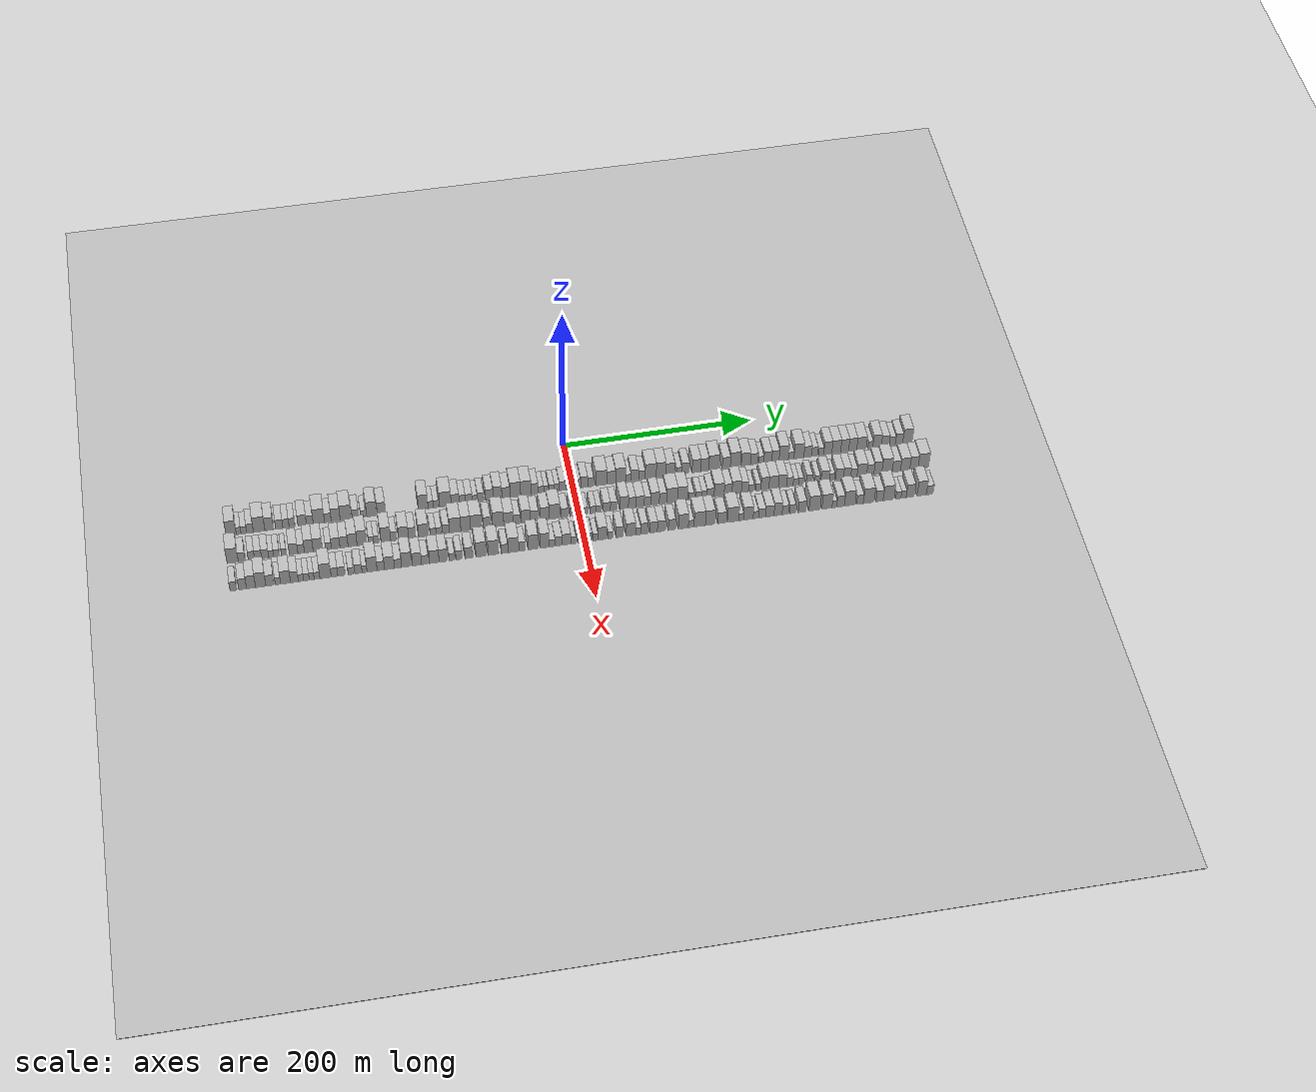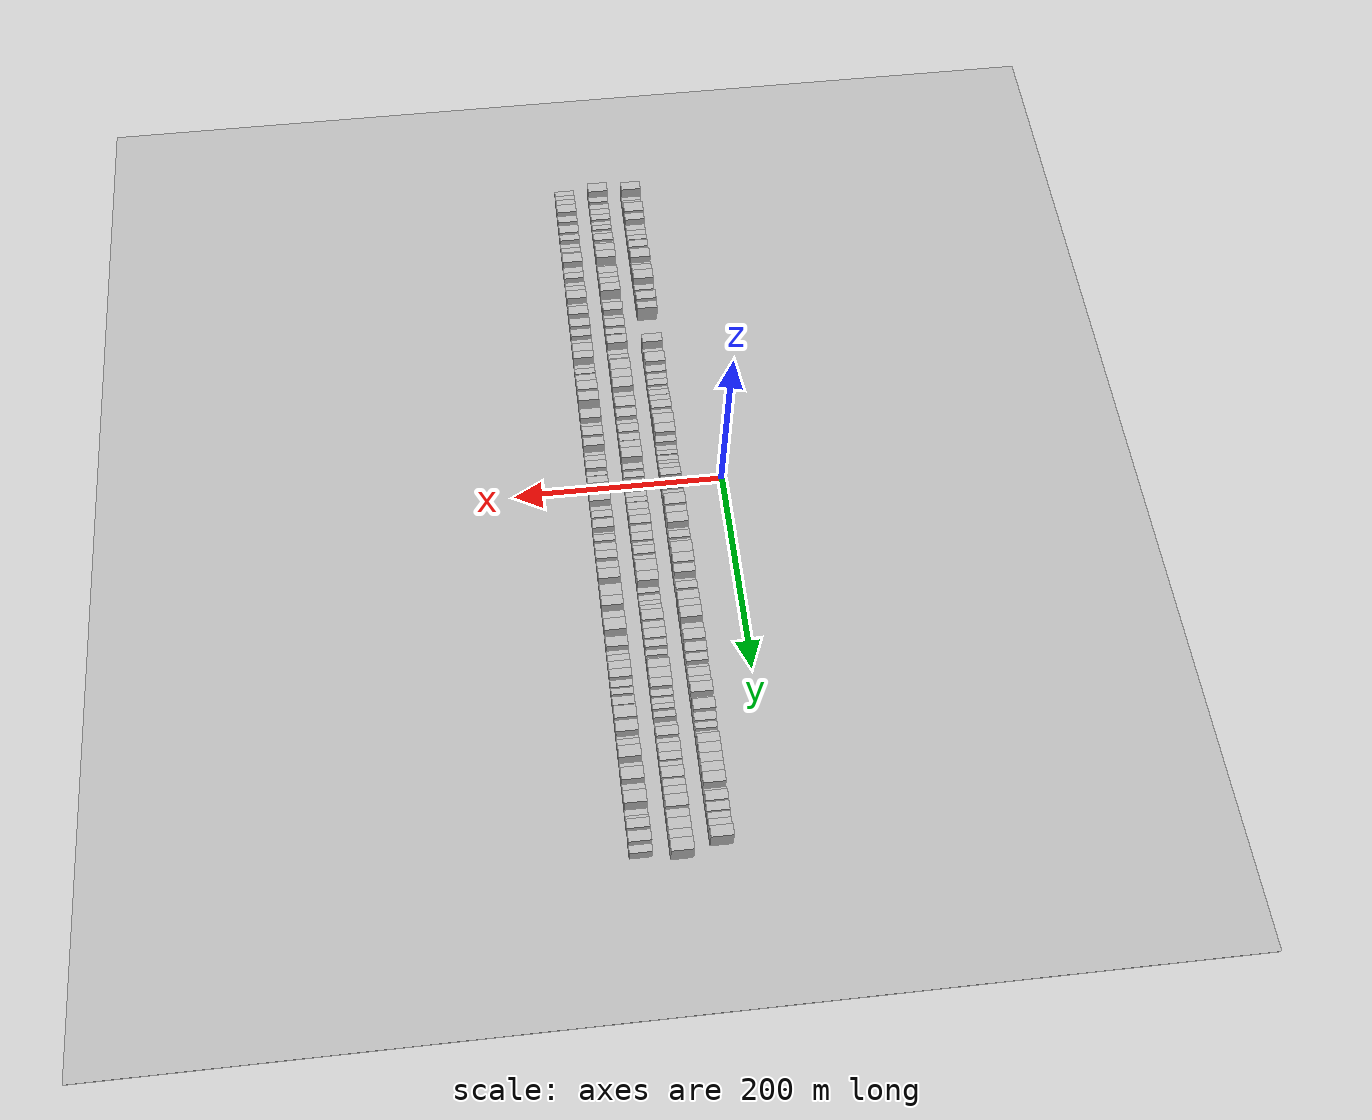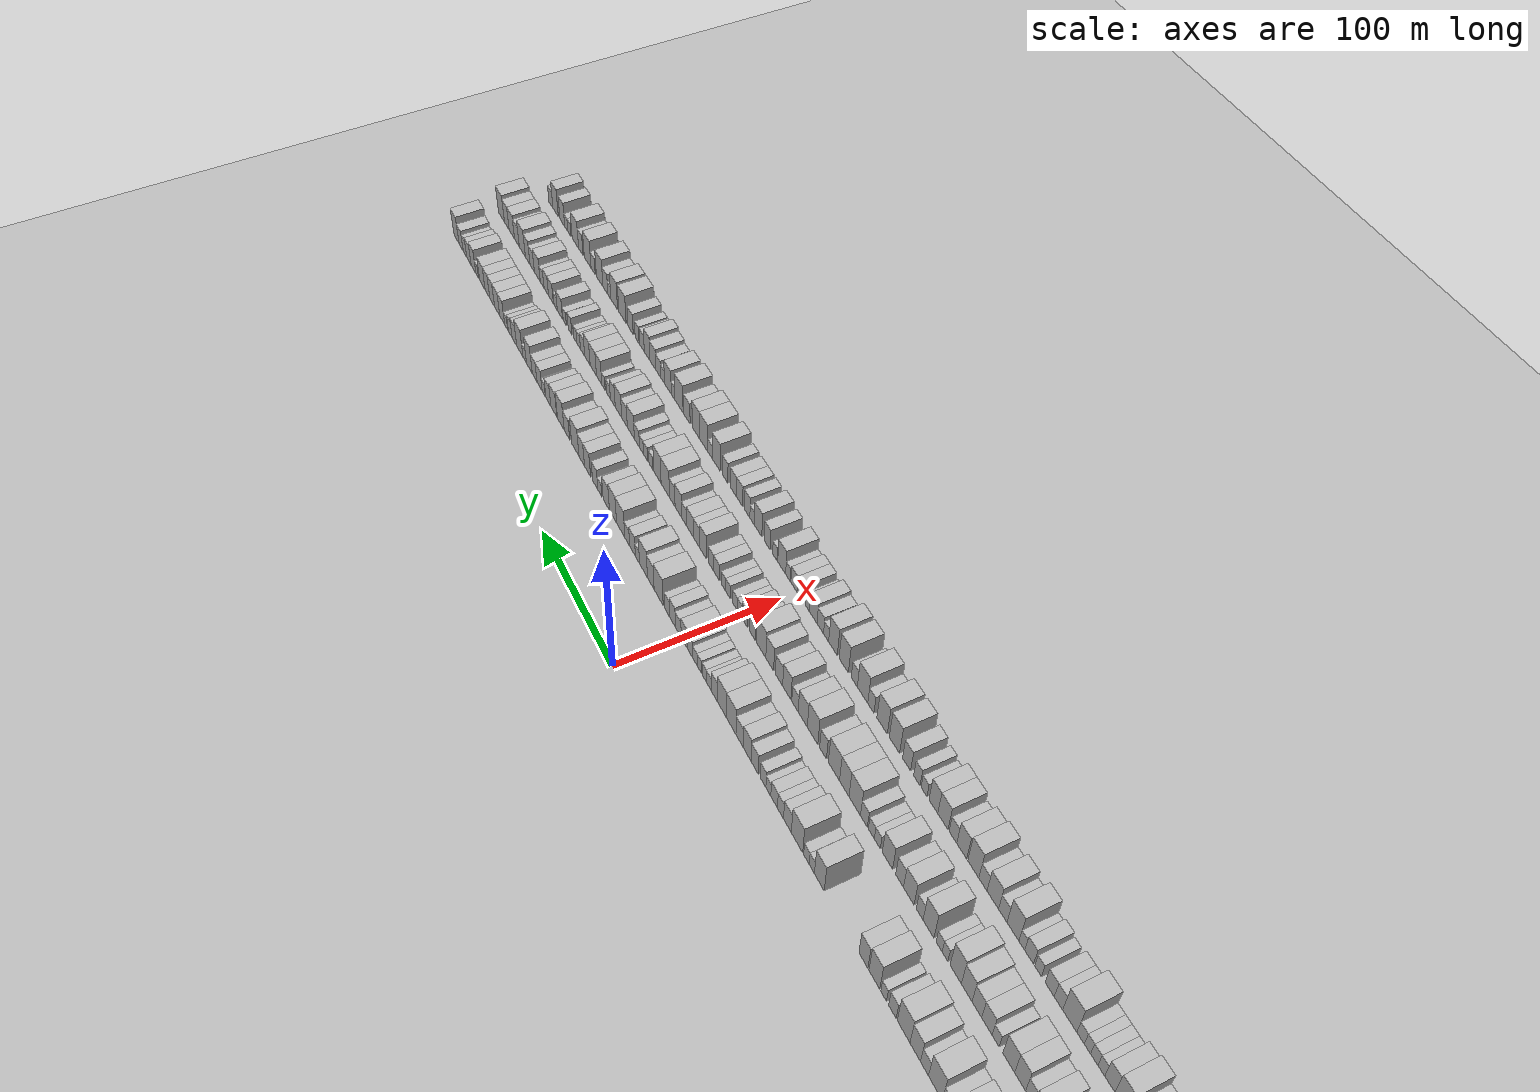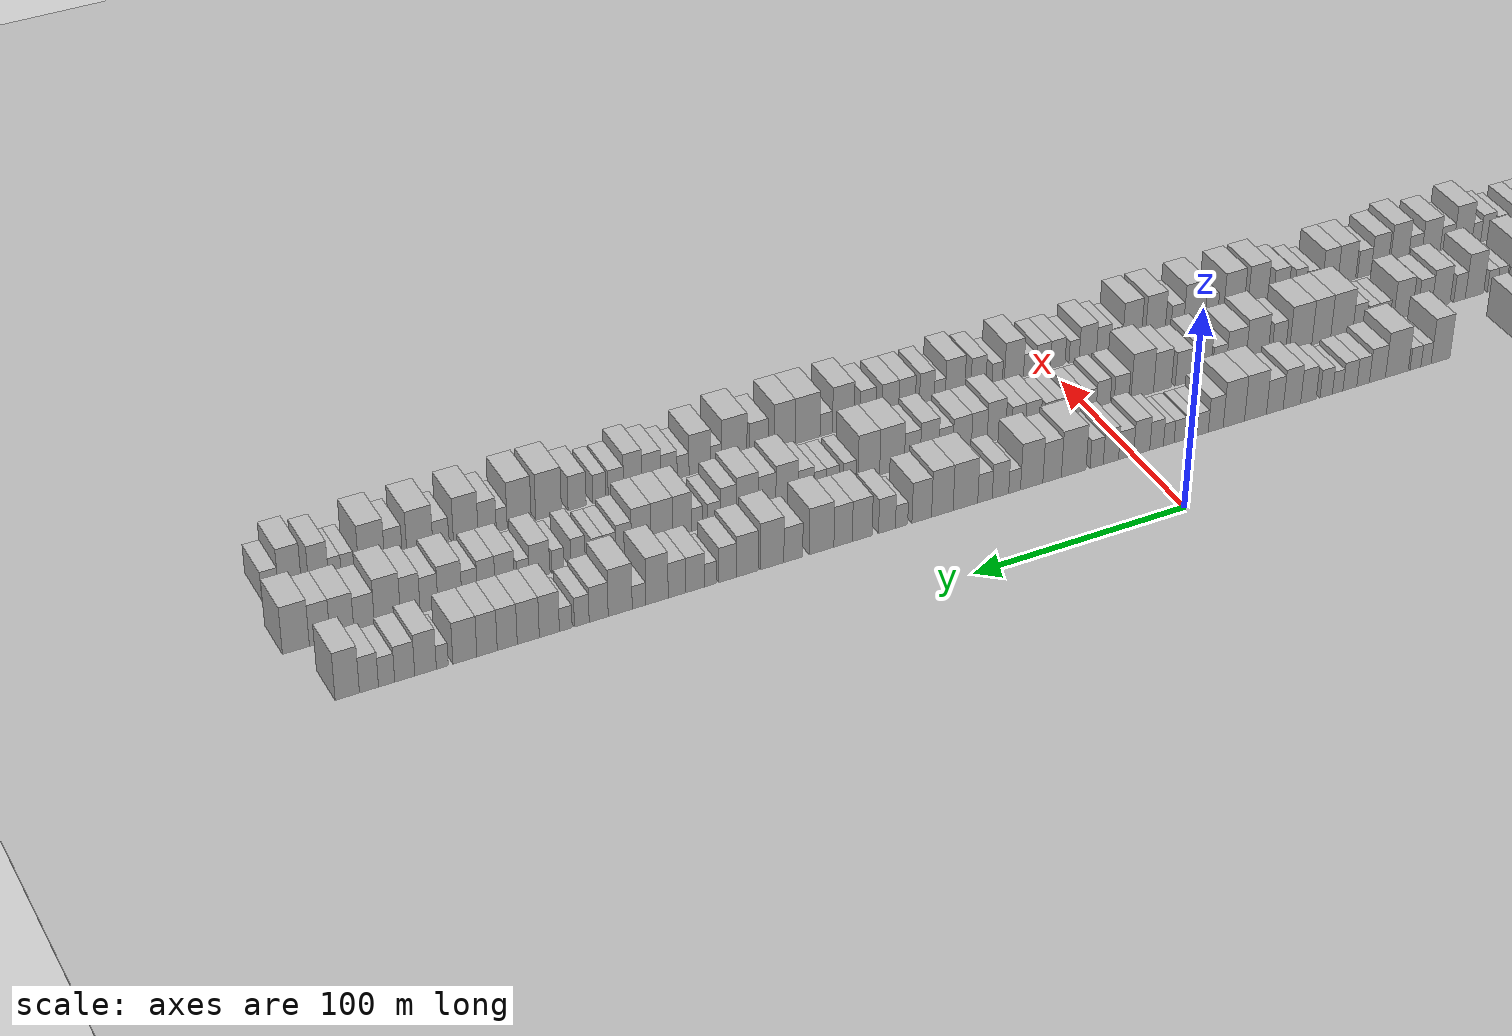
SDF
<?xml version="1.0" encoding="utf-8"?>

<sdf version="1.6">

   <world name="default">

      <gui fullscreen="0">

         <camera name="user_camera">

            <pose>-15 0 4.57585 0 0 0</pose>

            <view_controller>orbit</view_controller>

         </camera>

      </gui>

      <scene>

         <sky>

           <clouds>

             <speed>12</speed>

           </clouds>

         </sky>

         <ambient>0.4 0.4 0.4 1</ambient>

         <background>0.7 0.7 0.7 1</background>

         <shadows>1</shadows>

      </scene>

      <gravity>0 0 -9.8066</gravity>

      <magnetic_field>6e-06 2.3e-05 -4.2e-05</magnetic_field>

      <physics default="0" name="default_physics" type="ode">

         <ode>

            <solver>

               <type>quick</type>

               <iters>10</iters>

               <sor>1.0</sor>

               <use_dynamic_moi_rescaling>0</use_dynamic_moi_rescaling>

            </solver>

            <constraints>

               <cfm>0</cfm>

               <erp>0.2</erp>

               <contact_max_correcting_vel>100</contact_max_correcting_vel>

               <contact_surface_layer>0.001</contact_surface_layer>

            </constraints>

         </ode>

         <max_step_size>0.004</max_step_size>

         <real_time_factor>1</real_time_factor>

         <real_time_update_rate>250</real_time_update_rate>

      </physics>

      <light name="sun" type="directional">

         <cast_shadows>1</cast_shadows>

         <pose>0 0 10 0 0 0</pose>

         <diffuse>0.8 0.8 0.8 1</diffuse>

         <specular>0.2 0.2 0.2 1</specular>

         <attenuation>

            <range>1000</range>

            <constant>0.9</constant>

            <linear>0.01</linear>

            <quadratic>0.001</quadratic>

         </attenuation>

         <direction>-0.5 0.1 -0.9</direction>

      </light>

      <include>

         <name>ground_plane_1</name>

         <uri>model://HANNAS_ground_plane</uri>

         <pose>0 0 0  0 0 0</pose>

      </include>

      <include>

         <name>ground_plane_2</name>

         <uri>model://HANNAS_ground_plane</uri>

         <pose>100 0 0  0 0 0</pose>

      </include>

      <model name="building_1">

         <static>1</static>

         <pose frame="">50.0000 -352.8686 0 0.000000 0.000000 0.000000</pose>

         <link name="link">

            <pose frame="">0 0 12.00 0 0 0</pose>

            <collision name="collision">

               <geometry>

                  <box>

                     <size>20.0000 10.2628 24.0000</size>

                  </box>

               </geometry>

               <max_contacts>10</max_contacts>

               <surface>

                  <contact>

                     <ode/>

                  </contact>

                  <bounce/>

                  <friction>

                     <torsional>

                        <ode/>

                     </torsional>

                     <ode/>

                  </friction>

               </surface>

            </collision>

            <visual name="visual">

               <cast_shadows>0</cast_shadows>

               <geometry>

                  <box>

                     <size>20.0000 10.2628 24.0000</size>

                  </box>

               </geometry>

               <material>

                  <script>

                     <uri>model://HANNAS_wall/materials/scripts</uri>

                     <uri>model://HANNAS_wall/materials/textures</uri>

                     <name>vrc/HANNAS_wall</name>

                  </script>

               </material>

            </visual>

            <self_collide>0</self_collide>

            <enable_wind>0</enable_wind>

            <kinematic>0</kinematic>

         </link>

      </model>

      <model name="building_2">

         <static>1</static>

         <pose frame="">50.0000 -345.3248 0 0.000000 0.000000 0.000000</pose>

         <link name="link">

            <pose frame="">0 0 6.00 0 0 0</pose>

            <collision name="collision">

               <geometry>

                  <box>

                     <size>20.0000 4.8248 12.0000</size>

                  </box>

               </geometry>

               <max_contacts>10</max_contacts>

               <surface>

                  <contact>

                     <ode/>

                  </contact>

                  <bounce/>

                  <friction>

                     <torsional>

                        <ode/>

                     </torsional>

                     <ode/>

                  </friction>

               </surface>

            </collision>

            <visual name="visual">

               <cast_shadows>0</cast_shadows>

               <geometry>

                  <box>

                     <size>20.0000 4.8248 12.0000</size>

                  </box>

               </geometry>

               <material>

                  <script>

                     <uri>model://HANNAS_wall/materials/scripts</uri>

                     <uri>model://HANNAS_wall/materials/textures</uri>

                     <name>vrc/HANNAS_wall</name>

                  </script>

               </material>

            </visual>

            <self_collide>0</self_collide>

            <enable_wind>0</enable_wind>

            <kinematic>0</kinematic>

         </link>

      </model>

      <model name="building_3">

         <static>1</static>

         <pose frame="">50.0000 -339.9929 0 0.000000 0.000000 0.000000</pose>

         <link name="link">

            <pose frame="">0 0 6.00 0 0 0</pose>

            <collision name="collision">

               <geometry>

                  <box>

                     <size>20.0000 5.8389 12.0000</size>

                  </box>

               </geometry>

               <max_contacts>10</max_contacts>

               <surface>

                  <contact>

                     <ode/>

                  </contact>

                  <bounce/>

                  <friction>

                     <torsional>

                        <ode/>

                     </torsional>

                     <ode/>

                  </friction>

               </surface>

            </collision>

            <visual name="visual">

               <cast_shadows>0</cast_shadows>

               <geometry>

                  <box>

                     <size>20.0000 5.8389 12.0000</size>

                  </box>

               </geometry>

               <material>

                  <script>

                     <uri>model://HANNAS_wall/materials/scripts</uri>

                     <uri>model://HANNAS_wall/materials/textures</uri>

                     <name>vrc/HANNAS_wall</name>

                  </script>

               </material>

            </visual>

            <self_collide>0</self_collide>

            <enable_wind>0</enable_wind>

            <kinematic>0</kinematic>

         </link>

      </model>

      <model name="building_4">

         <static>1</static>

         <pose frame="">50.0000 -333.7014 0 0.000000 0.000000 0.000000</pose>

         <link name="link">

            <pose frame="">0 0 7.50 0 0 0</pose>

            <collision name="collision">

               <geometry>

                  <box>

                     <size>20.0000 6.7441 15.0000</size>

                  </box>

               </geometry>

               <max_contacts>10</max_contacts>

               <surface>

                  <contact>

                     <ode/>

                  </contact>

                  <bounce/>

                  <friction>

                     <torsional>

                        <ode/>

                     </torsional>

                     <ode/>

                  </friction>

               </surface>

            </collision>

            <visual name="visual">

               <cast_shadows>0</cast_shadows>

               <geometry>

                  <box>

                     <size>20.0000 6.7441 15.0000</size>

                  </box>

               </geometry>

               <material>

                  <script>

                     <uri>model://HANNAS_wall/materials/scripts</uri>

                     <uri>model://HANNAS_wall/materials/textures</uri>

                     <name>vrc/HANNAS_wall</name>

                  </script>

               </material>

            </visual>

            <self_collide>0</self_collide>

            <enable_wind>0</enable_wind>

            <kinematic>0</kinematic>

         </link>

      </model>

      <model name="building_5">

         <static>1</static>

         <pose frame="">50.0000 -324.4189 0 0.000000 0.000000 0.000000</pose>

         <link name="link">

            <pose frame="">0 0 12.00 0 0 0</pose>

            <collision name="collision">

               <geometry>

                  <box>

                     <size>20.0000 11.8209 24.0000</size>

                  </box>

               </geometry>

               <max_contacts>10</max_contacts>

               <surface>

                  <contact>

                     <ode/>

                  </contact>

                  <bounce/>

                  <friction>

                     <torsional>

                        <ode/>

                     </torsional>

                     <ode/>

                  </friction>

               </surface>

            </collision>

            <visual name="visual">

               <cast_shadows>0</cast_shadows>

               <geometry>

                  <box>

                     <size>20.0000 11.8209 24.0000</size>

                  </box>

               </geometry>

               <material>

                  <script>

                     <uri>model://HANNAS_wall/materials/scripts</uri>

                     <uri>model://HANNAS_wall/materials/textures</uri>

                     <name>vrc/HANNAS_wall</name>

                  </script>

               </material>

            </visual>

            <self_collide>0</self_collide>

            <enable_wind>0</enable_wind>

            <kinematic>0</kinematic>

         </link>

      </model>

      <model name="building_6">

         <static>1</static>

         <pose frame="">50.0000 -314.0192 0 0.000000 0.000000 0.000000</pose>

         <link name="link">

            <pose frame="">0 0 10.50 0 0 0</pose>

            <collision name="collision">

               <geometry>

                  <box>

                     <size>20.0000 8.9787 21.0000</size>

                  </box>

               </geometry>

               <max_contacts>10</max_contacts>

               <surface>

                  <contact>

                     <ode/>

                  </contact>

                  <bounce/>

                  <friction>

                     <torsional>

                        <ode/>

                     </torsional>

                     <ode/>

                  </friction>

               </surface>

            </collision>

            <visual name="visual">

               <cast_shadows>0</cast_shadows>

               <geometry>

                  <box>

                     <size>20.0000 8.9787 21.0000</size>

                  </box>

               </geometry>

               <material>

                  <script>

                     <uri>model://HANNAS_wall/materials/scripts</uri>

                     <uri>model://HANNAS_wall/materials/textures</uri>

                     <name>vrc/HANNAS_wall</name>

                  </script>

               </material>

            </visual>

            <self_collide>0</self_collide>

            <enable_wind>0</enable_wind>

            <kinematic>0</kinematic>

         </link>

      </model>

      <model name="building_7">

         <static>1</static>

         <pose frame="">50.0000 -303.8690 0 0.000000 0.000000 0.000000</pose>

         <link name="link">

            <pose frame="">0 0 7.50 0 0 0</pose>

            <collision name="collision">

               <geometry>

                  <box>

                     <size>20.0000 7.3216 15.0000</size>

                  </box>

               </geometry>

               <max_contacts>10</max_contacts>

               <surface>

                  <contact>

                     <ode/>

                  </contact>

                  <bounce/>

                  <friction>

                     <torsional>

                        <ode/>

                     </torsional>

                     <ode/>

                  </friction>

               </surface>

            </collision>

            <visual name="visual">

               <cast_shadows>0</cast_shadows>

               <geometry>

                  <box>

                     <size>20.0000 7.3216 15.0000</size>

                  </box>

               </geometry>

               <material>

                  <script>

                     <uri>model://HANNAS_wall/materials/scripts</uri>

                     <uri>model://HANNAS_wall/materials/textures</uri>

                     <name>vrc/HANNAS_wall</name>

                  </script>

               </material>

            </visual>

            <self_collide>0</self_collide>

            <enable_wind>0</enable_wind>

            <kinematic>0</kinematic>

         </link>

      </model>

      <model name="building_8">

         <static>1</static>

         <pose frame="">50.0000 -297.0208 0 0.000000 0.000000 0.000000</pose>

         <link name="link">

            <pose frame="">0 0 7.50 0 0 0</pose>

            <collision name="collision">

               <geometry>

                  <box>

                     <size>20.0000 6.3748 15.0000</size>

                  </box>

               </geometry>

               <max_contacts>10</max_contacts>

               <surface>

                  <contact>

                     <ode/>

                  </contact>

                  <bounce/>

                  <friction>

                     <torsional>

                        <ode/>

                     </torsional>

                     <ode/>

                  </friction>

               </surface>

            </collision>

            <visual name="visual">

               <cast_shadows>0</cast_shadows>

               <geometry>

                  <box>

                     <size>20.0000 6.3748 15.0000</size>

                  </box>

               </geometry>

               <material>

                  <script>

                     <uri>model://HANNAS_wall/materials/scripts</uri>

                     <uri>model://HANNAS_wall/materials/textures</uri>

                     <name>vrc/HANNAS_wall</name>

                  </script>

               </material>

            </visual>

            <self_collide>0</self_collide>

            <enable_wind>0</enable_wind>

            <kinematic>0</kinematic>

         </link>

      </model>

      <model name="building_9">

         <static>1</static>

         <pose frame="">50.0000 -290.8084 0 0.000000 0.000000 0.000000</pose>

         <link name="link">

            <pose frame="">0 0 7.50 0 0 0</pose>

            <collision name="collision">

               <geometry>

                  <box>

                     <size>20.0000 6.0501 15.0000</size>

                  </box>

               </geometry>

               <max_contacts>10</max_contacts>

               <surface>

                  <contact>

                     <ode/>

                  </contact>

                  <bounce/>

                  <friction>

                     <torsional>

                        <ode/>

                     </torsional>

                     <ode/>

                  </friction>

               </surface>

            </collision>

            <visual name="visual">

               <cast_shadows>0</cast_shadows>

               <geometry>

                  <box>

                     <size>20.0000 6.0501 15.0000</size>

                  </box>

               </geometry>

               <material>

                  <script>

                     <uri>model://HANNAS_wall/materials/scripts</uri>

                     <uri>model://HANNAS_wall/materials/textures</uri>

                     <name>vrc/HANNAS_wall</name>

                  </script>

               </material>

            </visual>

            <self_collide>0</self_collide>

            <enable_wind>0</enable_wind>

            <kinematic>0</kinematic>

         </link>

      </model>

      <model name="building_10">

         <static>1</static>

         <pose frame="">50.0000 -280.3796 0 0.000000 0.000000 0.000000</pose>

         <link name="link">

            <pose frame="">0 0 9.00 0 0 0</pose>

            <collision name="collision">

               <geometry>

                  <box>

                     <size>20.0000 8.8075 18.0000</size>

                  </box>

               </geometry>

               <max_contacts>10</max_contacts>

               <surface>

                  <contact>

                     <ode/>

                  </contact>

                  <bounce/>

                  <friction>

                     <torsional>

                        <ode/>

                     </torsional>

                     <ode/>

                  </friction>

               </surface>

            </collision>

            <visual name="visual">

               <cast_shadows>0</cast_shadows>

               <geometry>

                  <box>

                     <size>20.0000 8.8075 18.0000</size>

                  </box>

               </geometry>

               <material>

                  <script>

                     <uri>model://HANNAS_wall/materials/scripts</uri>

                     <uri>model://HANNAS_wall/materials/textures</uri>

                     <name>vrc/HANNAS_wall</name>

                  </script>

               </material>

            </visual>

            <self_collide>0</self_collide>

            <enable_wind>0</enable_wind>

            <kinematic>0</kinematic>

         </link>

      </model>

      <model name="building_11">

         <static>1</static>

         <pose frame="">50.0000 -272.6070 0 0.000000 0.000000 0.000000</pose>

         <link name="link">

            <pose frame="">0 0 7.50 0 0 0</pose>

            <collision name="collision">

               <geometry>

                  <box>

                     <size>20.0000 6.7378 15.0000</size>

                  </box>

               </geometry>

               <max_contacts>10</max_contacts>

               <surface>

                  <contact>

                     <ode/>

                  </contact>

                  <bounce/>

                  <friction>

                     <torsional>

                        <ode/>

                     </torsional>

                     <ode/>

                  </friction>

               </surface>

            </collision>

            <visual name="visual">

               <cast_shadows>0</cast_shadows>

               <geometry>

                  <box>

                     <size>20.0000 6.7378 15.0000</size>

                  </box>

               </geometry>

               <material>

                  <script>

                     <uri>model://HANNAS_wall/materials/scripts</uri>

                     <uri>model://HANNAS_wall/materials/textures</uri>

                     <name>vrc/HANNAS_wall</name>

                  </script>

               </material>

            </visual>

            <self_collide>0</self_collide>

            <enable_wind>0</enable_wind>

            <kinematic>0</kinematic>

         </link>

      </model>

      <model name="building_12">

         <static>1</static>

         <pose frame="">50.0000 -263.4218 0 0.000000 0.000000 0.000000</pose>

         <link name="link">

            <pose frame="">0 0 12.00 0 0 0</pose>

            <collision name="collision">

               <geometry>

                  <box>

                     <size>20.0000 11.6326 24.0000</size>

                  </box>

               </geometry>

               <max_contacts>10</max_contacts>

               <surface>

                  <contact>

                     <ode/>

                  </contact>

                  <bounce/>

                  <friction>

                     <torsional>

                        <ode/>

                     </torsional>

                     <ode/>

                  </friction>

               </surface>

            </collision>

            <visual name="visual">

               <cast_shadows>0</cast_shadows>

               <geometry>

                  <box>

                     <size>20.0000 11.6326 24.0000</size>

                  </box>

               </geometry>

               <material>

                  <script>

                     <uri>model://HANNAS_wall/materials/scripts</uri>

                     <uri>model://HANNAS_wall/materials/textures</uri>

                     <name>vrc/HANNAS_wall</name>

                  </script>

               </material>

            </visual>

            <self_collide>0</self_collide>

            <enable_wind>0</enable_wind>

            <kinematic>0</kinematic>

         </link>

      </model>

      <model name="building_13">

         <static>1</static>

         <pose frame="">50.0000 -254.1615 0 0.000000 0.000000 0.000000</pose>

         <link name="link">

            <pose frame="">0 0 7.50 0 0 0</pose>

            <collision name="collision">

               <geometry>

                  <box>

                     <size>20.0000 6.8879 15.0000</size>

                  </box>

               </geometry>

               <max_contacts>10</max_contacts>

               <surface>

                  <contact>

                     <ode/>

                  </contact>

                  <bounce/>

                  <friction>

                     <torsional>

                        <ode/>

                     </torsional>

                     <ode/>

                  </friction>

               </surface>

            </collision>

            <visual name="visual">

               <cast_shadows>0</cast_shadows>

               <geometry>

                  <box>

                     <size>20.0000 6.8879 15.0000</size>

                  </box>

               </geometry>

               <material>

                  <script>

                     <uri>model://HANNAS_wall/materials/scripts</uri>

                     <uri>model://HANNAS_wall/materials/textures</uri>

                     <name>vrc/HANNAS_wall</name>

                  </script>

               </material>

            </visual>

            <self_collide>0</self_collide>

            <enable_wind>0</enable_wind>

            <kinematic>0</kinematic>

         </link>

      </model>

      <model name="building_14">

         <static>1</static>

         <pose frame="">50.0000 -246.1283 0 0.000000 0.000000 0.000000</pose>

         <link name="link">

            <pose frame="">0 0 10.50 0 0 0</pose>

            <collision name="collision">

               <geometry>

                  <box>

                     <size>20.0000 9.1787 21.0000</size>

                  </box>

               </geometry>

               <max_contacts>10</max_contacts>

               <surface>

                  <contact>

                     <ode/>

                  </contact>

                  <bounce/>

                  <friction>

                     <torsional>

                        <ode/>

                     </torsional>

                     <ode/>

                  </friction>

               </surface>

            </collision>

            <visual name="visual">

               <cast_shadows>0</cast_shadows>

               <geometry>

                  <box>

                     <size>20.0000 9.1787 21.0000</size>

                  </box>

               </geometry>

               <material>

                  <script>

                     <uri>model://HANNAS_wall/materials/scripts</uri>

                     <uri>model://HANNAS_wall/materials/textures</uri>

                     <name>vrc/HANNAS_wall</name>

                  </script>

               </material>

            </visual>

            <self_collide>0</self_collide>

            <enable_wind>0</enable_wind>

            <kinematic>0</kinematic>

         </link>

      </model>

      <model name="building_15">

         <static>1</static>

         <pose frame="">50.0000 -235.8832 0 0.000000 0.000000 0.000000</pose>

         <link name="link">

            <pose frame="">0 0 12.00 0 0 0</pose>

            <collision name="collision">

               <geometry>

                  <box>

                     <size>20.0000 11.3115 24.0000</size>

                  </box>

               </geometry>

               <max_contacts>10</max_contacts>

               <surface>

                  <contact>

                     <ode/>

                  </contact>

                  <bounce/>

                  <friction>

                     <torsional>

                        <ode/>

                     </torsional>

                     <ode/>

                  </friction>

               </surface>

            </collision>

            <visual name="visual">

               <cast_shadows>0</cast_shadows>

               <geometry>

                  <box>

                     <size>20.0000 11.3115 24.0000</size>

                  </box>

               </geometry>

               <material>

                  <script>

                     <uri>model://HANNAS_wall/materials/scripts</uri>

                     <uri>model://HANNAS_wall/materials/textures</uri>

                     <name>vrc/HANNAS_wall</name>

                  </script>

               </material>

            </visual>

            <self_collide>0</self_collide>

            <enable_wind>0</enable_wind>

            <kinematic>0</kinematic>

         </link>

      </model>

      <model name="building_16">

         <static>1</static>

         <pose frame="">50.0000 -225.7912 0 0.000000 0.000000 0.000000</pose>

         <link name="link">

            <pose frame="">0 0 7.50 0 0 0</pose>

            <collision name="collision">

               <geometry>

                  <box>

                     <size>20.0000 6.8725 15.0000</size>

                  </box>

               </geometry>

               <max_contacts>10</max_contacts>

               <surface>

                  <contact>

                     <ode/>

                  </contact>

                  <bounce/>

                  <friction>

                     <torsional>

                        <ode/>

                     </torsional>

                     <ode/>

                  </friction>

               </surface>

            </collision>

            <visual name="visual">

               <cast_shadows>0</cast_shadows>

               <geometry>

                  <box>

                     <size>20.0000 6.8725 15.0000</size>

                  </box>

               </geometry>

               <material>

                  <script>

                     <uri>model://HANNAS_wall/materials/scripts</uri>

                     <uri>model://HANNAS_wall/materials/textures</uri>

                     <name>vrc/HANNAS_wall</name>

                  </script>

               </material>

            </visual>

            <self_collide>0</self_collide>

            <enable_wind>0</enable_wind>

            <kinematic>0</kinematic>

         </link>

      </model>

      <model name="building_17">

         <static>1</static>

         <pose frame="">50.0000 -217.7976 0 0.000000 0.000000 0.000000</pose>

         <link name="link">

            <pose frame="">0 0 6.00 0 0 0</pose>

            <collision name="collision">

               <geometry>

                  <box>

                     <size>20.0000 5.1148 12.0000</size>

                  </box>

               </geometry>

               <max_contacts>10</max_contacts>

               <surface>

                  <contact>

                     <ode/>

                  </contact>

                  <bounce/>

                  <friction>

                     <torsional>

                        <ode/>

                     </torsional>

                     <ode/>

                  </friction>

               </surface>

            </collision>

            <visual name="visual">

               <cast_shadows>0</cast_shadows>

               <geometry>

                  <box>

                     <size>20.0000 5.1148 12.0000</size>

                  </box>

               </geometry>

               <material>

                  <script>

                     <uri>model://HANNAS_wall/materials/scripts</uri>

                     <uri>model://HANNAS_wall/materials/textures</uri>

                     <name>vrc/HANNAS_wall</name>

                  </script>

               </material>

            </visual>

            <self_collide>0</self_collide>

            <enable_wind>0</enable_wind>

            <kinematic>0</kinematic>

         </link>

      </model>

      <model name="building_18">

         <static>1</static>

         <pose frame="">50.0000 -209.2322 0 0.000000 0.000000 0.000000</pose>

         <link name="link">

            <pose frame="">0 0 12.00 0 0 0</pose>

            <collision name="collision">

               <geometry>

                  <box>

                     <size>20.0000 10.0159 24.0000</size>

                  </box>

               </geometry>

               <max_contacts>10</max_contacts>

               <surface>

                  <contact>

                     <ode/>

                  </contact>

                  <bounce/>

                  <friction>

                     <torsional>

                        <ode/>

                     </torsional>

                     <ode/>

                  </friction>

               </surface>

            </collision>

            <visual name="visual">

               <cast_shadows>0</cast_shadows>

               <geometry>

                  <box>

                     <size>20.0000 10.0159 24.0000</size>

                  </box>

               </geometry>

               <material>

                  <script>

                     <uri>model://HANNAS_wall/materials/scripts</uri>

                     <uri>model://HANNAS_wall/materials/textures</uri>

                     <name>vrc/HANNAS_wall</name>

                  </script>

               </material>

            </visual>

            <self_collide>0</self_collide>

            <enable_wind>0</enable_wind>

            <kinematic>0</kinematic>

         </link>

      </model>

      <model name="building_19">

         <static>1</static>

         <pose frame="">50.0000 -199.0044 0 0.000000 0.000000 0.000000</pose>

         <link name="link">

            <pose frame="">0 0 10.50 0 0 0</pose>

            <collision name="collision">

               <geometry>

                  <box>

                     <size>20.0000 8.4398 21.0000</size>

                  </box>

               </geometry>

               <max_contacts>10</max_contacts>

               <surface>

                  <contact>

                     <ode/>

                  </contact>

                  <bounce/>

                  <friction>

                     <torsional>

                        <ode/>

                     </torsional>

                     <ode/>

                  </friction>

               </surface>

            </collision>

            <visual name="visual">

               <cast_shadows>0</cast_shadows>

               <geometry>

                  <box>

                     <size>20.0000 8.4398 21.0000</size>

                  </box>

               </geometry>

               <material>

                  <script>

                     <uri>model://HANNAS_wall/materials/scripts</uri>

                     <uri>model://HANNAS_wall/materials/textures</uri>

                     <name>vrc/HANNAS_wall</name>

                  </script>

               </material>

            </visual>

            <self_collide>0</self_collide>

            <enable_wind>0</enable_wind>

            <kinematic>0</kinematic>

         </link>

      </model>

      <model name="building_20">

         <static>1</static>

         <pose frame="">50.0000 -155.9220 0 0.000000 0.000000 0.000000</pose>

         <link name="link">

            <pose frame="">0 0 12.00 0 0 0</pose>

            <collision name="collision">

               <geometry>

                  <box>

                     <size>20.0000 9.9083 24.0000</size>

                  </box>

               </geometry>

               <max_contacts>10</max_contacts>

               <surface>

                  <contact>

                     <ode/>

                  </contact>

                  <bounce/>

                  <friction>

                     <torsional>

                        <ode/>

                     </torsional>

                     <ode/>

                  </friction>

               </surface>

            </collision>

            <visual name="visual">

               <cast_shadows>0</cast_shadows>

               <geometry>

                  <box>

                     <size>20.0000 9.9083 24.0000</size>

                  </box>

               </geometry>

               <material>

                  <script>

                     <uri>model://HANNAS_wall/materials/scripts</uri>

                     <uri>model://HANNAS_wall/materials/textures</uri>

                     <name>vrc/HANNAS_wall</name>

                  </script>

               </material>

            </visual>

            <self_collide>0</self_collide>

            <enable_wind>0</enable_wind>

            <kinematic>0</kinematic>

         </link>

      </model>

      <model name="building_21">

         <static>1</static>

         <pose frame="">50.0000 -148.2949 0 0.000000 0.000000 0.000000</pose>

         <link name="link">

            <pose frame="">0 0 6.00 0 0 0</pose>

            <collision name="collision">

               <geometry>

                  <box>

                     <size>20.0000 5.3460 12.0000</size>

                  </box>

               </geometry>

               <max_contacts>10</max_contacts>

               <surface>

                  <contact>

                     <ode/>

                  </contact>

                  <bounce/>

                  <friction>

                     <torsional>

                        <ode/>

                     </torsional>

                     <ode/>

                  </friction>

               </surface>

            </collision>

            <visual name="visual">

               <cast_shadows>0</cast_shadows>

               <geometry>

                  <box>

                     <size>20.0000 5.3460 12.0000</size>

                  </box>

               </geometry>

               <material>

                  <script>

                     <uri>model://HANNAS_wall/materials/scripts</uri>

                     <uri>model://HANNAS_wall/materials/textures</uri>

                     <name>vrc/HANNAS_wall</name>

                  </script>

               </material>

            </visual>

            <self_collide>0</self_collide>

            <enable_wind>0</enable_wind>

            <kinematic>0</kinematic>

         </link>

      </model>

      <model name="building_22">

         <static>1</static>

         <pose frame="">50.0000 -142.7699 0 0.000000 0.000000 0.000000</pose>

         <link name="link">

            <pose frame="">0 0 6.00 0 0 0</pose>

            <collision name="collision">

               <geometry>

                  <box>

                     <size>20.0000 5.7038 12.0000</size>

                  </box>

               </geometry>

               <max_contacts>10</max_contacts>

               <surface>

                  <contact>

                     <ode/>

                  </contact>

                  <bounce/>

                  <friction>

                     <torsional>

                        <ode/>

                     </torsional>

                     <ode/>

                  </friction>

               </surface>

            </collision>

            <visual name="visual">

               <cast_shadows>0</cast_shadows>

               <geometry>

                  <box>

                     <size>20.0000 5.7038 12.0000</size>

                  </box>

               </geometry>

               <material>

                  <script>

                     <uri>model://HANNAS_wall/materials/scripts</uri>

                     <uri>model://HANNAS_wall/materials/textures</uri>

                     <name>vrc/HANNAS_wall</name>

                  </script>

               </material>

            </visual>

            <self_collide>0</self_collide>

            <enable_wind>0</enable_wind>

            <kinematic>0</kinematic>

         </link>

      </model>

      <model name="building_23">

         <static>1</static>

         <pose frame="">50.0000 -132.9776 0 0.000000 0.000000 0.000000</pose>

         <link name="link">

            <pose frame="">0 0 12.00 0 0 0</pose>

            <collision name="collision">

               <geometry>

                  <box>

                     <size>20.0000 11.8810 24.0000</size>

                  </box>

               </geometry>

               <max_contacts>10</max_contacts>

               <surface>

                  <contact>

                     <ode/>

                  </contact>

                  <bounce/>

                  <friction>

                     <torsional>

                        <ode/>

                     </torsional>

                     <ode/>

                  </friction>

               </surface>

            </collision>

            <visual name="visual">

               <cast_shadows>0</cast_shadows>

               <geometry>

                  <box>

                     <size>20.0000 11.8810 24.0000</size>

                  </box>

               </geometry>

               <material>

                  <script>

                     <uri>model://HANNAS_wall/materials/scripts</uri>

                     <uri>model://HANNAS_wall/materials/textures</uri>

                     <name>vrc/HANNAS_wall</name>

                  </script>

               </material>

            </visual>

            <self_collide>0</self_collide>

            <enable_wind>0</enable_wind>

            <kinematic>0</kinematic>

         </link>

      </model>

      <model name="building_24">

         <static>1</static>

         <pose frame="">50.0000 -122.8641 0 0.000000 0.000000 0.000000</pose>

         <link name="link">

            <pose frame="">0 0 9.00 0 0 0</pose>

            <collision name="collision">

               <geometry>

                  <box>

                     <size>20.0000 8.3459 18.0000</size>

                  </box>

               </geometry>

               <max_contacts>10</max_contacts>

               <surface>

                  <contact>

                     <ode/>

                  </contact>

                  <bounce/>

                  <friction>

                     <torsional>

                        <ode/>

                     </torsional>

                     <ode/>

                  </friction>

               </surface>

            </collision>

            <visual name="visual">

               <cast_shadows>0</cast_shadows>

               <geometry>

                  <box>

                     <size>20.0000 8.3459 18.0000</size>

                  </box>

               </geometry>

               <material>

                  <script>

                     <uri>model://HANNAS_wall/materials/scripts</uri>

                     <uri>model://HANNAS_wall/materials/textures</uri>

                     <name>vrc/HANNAS_wall</name>

                  </script>

               </material>

            </visual>

            <self_collide>0</self_collide>

            <enable_wind>0</enable_wind>

            <kinematic>0</kinematic>

         </link>

      </model>

      <model name="building_25">

         <static>1</static>

         <pose frame="">50.0000 -115.4376 0 0.000000 0.000000 0.000000</pose>

         <link name="link">

            <pose frame="">0 0 7.50 0 0 0</pose>

            <collision name="collision">

               <geometry>

                  <box>

                     <size>20.0000 6.5071 15.0000</size>

                  </box>

               </geometry>

               <max_contacts>10</max_contacts>

               <surface>

                  <contact>

                     <ode/>

                  </contact>

                  <bounce/>

                  <friction>

                     <torsional>

                        <ode/>

                     </torsional>

                     <ode/>

                  </friction>

               </surface>

            </collision>

            <visual name="visual">

               <cast_shadows>0</cast_shadows>

               <geometry>

                  <box>

                     <size>20.0000 6.5071 15.0000</size>

                  </box>

               </geometry>

               <material>

                  <script>

                     <uri>model://HANNAS_wall/materials/scripts</uri>

                     <uri>model://HANNAS_wall/materials/textures</uri>

                     <name>vrc/HANNAS_wall</name>

                  </script>

               </material>

            </visual>

            <self_collide>0</self_collide>

            <enable_wind>0</enable_wind>

            <kinematic>0</kinematic>

         </link>

      </model>

      <model name="building_26">

         <static>1</static>

         <pose frame="">50.0000 -108.5881 0 0.000000 0.000000 0.000000</pose>

         <link name="link">

            <pose frame="">0 0 7.50 0 0 0</pose>

            <collision name="collision">

               <geometry>

                  <box>

                     <size>20.0000 7.1920 15.0000</size>

                  </box>

               </geometry>

               <max_contacts>10</max_contacts>

               <surface>

                  <contact>

                     <ode/>

                  </contact>

                  <bounce/>

                  <friction>

                     <torsional>

                        <ode/>

                     </torsional>

                     <ode/>

                  </friction>

               </surface>

            </collision>

            <visual name="visual">

               <cast_shadows>0</cast_shadows>

               <geometry>

                  <box>

                     <size>20.0000 7.1920 15.0000</size>

                  </box>

               </geometry>

               <material>

                  <script>

                     <uri>model://HANNAS_wall/materials/scripts</uri>

                     <uri>model://HANNAS_wall/materials/textures</uri>

                     <name>vrc/HANNAS_wall</name>

                  </script>

               </material>

            </visual>

            <self_collide>0</self_collide>

            <enable_wind>0</enable_wind>

            <kinematic>0</kinematic>

         </link>

      </model>

      <model name="building_27">

         <static>1</static>

         <pose frame="">50.0000 -102.2890 0 0.000000 0.000000 0.000000</pose>

         <link name="link">

            <pose frame="">0 0 6.00 0 0 0</pose>

            <collision name="collision">

               <geometry>

                  <box>

                     <size>20.0000 5.4062 12.0000</size>

                  </box>

               </geometry>

               <max_contacts>10</max_contacts>

               <surface>

                  <contact>

                     <ode/>

                  </contact>

                  <bounce/>

                  <friction>

                     <torsional>

                        <ode/>

                     </torsional>

                     <ode/>

                  </friction>

               </surface>

            </collision>

            <visual name="visual">

               <cast_shadows>0</cast_shadows>

               <geometry>

                  <box>

                     <size>20.0000 5.4062 12.0000</size>

                  </box>

               </geometry>

               <material>

                  <script>

                     <uri>model://HANNAS_wall/materials/scripts</uri>

                     <uri>model://HANNAS_wall/materials/textures</uri>

                     <name>vrc/HANNAS_wall</name>

                  </script>

               </material>

            </visual>

            <self_collide>0</self_collide>

            <enable_wind>0</enable_wind>

            <kinematic>0</kinematic>

         </link>

      </model>

      <model name="building_28">

         <static>1</static>

         <pose frame="">50.0000 -96.3945 0 0.000000 0.000000 0.000000</pose>

         <link name="link">

            <pose frame="">0 0 7.50 0 0 0</pose>

            <collision name="collision">

               <geometry>

                  <box>

                     <size>20.0000 6.3829 15.0000</size>

                  </box>

               </geometry>

               <max_contacts>10</max_contacts>

               <surface>

                  <contact>

                     <ode/>

                  </contact>

                  <bounce/>

                  <friction>

                     <torsional>

                        <ode/>

                     </torsional>

                     <ode/>

                  </friction>

               </surface>

            </collision>

            <visual name="visual">

               <cast_shadows>0</cast_shadows>

               <geometry>

                  <box>

                     <size>20.0000 6.3829 15.0000</size>

                  </box>

               </geometry>

               <material>

                  <script>

                     <uri>model://HANNAS_wall/materials/scripts</uri>

                     <uri>model://HANNAS_wall/materials/textures</uri>

                     <name>vrc/HANNAS_wall</name>

                  </script>

               </material>

            </visual>

            <self_collide>0</self_collide>

            <enable_wind>0</enable_wind>

            <kinematic>0</kinematic>

         </link>

      </model>

      <model name="building_29">

         <static>1</static>

         <pose frame="">50.0000 -87.2331 0 0.000000 0.000000 0.000000</pose>

         <link name="link">

            <pose frame="">0 0 9.00 0 0 0</pose>

            <collision name="collision">

               <geometry>

                  <box>

                     <size>20.0000 7.9398 18.0000</size>

                  </box>

               </geometry>

               <max_contacts>10</max_contacts>

               <surface>

                  <contact>

                     <ode/>

                  </contact>

                  <bounce/>

                  <friction>

                     <torsional>

                        <ode/>

                     </torsional>

                     <ode/>

                  </friction>

               </surface>

            </collision>

            <visual name="visual">

               <cast_shadows>0</cast_shadows>

               <geometry>

                  <box>

                     <size>20.0000 7.9398 18.0000</size>

                  </box>

               </geometry>

               <material>

                  <script>

                     <uri>model://HANNAS_wall/materials/scripts</uri>

                     <uri>model://HANNAS_wall/materials/textures</uri>

                     <name>vrc/HANNAS_wall</name>

                  </script>

               </material>

            </visual>

            <self_collide>0</self_collide>

            <enable_wind>0</enable_wind>

            <kinematic>0</kinematic>

         </link>

      </model>

      <model name="building_30">

         <static>1</static>

         <pose frame="">50.0000 -78.8094 0 0.000000 0.000000 0.000000</pose>

         <link name="link">

            <pose frame="">0 0 10.50 0 0 0</pose>

            <collision name="collision">

               <geometry>

                  <box>

                     <size>20.0000 8.9076 21.0000</size>

                  </box>

               </geometry>

               <max_contacts>10</max_contacts>

               <surface>

                  <contact>

                     <ode/>

                  </contact>

                  <bounce/>

                  <friction>

                     <torsional>

                        <ode/>

                     </torsional>

                     <ode/>

                  </friction>

               </surface>

            </collision>

            <visual name="visual">

               <cast_shadows>0</cast_shadows>

               <geometry>

                  <box>

                     <size>20.0000 8.9076 21.0000</size>

                  </box>

               </geometry>

               <material>

                  <script>

                     <uri>model://HANNAS_wall/materials/scripts</uri>

                     <uri>model://HANNAS_wall/materials/textures</uri>

                     <name>vrc/HANNAS_wall</name>

                  </script>

               </material>

            </visual>

            <self_collide>0</self_collide>

            <enable_wind>0</enable_wind>

            <kinematic>0</kinematic>

         </link>

      </model>

      <model name="building_31">

         <static>1</static>

         <pose frame="">50.0000 -70.1065 0 0.000000 0.000000 0.000000</pose>

         <link name="link">

            <pose frame="">0 0 9.00 0 0 0</pose>

            <collision name="collision">

               <geometry>

                  <box>

                     <size>20.0000 8.4981 18.0000</size>

                  </box>

               </geometry>

               <max_contacts>10</max_contacts>

               <surface>

                  <contact>

                     <ode/>

                  </contact>

                  <bounce/>

                  <friction>

                     <torsional>

                        <ode/>

                     </torsional>

                     <ode/>

                  </friction>

               </surface>

            </collision>

            <visual name="visual">

               <cast_shadows>0</cast_shadows>

               <geometry>

                  <box>

                     <size>20.0000 8.4981 18.0000</size>

                  </box>

               </geometry>

               <material>

                  <script>

                     <uri>model://HANNAS_wall/materials/scripts</uri>

                     <uri>model://HANNAS_wall/materials/textures</uri>

                     <name>vrc/HANNAS_wall</name>

                  </script>

               </material>

            </visual>

            <self_collide>0</self_collide>

            <enable_wind>0</enable_wind>

            <kinematic>0</kinematic>

         </link>

      </model>

      <model name="building_32">

         <static>1</static>

         <pose frame="">50.0000 -60.3243 0 0.000000 0.000000 0.000000</pose>

         <link name="link">

            <pose frame="">0 0 12.00 0 0 0</pose>

            <collision name="collision">

               <geometry>

                  <box>

                     <size>20.0000 11.0664 24.0000</size>

                  </box>

               </geometry>

               <max_contacts>10</max_contacts>

               <surface>

                  <contact>

                     <ode/>

                  </contact>

                  <bounce/>

                  <friction>

                     <torsional>

                        <ode/>

                     </torsional>

                     <ode/>

                  </friction>

               </surface>

            </collision>

            <visual name="visual">

               <cast_shadows>0</cast_shadows>

               <geometry>

                  <box>

                     <size>20.0000 11.0664 24.0000</size>

                  </box>

               </geometry>

               <material>

                  <script>

                     <uri>model://HANNAS_wall/materials/scripts</uri>

                     <uri>model://HANNAS_wall/materials/textures</uri>

                     <name>vrc/HANNAS_wall</name>

                  </script>

               </material>

            </visual>

            <self_collide>0</self_collide>

            <enable_wind>0</enable_wind>

            <kinematic>0</kinematic>

         </link>

      </model>

      <model name="building_33">

         <static>1</static>

         <pose frame="">50.0000 -49.4066 0 0.000000 0.000000 0.000000</pose>

         <link name="link">

            <pose frame="">0 0 12.00 0 0 0</pose>

            <collision name="collision">

               <geometry>

                  <box>

                     <size>20.0000 10.7689 24.0000</size>

                  </box>

               </geometry>

               <max_contacts>10</max_contacts>

               <surface>

                  <contact>

                     <ode/>

                  </contact>

                  <bounce/>

                  <friction>

                     <torsional>

                        <ode/>

                     </torsional>

                     <ode/>

                  </friction>

               </surface>

            </collision>

            <visual name="visual">

               <cast_shadows>0</cast_shadows>

               <geometry>

                  <box>

                     <size>20.0000 10.7689 24.0000</size>

                  </box>

               </geometry>

               <material>

                  <script>

                     <uri>model://HANNAS_wall/materials/scripts</uri>

                     <uri>model://HANNAS_wall/materials/textures</uri>

                     <name>vrc/HANNAS_wall</name>

                  </script>

               </material>

            </visual>

            <self_collide>0</self_collide>

            <enable_wind>0</enable_wind>

            <kinematic>0</kinematic>

         </link>

      </model>

      <model name="building_34">

         <static>1</static>

         <pose frame="">50.0000 -40.2784 0 0.000000 0.000000 0.000000</pose>

         <link name="link">

            <pose frame="">0 0 9.00 0 0 0</pose>

            <collision name="collision">

               <geometry>

                  <box>

                     <size>20.0000 7.4877 18.0000</size>

                  </box>

               </geometry>

               <max_contacts>10</max_contacts>

               <surface>

                  <contact>

                     <ode/>

                  </contact>

                  <bounce/>

                  <friction>

                     <torsional>

                        <ode/>

                     </torsional>

                     <ode/>

                  </friction>

               </surface>

            </collision>

            <visual name="visual">

               <cast_shadows>0</cast_shadows>

               <geometry>

                  <box>

                     <size>20.0000 7.4877 18.0000</size>

                  </box>

               </geometry>

               <material>

                  <script>

                     <uri>model://HANNAS_wall/materials/scripts</uri>

                     <uri>model://HANNAS_wall/materials/textures</uri>

                     <name>vrc/HANNAS_wall</name>

                  </script>

               </material>

            </visual>

            <self_collide>0</self_collide>

            <enable_wind>0</enable_wind>

            <kinematic>0</kinematic>

         </link>

      </model>

      <model name="building_35">

         <static>1</static>

         <pose frame="">50.0000 -33.6396 0 0.000000 0.000000 0.000000</pose>

         <link name="link">

            <pose frame="">0 0 6.00 0 0 0</pose>

            <collision name="collision">

               <geometry>

                  <box>

                     <size>20.0000 5.7900 12.0000</size>

                  </box>

               </geometry>

               <max_contacts>10</max_contacts>

               <surface>

                  <contact>

                     <ode/>

                  </contact>

                  <bounce/>

                  <friction>

                     <torsional>

                        <ode/>

                     </torsional>

                     <ode/>

                  </friction>

               </surface>

            </collision>

            <visual name="visual">

               <cast_shadows>0</cast_shadows>

               <geometry>

                  <box>

                     <size>20.0000 5.7900 12.0000</size>

                  </box>

               </geometry>

               <material>

                  <script>

                     <uri>model://HANNAS_wall/materials/scripts</uri>

                     <uri>model://HANNAS_wall/materials/textures</uri>

                     <name>vrc/HANNAS_wall</name>

                  </script>

               </material>

            </visual>

            <self_collide>0</self_collide>

            <enable_wind>0</enable_wind>

            <kinematic>0</kinematic>

         </link>

      </model>

      <model name="building_36">

         <static>1</static>

         <pose frame="">50.0000 -28.3302 0 0.000000 0.000000 0.000000</pose>

         <link name="link">

            <pose frame="">0 0 6.00 0 0 0</pose>

            <collision name="collision">

               <geometry>

                  <box>

                     <size>20.0000 4.8289 12.0000</size>

                  </box>

               </geometry>

               <max_contacts>10</max_contacts>

               <surface>

                  <contact>

                     <ode/>

                  </contact>

                  <bounce/>

                  <friction>

                     <torsional>

                        <ode/>

                     </torsional>

                     <ode/>

                  </friction>

               </surface>

            </collision>

            <visual name="visual">

               <cast_shadows>0</cast_shadows>

               <geometry>

                  <box>

                     <size>20.0000 4.8289 12.0000</size>

                  </box>

               </geometry>

               <material>

                  <script>

                     <uri>model://HANNAS_wall/materials/scripts</uri>

                     <uri>model://HANNAS_wall/materials/textures</uri>

                     <name>vrc/HANNAS_wall</name>

                  </script>

               </material>

            </visual>

            <self_collide>0</self_collide>

            <enable_wind>0</enable_wind>

            <kinematic>0</kinematic>

         </link>

      </model>

      <model name="building_37">

         <static>1</static>

         <pose frame="">50.0000 -22.2142 0 0.000000 0.000000 0.000000</pose>

         <link name="link">

            <pose frame="">0 0 6.00 0 0 0</pose>

            <collision name="collision">

               <geometry>

                  <box>

                     <size>20.0000 5.4031 12.0000</size>

                  </box>

               </geometry>

               <max_contacts>10</max_contacts>

               <surface>

                  <contact>

                     <ode/>

                  </contact>

                  <bounce/>

                  <friction>

                     <torsional>

                        <ode/>

                     </torsional>

                     <ode/>

                  </friction>

               </surface>

            </collision>

            <visual name="visual">

               <cast_shadows>0</cast_shadows>

               <geometry>

                  <box>

                     <size>20.0000 5.4031 12.0000</size>

                  </box>

               </geometry>

               <material>

                  <script>

                     <uri>model://HANNAS_wall/materials/scripts</uri>

                     <uri>model://HANNAS_wall/materials/textures</uri>

                     <name>vrc/HANNAS_wall</name>

                  </script>

               </material>

            </visual>

            <self_collide>0</self_collide>

            <enable_wind>0</enable_wind>

            <kinematic>0</kinematic>

         </link>

      </model>

      <model name="building_38">

         <static>1</static>

         <pose frame="">50.0000 -16.8814 0 0.000000 0.000000 0.000000</pose>

         <link name="link">

            <pose frame="">0 0 6.00 0 0 0</pose>

            <collision name="collision">

               <geometry>

                  <box>

                     <size>20.0000 5.2625 12.0000</size>

                  </box>

               </geometry>

               <max_contacts>10</max_contacts>

               <surface>

                  <contact>

                     <ode/>

                  </contact>

                  <bounce/>

                  <friction>

                     <torsional>

                        <ode/>

                     </torsional>

                     <ode/>

                  </friction>

               </surface>

            </collision>

            <visual name="visual">

               <cast_shadows>0</cast_shadows>

               <geometry>

                  <box>

                     <size>20.0000 5.2625 12.0000</size>

                  </box>

               </geometry>

               <material>

                  <script>

                     <uri>model://HANNAS_wall/materials/scripts</uri>

                     <uri>model://HANNAS_wall/materials/textures</uri>

                     <name>vrc/HANNAS_wall</name>

                  </script>

               </material>

            </visual>

            <self_collide>0</self_collide>

            <enable_wind>0</enable_wind>

            <kinematic>0</kinematic>

         </link>

      </model>

      <model name="building_39">

         <static>1</static>

         <pose frame="">50.0000 -10.8758 0 0.000000 0.000000 0.000000</pose>

         <link name="link">

            <pose frame="">0 0 7.50 0 0 0</pose>

            <collision name="collision">

               <geometry>

                  <box>

                     <size>20.0000 6.7487 15.0000</size>

                  </box>

               </geometry>

               <max_contacts>10</max_contacts>

               <surface>

                  <contact>

                     <ode/>

                  </contact>

                  <bounce/>

                  <friction>

                     <torsional>

                        <ode/>

                     </torsional>

                     <ode/>

                  </friction>

               </surface>

            </collision>

            <visual name="visual">

               <cast_shadows>0</cast_shadows>

               <geometry>

                  <box>

                     <size>20.0000 6.7487 15.0000</size>

                  </box>

               </geometry>

               <material>

                  <script>

                     <uri>model://HANNAS_wall/materials/scripts</uri>

                     <uri>model://HANNAS_wall/materials/textures</uri>

                     <name>vrc/HANNAS_wall</name>

                  </script>

               </material>

            </visual>

            <self_collide>0</self_collide>

            <enable_wind>0</enable_wind>

            <kinematic>0</kinematic>

         </link>

      </model>

      <model name="building_40">

         <static>1</static>

         <pose frame="">50.0000 -3.5136 0 0.000000 0.000000 0.000000</pose>

         <link name="link">

            <pose frame="">0 0 9.00 0 0 0</pose>

            <collision name="collision">

               <geometry>

                  <box>

                     <size>20.0000 7.9757 18.0000</size>

                  </box>

               </geometry>

               <max_contacts>10</max_contacts>

               <surface>

                  <contact>

                     <ode/>

                  </contact>

                  <bounce/>

                  <friction>

                     <torsional>

                        <ode/>

                     </torsional>

                     <ode/>

                  </friction>

               </surface>

            </collision>

            <visual name="visual">

               <cast_shadows>0</cast_shadows>

               <geometry>

                  <box>

                     <size>20.0000 7.9757 18.0000</size>

                  </box>

               </geometry>

               <material>

                  <script>

                     <uri>model://HANNAS_wall/materials/scripts</uri>

                     <uri>model://HANNAS_wall/materials/textures</uri>

                     <name>vrc/HANNAS_wall</name>

                  </script>

               </material>

            </visual>

            <self_collide>0</self_collide>

            <enable_wind>0</enable_wind>

            <kinematic>0</kinematic>

         </link>

      </model>

      <model name="building_41">

         <static>1</static>

         <pose frame="">50.0000 4.1804 0 0.000000 0.000000 0.000000</pose>

         <link name="link">

            <pose frame="">0 0 7.50 0 0 0</pose>

            <collision name="collision">

               <geometry>

                  <box>

                     <size>20.0000 7.4123 15.0000</size>

                  </box>

               </geometry>

               <max_contacts>10</max_contacts>

               <surface>

                  <contact>

                     <ode/>

                  </contact>

                  <bounce/>

                  <friction>

                     <torsional>

                        <ode/>

                     </torsional>

                     <ode/>

                  </friction>

               </surface>

            </collision>

            <visual name="visual">

               <cast_shadows>0</cast_shadows>

               <geometry>

                  <box>

                     <size>20.0000 7.4123 15.0000</size>

                  </box>

               </geometry>

               <material>

                  <script>

                     <uri>model://HANNAS_wall/materials/scripts</uri>

                     <uri>model://HANNAS_wall/materials/textures</uri>

                     <name>vrc/HANNAS_wall</name>

                  </script>

               </material>

            </visual>

            <self_collide>0</self_collide>

            <enable_wind>0</enable_wind>

            <kinematic>0</kinematic>

         </link>

      </model>

      <model name="building_42">

         <static>1</static>

         <pose frame="">50.0000 11.6138 0 0.000000 0.000000 0.000000</pose>

         <link name="link">

            <pose frame="">0 0 9.00 0 0 0</pose>

            <collision name="collision">

               <geometry>

                  <box>

                     <size>20.0000 7.4545 18.0000</size>

                  </box>

               </geometry>

               <max_contacts>10</max_contacts>

               <surface>

                  <contact>

                     <ode/>

                  </contact>

                  <bounce/>

                  <friction>

                     <torsional>

                        <ode/>

                     </torsional>

                     <ode/>

                  </friction>

               </surface>

            </collision>

            <visual name="visual">

               <cast_shadows>0</cast_shadows>

               <geometry>

                  <box>

                     <size>20.0000 7.4545 18.0000</size>

                  </box>

               </geometry>

               <material>

                  <script>

                     <uri>model://HANNAS_wall/materials/scripts</uri>

                     <uri>model://HANNAS_wall/materials/textures</uri>

                     <name>vrc/HANNAS_wall</name>

                  </script>

               </material>

            </visual>

            <self_collide>0</self_collide>

            <enable_wind>0</enable_wind>

            <kinematic>0</kinematic>

         </link>

      </model>

      <model name="building_43">

         <static>1</static>

         <pose frame="">50.0000 18.5593 0 0.000000 0.000000 0.000000</pose>

         <link name="link">

            <pose frame="">0 0 7.50 0 0 0</pose>

            <collision name="collision">

               <geometry>

                  <box>

                     <size>20.0000 6.4366 15.0000</size>

                  </box>

               </geometry>

               <max_contacts>10</max_contacts>

               <surface>

                  <contact>

                     <ode/>

                  </contact>

                  <bounce/>

                  <friction>

                     <torsional>

                        <ode/>

                     </torsional>

                     <ode/>

                  </friction>

               </surface>

            </collision>

            <visual name="visual">

               <cast_shadows>0</cast_shadows>

               <geometry>

                  <box>

                     <size>20.0000 6.4366 15.0000</size>

                  </box>

               </geometry>

               <material>

                  <script>

                     <uri>model://HANNAS_wall/materials/scripts</uri>

                     <uri>model://HANNAS_wall/materials/textures</uri>

                     <name>vrc/HANNAS_wall</name>

                  </script>

               </material>

            </visual>

            <self_collide>0</self_collide>

            <enable_wind>0</enable_wind>

            <kinematic>0</kinematic>

         </link>

      </model>

      <model name="building_44">

         <static>1</static>

         <pose frame="">50.0000 29.7542 0 0.000000 0.000000 0.000000</pose>

         <link name="link">

            <pose frame="">0 0 12.00 0 0 0</pose>

            <collision name="collision">

               <geometry>

                  <box>

                     <size>20.0000 11.9531 24.0000</size>

                  </box>

               </geometry>

               <max_contacts>10</max_contacts>

               <surface>

                  <contact>

                     <ode/>

                  </contact>

                  <bounce/>

                  <friction>

                     <torsional>

                        <ode/>

                     </torsional>

                     <ode/>

                  </friction>

               </surface>

            </collision>

            <visual name="visual">

               <cast_shadows>0</cast_shadows>

               <geometry>

                  <box>

                     <size>20.0000 11.9531 24.0000</size>

                  </box>

               </geometry>

               <material>

                  <script>

                     <uri>model://HANNAS_wall/materials/scripts</uri>

                     <uri>model://HANNAS_wall/materials/textures</uri>

                     <name>vrc/HANNAS_wall</name>

                  </script>

               </material>

            </visual>

            <self_collide>0</self_collide>

            <enable_wind>0</enable_wind>

            <kinematic>0</kinematic>

         </link>

      </model>

      <model name="building_45">

         <static>1</static>

         <pose frame="">50.0000 40.1866 0 0.000000 0.000000 0.000000</pose>

         <link name="link">

            <pose frame="">0 0 10.50 0 0 0</pose>

            <collision name="collision">

               <geometry>

                  <box>

                     <size>20.0000 8.9119 21.0000</size>

                  </box>

               </geometry>

               <max_contacts>10</max_contacts>

               <surface>

                  <contact>

                     <ode/>

                  </contact>

                  <bounce/>

                  <friction>

                     <torsional>

                        <ode/>

                     </torsional>

                     <ode/>

                  </friction>

               </surface>

            </collision>

            <visual name="visual">

               <cast_shadows>0</cast_shadows>

               <geometry>

                  <box>

                     <size>20.0000 8.9119 21.0000</size>

                  </box>

               </geometry>

               <material>

                  <script>

                     <uri>model://HANNAS_wall/materials/scripts</uri>

                     <uri>model://HANNAS_wall/materials/textures</uri>

                     <name>vrc/HANNAS_wall</name>

                  </script>

               </material>

            </visual>

            <self_collide>0</self_collide>

            <enable_wind>0</enable_wind>

            <kinematic>0</kinematic>

         </link>

      </model>

      <model name="building_46">

         <static>1</static>

         <pose frame="">50.0000 50.0126 0 0.000000 0.000000 0.000000</pose>

         <link name="link">

            <pose frame="">0 0 12.00 0 0 0</pose>

            <collision name="collision">

               <geometry>

                  <box>

                     <size>20.0000 10.7400 24.0000</size>

                  </box>

               </geometry>

               <max_contacts>10</max_contacts>

               <surface>

                  <contact>

                     <ode/>

                  </contact>

                  <bounce/>

                  <friction>

                     <torsional>

                        <ode/>

                     </torsional>

                     <ode/>

                  </friction>

               </surface>

            </collision>

            <visual name="visual">

               <cast_shadows>0</cast_shadows>

               <geometry>

                  <box>

                     <size>20.0000 10.7400 24.0000</size>

                  </box>

               </geometry>

               <material>

                  <script>

                     <uri>model://HANNAS_wall/materials/scripts</uri>

                     <uri>model://HANNAS_wall/materials/textures</uri>

                     <name>vrc/HANNAS_wall</name>

                  </script>

               </material>

            </visual>

            <self_collide>0</self_collide>

            <enable_wind>0</enable_wind>

            <kinematic>0</kinematic>

         </link>

      </model>

      <model name="building_47">

         <static>1</static>

         <pose frame="">50.0000 58.2081 0 0.000000 0.000000 0.000000</pose>

         <link name="link">

            <pose frame="">0 0 6.00 0 0 0</pose>

            <collision name="collision">

               <geometry>

                  <box>

                     <size>20.0000 5.6510 12.0000</size>

                  </box>

               </geometry>

               <max_contacts>10</max_contacts>

               <surface>

                  <contact>

                     <ode/>

                  </contact>

                  <bounce/>

                  <friction>

                     <torsional>

                        <ode/>

                     </torsional>

                     <ode/>

                  </friction>

               </surface>

            </collision>

            <visual name="visual">

               <cast_shadows>0</cast_shadows>

               <geometry>

                  <box>

                     <size>20.0000 5.6510 12.0000</size>

                  </box>

               </geometry>

               <material>

                  <script>

                     <uri>model://HANNAS_wall/materials/scripts</uri>

                     <uri>model://HANNAS_wall/materials/textures</uri>

                     <name>vrc/HANNAS_wall</name>

                  </script>

               </material>

            </visual>

            <self_collide>0</self_collide>

            <enable_wind>0</enable_wind>

            <kinematic>0</kinematic>

         </link>

      </model>

      <model name="building_48">

         <static>1</static>

         <pose frame="">50.0000 64.9593 0 0.000000 0.000000 0.000000</pose>

         <link name="link">

            <pose frame="">0 0 9.00 0 0 0</pose>

            <collision name="collision">

               <geometry>

                  <box>

                     <size>20.0000 7.8515 18.0000</size>

                  </box>

               </geometry>

               <max_contacts>10</max_contacts>

               <surface>

                  <contact>

                     <ode/>

                  </contact>

                  <bounce/>

                  <friction>

                     <torsional>

                        <ode/>

                     </torsional>

                     <ode/>

                  </friction>

               </surface>

            </collision>

            <visual name="visual">

               <cast_shadows>0</cast_shadows>

               <geometry>

                  <box>

                     <size>20.0000 7.8515 18.0000</size>

                  </box>

               </geometry>

               <material>

                  <script>

                     <uri>model://HANNAS_wall/materials/scripts</uri>

                     <uri>model://HANNAS_wall/materials/textures</uri>

                     <name>vrc/HANNAS_wall</name>

                  </script>

               </material>

            </visual>

            <self_collide>0</self_collide>

            <enable_wind>0</enable_wind>

            <kinematic>0</kinematic>

         </link>

      </model>

      <model name="building_49">

         <static>1</static>

         <pose frame="">50.0000 72.3349 0 0.000000 0.000000 0.000000</pose>

         <link name="link">

            <pose frame="">0 0 7.50 0 0 0</pose>

            <collision name="collision">

               <geometry>

                  <box>

                     <size>20.0000 6.8997 15.0000</size>

                  </box>

               </geometry>

               <max_contacts>10</max_contacts>

               <surface>

                  <contact>

                     <ode/>

                  </contact>

                  <bounce/>

                  <friction>

                     <torsional>

                        <ode/>

                     </torsional>

                     <ode/>

                  </friction>

               </surface>

            </collision>

            <visual name="visual">

               <cast_shadows>0</cast_shadows>

               <geometry>

                  <box>

                     <size>20.0000 6.8997 15.0000</size>

                  </box>

               </geometry>

               <material>

                  <script>

                     <uri>model://HANNAS_wall/materials/scripts</uri>

                     <uri>model://HANNAS_wall/materials/textures</uri>

                     <name>vrc/HANNAS_wall</name>

                  </script>

               </material>

            </visual>

            <self_collide>0</self_collide>

            <enable_wind>0</enable_wind>

            <kinematic>0</kinematic>

         </link>

      </model>

      <model name="building_50">

         <static>1</static>

         <pose frame="">50.0000 81.6181 0 0.000000 0.000000 0.000000</pose>

         <link name="link">

            <pose frame="">0 0 12.00 0 0 0</pose>

            <collision name="collision">

               <geometry>

                  <box>

                     <size>20.0000 11.6667 24.0000</size>

                  </box>

               </geometry>

               <max_contacts>10</max_contacts>

               <surface>

                  <contact>

                     <ode/>

                  </contact>

                  <bounce/>

                  <friction>

                     <torsional>

                        <ode/>

                     </torsional>

                     <ode/>

                  </friction>

               </surface>

            </collision>

            <visual name="visual">

               <cast_shadows>0</cast_shadows>

               <geometry>

                  <box>

                     <size>20.0000 11.6667 24.0000</size>

                  </box>

               </geometry>

               <material>

                  <script>

                     <uri>model://HANNAS_wall/materials/scripts</uri>

                     <uri>model://HANNAS_wall/materials/textures</uri>

                     <name>vrc/HANNAS_wall</name>

                  </script>

               </material>

            </visual>

            <self_collide>0</self_collide>

            <enable_wind>0</enable_wind>

            <kinematic>0</kinematic>

         </link>

      </model>

      <model name="building_51">

         <static>1</static>

         <pose frame="">50.0000 92.5357 0 0.000000 0.000000 0.000000</pose>

         <link name="link">

            <pose frame="">0 0 12.00 0 0 0</pose>

            <collision name="collision">

               <geometry>

                  <box>

                     <size>20.0000 10.1685 24.0000</size>

                  </box>

               </geometry>

               <max_contacts>10</max_contacts>

               <surface>

                  <contact>

                     <ode/>

                  </contact>

                  <bounce/>

                  <friction>

                     <torsional>

                        <ode/>

                     </torsional>

                     <ode/>

                  </friction>

               </surface>

            </collision>

            <visual name="visual">

               <cast_shadows>0</cast_shadows>

               <geometry>

                  <box>

                     <size>20.0000 10.1685 24.0000</size>

                  </box>

               </geometry>

               <material>

                  <script>

                     <uri>model://HANNAS_wall/materials/scripts</uri>

                     <uri>model://HANNAS_wall/materials/textures</uri>

                     <name>vrc/HANNAS_wall</name>

                  </script>

               </material>

            </visual>

            <self_collide>0</self_collide>

            <enable_wind>0</enable_wind>

            <kinematic>0</kinematic>

         </link>

      </model>

      <model name="building_52">

         <static>1</static>

         <pose frame="">50.0000 102.2050 0 0.000000 0.000000 0.000000</pose>

         <link name="link">

            <pose frame="">0 0 10.50 0 0 0</pose>

            <collision name="collision">

               <geometry>

                  <box>

                     <size>20.0000 9.1701 21.0000</size>

                  </box>

               </geometry>

               <max_contacts>10</max_contacts>

               <surface>

                  <contact>

                     <ode/>

                  </contact>

                  <bounce/>

                  <friction>

                     <torsional>

                        <ode/>

                     </torsional>

                     <ode/>

                  </friction>

               </surface>

            </collision>

            <visual name="visual">

               <cast_shadows>0</cast_shadows>

               <geometry>

                  <box>

                     <size>20.0000 9.1701 21.0000</size>

                  </box>

               </geometry>

               <material>

                  <script>

                     <uri>model://HANNAS_wall/materials/scripts</uri>

                     <uri>model://HANNAS_wall/materials/textures</uri>

                     <name>vrc/HANNAS_wall</name>

                  </script>

               </material>

            </visual>

            <self_collide>0</self_collide>

            <enable_wind>0</enable_wind>

            <kinematic>0</kinematic>

         </link>

      </model>

      <model name="building_53">

         <static>1</static>

         <pose frame="">50.0000 111.6438 0 0.000000 0.000000 0.000000</pose>

         <link name="link">

            <pose frame="">0 0 6.00 0 0 0</pose>

            <collision name="collision">

               <geometry>

                  <box>

                     <size>20.0000 5.7075 12.0000</size>

                  </box>

               </geometry>

               <max_contacts>10</max_contacts>

               <surface>

                  <contact>

                     <ode/>

                  </contact>

                  <bounce/>

                  <friction>

                     <torsional>

                        <ode/>

                     </torsional>

                     <ode/>

                  </friction>

               </surface>

            </collision>

            <visual name="visual">

               <cast_shadows>0</cast_shadows>

               <geometry>

                  <box>

                     <size>20.0000 5.7075 12.0000</size>

                  </box>

               </geometry>

               <material>

                  <script>

                     <uri>model://HANNAS_wall/materials/scripts</uri>

                     <uri>model://HANNAS_wall/materials/textures</uri>

                     <name>vrc/HANNAS_wall</name>

                  </script>

               </material>

            </visual>

            <self_collide>0</self_collide>

            <enable_wind>0</enable_wind>

            <kinematic>0</kinematic>

         </link>

      </model>

      <model name="building_54">

         <static>1</static>

         <pose frame="">50.0000 118.4316 0 0.000000 0.000000 0.000000</pose>

         <link name="link">

            <pose frame="">0 0 9.00 0 0 0</pose>

            <collision name="collision">

               <geometry>

                  <box>

                     <size>20.0000 7.8681 18.0000</size>

                  </box>

               </geometry>

               <max_contacts>10</max_contacts>

               <surface>

                  <contact>

                     <ode/>

                  </contact>

                  <bounce/>

                  <friction>

                     <torsional>

                        <ode/>

                     </torsional>

                     <ode/>

                  </friction>

               </surface>

            </collision>

            <visual name="visual">

               <cast_shadows>0</cast_shadows>

               <geometry>

                  <box>

                     <size>20.0000 7.8681 18.0000</size>

                  </box>

               </geometry>

               <material>

                  <script>

                     <uri>model://HANNAS_wall/materials/scripts</uri>

                     <uri>model://HANNAS_wall/materials/textures</uri>

                     <name>vrc/HANNAS_wall</name>

                  </script>

               </material>

            </visual>

            <self_collide>0</self_collide>

            <enable_wind>0</enable_wind>

            <kinematic>0</kinematic>

         </link>

      </model>

      <model name="building_55">

         <static>1</static>

         <pose frame="">50.0000 129.9543 0 0.000000 0.000000 0.000000</pose>

         <link name="link">

            <pose frame="">0 0 10.50 0 0 0</pose>

            <collision name="collision">

               <geometry>

                  <box>

                     <size>20.0000 9.1774 21.0000</size>

                  </box>

               </geometry>

               <max_contacts>10</max_contacts>

               <surface>

                  <contact>

                     <ode/>

                  </contact>

                  <bounce/>

                  <friction>

                     <torsional>

                        <ode/>

                     </torsional>

                     <ode/>

                  </friction>

               </surface>

            </collision>

            <visual name="visual">

               <cast_shadows>0</cast_shadows>

               <geometry>

                  <box>

                     <size>20.0000 9.1774 21.0000</size>

                  </box>

               </geometry>

               <material>

                  <script>

                     <uri>model://HANNAS_wall/materials/scripts</uri>

                     <uri>model://HANNAS_wall/materials/textures</uri>

                     <name>vrc/HANNAS_wall</name>

                  </script>

               </material>

            </visual>

            <self_collide>0</self_collide>

            <enable_wind>0</enable_wind>

            <kinematic>0</kinematic>

         </link>

      </model>

      <model name="building_56">

         <static>1</static>

         <pose frame="">50.0000 138.7671 0 0.000000 0.000000 0.000000</pose>

         <link name="link">

            <pose frame="">0 0 10.50 0 0 0</pose>

            <collision name="collision">

               <geometry>

                  <box>

                     <size>20.0000 8.4482 21.0000</size>

                  </box>

               </geometry>

               <max_contacts>10</max_contacts>

               <surface>

                  <contact>

                     <ode/>

                  </contact>

                  <bounce/>

                  <friction>

                     <torsional>

                        <ode/>

                     </torsional>

                     <ode/>

                  </friction>

               </surface>

            </collision>

            <visual name="visual">

               <cast_shadows>0</cast_shadows>

               <geometry>

                  <box>

                     <size>20.0000 8.4482 21.0000</size>

                  </box>

               </geometry>

               <material>

                  <script>

                     <uri>model://HANNAS_wall/materials/scripts</uri>

                     <uri>model://HANNAS_wall/materials/textures</uri>

                     <name>vrc/HANNAS_wall</name>

                  </script>

               </material>

            </visual>

            <self_collide>0</self_collide>

            <enable_wind>0</enable_wind>

            <kinematic>0</kinematic>

         </link>

      </model>

      <model name="building_57">

         <static>1</static>

         <pose frame="">50.0000 148.6422 0 0.000000 0.000000 0.000000</pose>

         <link name="link">

            <pose frame="">0 0 12.00 0 0 0</pose>

            <collision name="collision">

               <geometry>

                  <box>

                     <size>20.0000 11.3020 24.0000</size>

                  </box>

               </geometry>

               <max_contacts>10</max_contacts>

               <surface>

                  <contact>

                     <ode/>

                  </contact>

                  <bounce/>

                  <friction>

                     <torsional>

                        <ode/>

                     </torsional>

                     <ode/>

                  </friction>

               </surface>

            </collision>

            <visual name="visual">

               <cast_shadows>0</cast_shadows>

               <geometry>

                  <box>

                     <size>20.0000 11.3020 24.0000</size>

                  </box>

               </geometry>

               <material>

                  <script>

                     <uri>model://HANNAS_wall/materials/scripts</uri>

                     <uri>model://HANNAS_wall/materials/textures</uri>

                     <name>vrc/HANNAS_wall</name>

                  </script>

               </material>

            </visual>

            <self_collide>0</self_collide>

            <enable_wind>0</enable_wind>

            <kinematic>0</kinematic>

         </link>

      </model>

      <model name="building_58">

         <static>1</static>

         <pose frame="">50.0000 161.5880 0 0.000000 0.000000 0.000000</pose>

         <link name="link">

            <pose frame="">0 0 9.00 0 0 0</pose>

            <collision name="collision">

               <geometry>

                  <box>

                     <size>20.0000 8.5896 18.0000</size>

                  </box>

               </geometry>

               <max_contacts>10</max_contacts>

               <surface>

                  <contact>

                     <ode/>

                  </contact>

                  <bounce/>

                  <friction>

                     <torsional>

                        <ode/>

                     </torsional>

                     <ode/>

                  </friction>

               </surface>

            </collision>

            <visual name="visual">

               <cast_shadows>0</cast_shadows>

               <geometry>

                  <box>

                     <size>20.0000 8.5896 18.0000</size>

                  </box>

               </geometry>

               <material>

                  <script>

                     <uri>model://HANNAS_wall/materials/scripts</uri>

                     <uri>model://HANNAS_wall/materials/textures</uri>

                     <name>vrc/HANNAS_wall</name>

                  </script>

               </material>

            </visual>

            <self_collide>0</self_collide>

            <enable_wind>0</enable_wind>

            <kinematic>0</kinematic>

         </link>

      </model>

      <model name="building_59">

         <static>1</static>

         <pose frame="">50.0000 171.1876 0 0.000000 0.000000 0.000000</pose>

         <link name="link">

            <pose frame="">0 0 12.00 0 0 0</pose>

            <collision name="collision">

               <geometry>

                  <box>

                     <size>20.0000 10.6096 24.0000</size>

                  </box>

               </geometry>

               <max_contacts>10</max_contacts>

               <surface>

                  <contact>

                     <ode/>

                  </contact>

                  <bounce/>

                  <friction>

                     <torsional>

                        <ode/>

                     </torsional>

                     <ode/>

                  </friction>

               </surface>

            </collision>

            <visual name="visual">

               <cast_shadows>0</cast_shadows>

               <geometry>

                  <box>

                     <size>20.0000 10.6096 24.0000</size>

                  </box>

               </geometry>

               <material>

                  <script>

                     <uri>model://HANNAS_wall/materials/scripts</uri>

                     <uri>model://HANNAS_wall/materials/textures</uri>

                     <name>vrc/HANNAS_wall</name>

                  </script>

               </material>

            </visual>

            <self_collide>0</self_collide>

            <enable_wind>0</enable_wind>

            <kinematic>0</kinematic>

         </link>

      </model>

      <model name="building_60">

         <static>1</static>

         <pose frame="">50.0000 182.3548 0 0.000000 0.000000 0.000000</pose>

         <link name="link">

            <pose frame="">0 0 10.50 0 0 0</pose>

            <collision name="collision">

               <geometry>

                  <box>

                     <size>20.0000 9.7249 21.0000</size>

                  </box>

               </geometry>

               <max_contacts>10</max_contacts>

               <surface>

                  <contact>

                     <ode/>

                  </contact>

                  <bounce/>

                  <friction>

                     <torsional>

                        <ode/>

                     </torsional>

                     <ode/>

                  </friction>

               </surface>

            </collision>

            <visual name="visual">

               <cast_shadows>0</cast_shadows>

               <geometry>

                  <box>

                     <size>20.0000 9.7249 21.0000</size>

                  </box>

               </geometry>

               <material>

                  <script>

                     <uri>model://HANNAS_wall/materials/scripts</uri>

                     <uri>model://HANNAS_wall/materials/textures</uri>

                     <name>vrc/HANNAS_wall</name>

                  </script>

               </material>

            </visual>

            <self_collide>0</self_collide>

            <enable_wind>0</enable_wind>

            <kinematic>0</kinematic>

         </link>

      </model>

      <model name="building_61">

         <static>1</static>

         <pose frame="">50.0000 191.2016 0 0.000000 0.000000 0.000000</pose>

         <link name="link">

            <pose frame="">0 0 9.00 0 0 0</pose>

            <collision name="collision">

               <geometry>

                  <box>

                     <size>20.0000 7.9686 18.0000</size>

                  </box>

               </geometry>

               <max_contacts>10</max_contacts>

               <surface>

                  <contact>

                     <ode/>

                  </contact>

                  <bounce/>

                  <friction>

                     <torsional>

                        <ode/>

                     </torsional>

                     <ode/>

                  </friction>

               </surface>

            </collision>

            <visual name="visual">

               <cast_shadows>0</cast_shadows>

               <geometry>

                  <box>

                     <size>20.0000 7.9686 18.0000</size>

                  </box>

               </geometry>

               <material>

                  <script>

                     <uri>model://HANNAS_wall/materials/scripts</uri>

                     <uri>model://HANNAS_wall/materials/textures</uri>

                     <name>vrc/HANNAS_wall</name>

                  </script>

               </material>

            </visual>

            <self_collide>0</self_collide>

            <enable_wind>0</enable_wind>

            <kinematic>0</kinematic>

         </link>

      </model>

      <model name="building_62">

         <static>1</static>

         <pose frame="">50.0000 198.8289 0 0.000000 0.000000 0.000000</pose>

         <link name="link">

            <pose frame="">0 0 6.00 0 0 0</pose>

            <collision name="collision">

               <geometry>

                  <box>

                     <size>20.0000 5.2860 12.0000</size>

                  </box>

               </geometry>

               <max_contacts>10</max_contacts>

               <surface>

                  <contact>

                     <ode/>

                  </contact>

                  <bounce/>

                  <friction>

                     <torsional>

                        <ode/>

                     </torsional>

                     <ode/>

                  </friction>

               </surface>

            </collision>

            <visual name="visual">

               <cast_shadows>0</cast_shadows>

               <geometry>

                  <box>

                     <size>20.0000 5.2860 12.0000</size>

                  </box>

               </geometry>

               <material>

                  <script>

                     <uri>model://HANNAS_wall/materials/scripts</uri>

                     <uri>model://HANNAS_wall/materials/textures</uri>

                     <name>vrc/HANNAS_wall</name>

                  </script>

               </material>

            </visual>

            <self_collide>0</self_collide>

            <enable_wind>0</enable_wind>

            <kinematic>0</kinematic>

         </link>

      </model>

      <model name="building_63">

         <static>1</static>

         <pose frame="">50.0000 205.6955 0 0.000000 0.000000 0.000000</pose>

         <link name="link">

            <pose frame="">0 0 9.00 0 0 0</pose>

            <collision name="collision">

               <geometry>

                  <box>

                     <size>20.0000 8.4470 18.0000</size>

                  </box>

               </geometry>

               <max_contacts>10</max_contacts>

               <surface>

                  <contact>

                     <ode/>

                  </contact>

                  <bounce/>

                  <friction>

                     <torsional>

                        <ode/>

                     </torsional>

                     <ode/>

                  </friction>

               </surface>

            </collision>

            <visual name="visual">

               <cast_shadows>0</cast_shadows>

               <geometry>

                  <box>

                     <size>20.0000 8.4470 18.0000</size>

                  </box>

               </geometry>

               <material>

                  <script>

                     <uri>model://HANNAS_wall/materials/scripts</uri>

                     <uri>model://HANNAS_wall/materials/textures</uri>

                     <name>vrc/HANNAS_wall</name>

                  </script>

               </material>

            </visual>

            <self_collide>0</self_collide>

            <enable_wind>0</enable_wind>

            <kinematic>0</kinematic>

         </link>

      </model>

      <model name="building_64">

         <static>1</static>

         <pose frame="">50.0000 213.8667 0 0.000000 0.000000 0.000000</pose>

         <link name="link">

            <pose frame="">0 0 9.00 0 0 0</pose>

            <collision name="collision">

               <geometry>

                  <box>

                     <size>20.0000 7.8954 18.0000</size>

                  </box>

               </geometry>

               <max_contacts>10</max_contacts>

               <surface>

                  <contact>

                     <ode/>

                  </contact>

                  <bounce/>

                  <friction>

                     <torsional>

                        <ode/>

                     </torsional>

                     <ode/>

                  </friction>

               </surface>

            </collision>

            <visual name="visual">

               <cast_shadows>0</cast_shadows>

               <geometry>

                  <box>

                     <size>20.0000 7.8954 18.0000</size>

                  </box>

               </geometry>

               <material>

                  <script>

                     <uri>model://HANNAS_wall/materials/scripts</uri>

                     <uri>model://HANNAS_wall/materials/textures</uri>

                     <name>vrc/HANNAS_wall</name>

                  </script>

               </material>

            </visual>

            <self_collide>0</self_collide>

            <enable_wind>0</enable_wind>

            <kinematic>0</kinematic>

         </link>

      </model>

      <model name="building_65">

         <static>1</static>

         <pose frame="">50.0000 222.7764 0 0.000000 0.000000 0.000000</pose>

         <link name="link">

            <pose frame="">0 0 12.00 0 0 0</pose>

            <collision name="collision">

               <geometry>

                  <box>

                     <size>20.0000 9.9240 24.0000</size>

                  </box>

               </geometry>

               <max_contacts>10</max_contacts>

               <surface>

                  <contact>

                     <ode/>

                  </contact>

                  <bounce/>

                  <friction>

                     <torsional>

                        <ode/>

                     </torsional>

                     <ode/>

                  </friction>

               </surface>

            </collision>

            <visual name="visual">

               <cast_shadows>0</cast_shadows>

               <geometry>

                  <box>

                     <size>20.0000 9.9240 24.0000</size>

                  </box>

               </geometry>

               <material>

                  <script>

                     <uri>model://HANNAS_wall/materials/scripts</uri>

                     <uri>model://HANNAS_wall/materials/textures</uri>

                     <name>vrc/HANNAS_wall</name>

                  </script>

               </material>

            </visual>

            <self_collide>0</self_collide>

            <enable_wind>0</enable_wind>

            <kinematic>0</kinematic>

         </link>

      </model>

      <model name="building_66">

         <static>1</static>

         <pose frame="">50.0000 230.7208 0 0.000000 0.000000 0.000000</pose>

         <link name="link">

            <pose frame="">0 0 6.00 0 0 0</pose>

            <collision name="collision">

               <geometry>

                  <box>

                     <size>20.0000 5.9649 12.0000</size>

                  </box>

               </geometry>

               <max_contacts>10</max_contacts>

               <surface>

                  <contact>

                     <ode/>

                  </contact>

                  <bounce/>

                  <friction>

                     <torsional>

                        <ode/>

                     </torsional>

                     <ode/>

                  </friction>

               </surface>

            </collision>

            <visual name="visual">

               <cast_shadows>0</cast_shadows>

               <geometry>

                  <box>

                     <size>20.0000 5.9649 12.0000</size>

                  </box>

               </geometry>

               <material>

                  <script>

                     <uri>model://HANNAS_wall/materials/scripts</uri>

                     <uri>model://HANNAS_wall/materials/textures</uri>

                     <name>vrc/HANNAS_wall</name>

                  </script>

               </material>

            </visual>

            <self_collide>0</self_collide>

            <enable_wind>0</enable_wind>

            <kinematic>0</kinematic>

         </link>

      </model>

      <model name="building_67">

         <static>1</static>

         <pose frame="">50.0000 238.9798 0 0.000000 0.000000 0.000000</pose>

         <link name="link">

            <pose frame="">0 0 12.00 0 0 0</pose>

            <collision name="collision">

               <geometry>

                  <box>

                     <size>20.0000 10.5530 24.0000</size>

                  </box>

               </geometry>

               <max_contacts>10</max_contacts>

               <surface>

                  <contact>

                     <ode/>

                  </contact>

                  <bounce/>

                  <friction>

                     <torsional>

                        <ode/>

                     </torsional>

                     <ode/>

                  </friction>

               </surface>

            </collision>

            <visual name="visual">

               <cast_shadows>0</cast_shadows>

               <geometry>

                  <box>

                     <size>20.0000 10.5530 24.0000</size>

                  </box>

               </geometry>

               <material>

                  <script>

                     <uri>model://HANNAS_wall/materials/scripts</uri>

                     <uri>model://HANNAS_wall/materials/textures</uri>

                     <name>vrc/HANNAS_wall</name>

                  </script>

               </material>

            </visual>

            <self_collide>0</self_collide>

            <enable_wind>0</enable_wind>

            <kinematic>0</kinematic>

         </link>

      </model>

      <model name="building_68">

         <static>1</static>

         <pose frame="">50.0000 248.4079 0 0.000000 0.000000 0.000000</pose>

         <link name="link">

            <pose frame="">0 0 9.00 0 0 0</pose>

            <collision name="collision">

               <geometry>

                  <box>

                     <size>20.0000 8.3033 18.0000</size>

                  </box>

               </geometry>

               <max_contacts>10</max_contacts>

               <surface>

                  <contact>

                     <ode/>

                  </contact>

                  <bounce/>

                  <friction>

                     <torsional>

                        <ode/>

                     </torsional>

                     <ode/>

                  </friction>

               </surface>

            </collision>

            <visual name="visual">

               <cast_shadows>0</cast_shadows>

               <geometry>

                  <box>

                     <size>20.0000 8.3033 18.0000</size>

                  </box>

               </geometry>

               <material>

                  <script>

                     <uri>model://HANNAS_wall/materials/scripts</uri>

                     <uri>model://HANNAS_wall/materials/textures</uri>

                     <name>vrc/HANNAS_wall</name>

                  </script>

               </material>

            </visual>

            <self_collide>0</self_collide>

            <enable_wind>0</enable_wind>

            <kinematic>0</kinematic>

         </link>

      </model>

      <model name="building_69">

         <static>1</static>

         <pose frame="">50.0000 255.7667 0 0.000000 0.000000 0.000000</pose>

         <link name="link">

            <pose frame="">0 0 7.50 0 0 0</pose>

            <collision name="collision">

               <geometry>

                  <box>

                     <size>20.0000 6.4144 15.0000</size>

                  </box>

               </geometry>

               <max_contacts>10</max_contacts>

               <surface>

                  <contact>

                     <ode/>

                  </contact>

                  <bounce/>

                  <friction>

                     <torsional>

                        <ode/>

                     </torsional>

                     <ode/>

                  </friction>

               </surface>

            </collision>

            <visual name="visual">

               <cast_shadows>0</cast_shadows>

               <geometry>

                  <box>

                     <size>20.0000 6.4144 15.0000</size>

                  </box>

               </geometry>

               <material>

                  <script>

                     <uri>model://HANNAS_wall/materials/scripts</uri>

                     <uri>model://HANNAS_wall/materials/textures</uri>

                     <name>vrc/HANNAS_wall</name>

                  </script>

               </material>

            </visual>

            <self_collide>0</self_collide>

            <enable_wind>0</enable_wind>

            <kinematic>0</kinematic>

         </link>

      </model>

      <model name="building_70">

         <static>1</static>

         <pose frame="">50.0000 262.7397 0 0.000000 0.000000 0.000000</pose>

         <link name="link">

            <pose frame="">0 0 6.00 0 0 0</pose>

            <collision name="collision">

               <geometry>

                  <box>

                     <size>20.0000 5.5316 12.0000</size>

                  </box>

               </geometry>

               <max_contacts>10</max_contacts>

               <surface>

                  <contact>

                     <ode/>

                  </contact>

                  <bounce/>

                  <friction>

                     <torsional>

                        <ode/>

                     </torsional>

                     <ode/>

                  </friction>

               </surface>

            </collision>

            <visual name="visual">

               <cast_shadows>0</cast_shadows>

               <geometry>

                  <box>

                     <size>20.0000 5.5316 12.0000</size>

                  </box>

               </geometry>

               <material>

                  <script>

                     <uri>model://HANNAS_wall/materials/scripts</uri>

                     <uri>model://HANNAS_wall/materials/textures</uri>

                     <name>vrc/HANNAS_wall</name>

                  </script>

               </material>

            </visual>

            <self_collide>0</self_collide>

            <enable_wind>0</enable_wind>

            <kinematic>0</kinematic>

         </link>

      </model>

      <model name="building_71">

         <static>1</static>

         <pose frame="">50.0000 269.8401 0 0.000000 0.000000 0.000000</pose>

         <link name="link">

            <pose frame="">0 0 10.50 0 0 0</pose>

            <collision name="collision">

               <geometry>

                  <box>

                     <size>20.0000 8.6693 21.0000</size>

                  </box>

               </geometry>

               <max_contacts>10</max_contacts>

               <surface>

                  <contact>

                     <ode/>

                  </contact>

                  <bounce/>

                  <friction>

                     <torsional>

                        <ode/>

                     </torsional>

                     <ode/>

                  </friction>

               </surface>

            </collision>

            <visual name="visual">

               <cast_shadows>0</cast_shadows>

               <geometry>

                  <box>

                     <size>20.0000 8.6693 21.0000</size>

                  </box>

               </geometry>

               <material>

                  <script>

                     <uri>model://HANNAS_wall/materials/scripts</uri>

                     <uri>model://HANNAS_wall/materials/textures</uri>

                     <name>vrc/HANNAS_wall</name>

                  </script>

               </material>

            </visual>

            <self_collide>0</self_collide>

            <enable_wind>0</enable_wind>

            <kinematic>0</kinematic>

         </link>

      </model>

      <model name="building_72">

         <static>1</static>

         <pose frame="">50.0000 278.9165 0 0.000000 0.000000 0.000000</pose>

         <link name="link">

            <pose frame="">0 0 10.50 0 0 0</pose>

            <collision name="collision">

               <geometry>

                  <box>

                     <size>20.0000 9.4835 21.0000</size>

                  </box>

               </geometry>

               <max_contacts>10</max_contacts>

               <surface>

                  <contact>

                     <ode/>

                  </contact>

                  <bounce/>

                  <friction>

                     <torsional>

                        <ode/>

                     </torsional>

                     <ode/>

                  </friction>

               </surface>

            </collision>

            <visual name="visual">

               <cast_shadows>0</cast_shadows>

               <geometry>

                  <box>

                     <size>20.0000 9.4835 21.0000</size>

                  </box>

               </geometry>

               <material>

                  <script>

                     <uri>model://HANNAS_wall/materials/scripts</uri>

                     <uri>model://HANNAS_wall/materials/textures</uri>

                     <name>vrc/HANNAS_wall</name>

                  </script>

               </material>

            </visual>

            <self_collide>0</self_collide>

            <enable_wind>0</enable_wind>

            <kinematic>0</kinematic>

         </link>

      </model>

      <model name="building_73">

         <static>1</static>

         <pose frame="">50.0000 287.9400 0 0.000000 0.000000 0.000000</pose>

         <link name="link">

            <pose frame="">0 0 10.50 0 0 0</pose>

            <collision name="collision">

               <geometry>

                  <box>

                     <size>20.0000 8.5635 21.0000</size>

                  </box>

               </geometry>

               <max_contacts>10</max_contacts>

               <surface>

                  <contact>

                     <ode/>

                  </contact>

                  <bounce/>

                  <friction>

                     <torsional>

                        <ode/>

                     </torsional>

                     <ode/>

                  </friction>

               </surface>

            </collision>

            <visual name="visual">

               <cast_shadows>0</cast_shadows>

               <geometry>

                  <box>

                     <size>20.0000 8.5635 21.0000</size>

                  </box>

               </geometry>

               <material>

                  <script>

                     <uri>model://HANNAS_wall/materials/scripts</uri>

                     <uri>model://HANNAS_wall/materials/textures</uri>

                     <name>vrc/HANNAS_wall</name>

                  </script>

               </material>

            </visual>

            <self_collide>0</self_collide>

            <enable_wind>0</enable_wind>

            <kinematic>0</kinematic>

         </link>

      </model>

      <model name="building_74">

         <static>1</static>

         <pose frame="">50.0000 296.5564 0 0.000000 0.000000 0.000000</pose>

         <link name="link">

            <pose frame="">0 0 10.50 0 0 0</pose>

            <collision name="collision">

               <geometry>

                  <box>

                     <size>20.0000 8.6693 21.0000</size>

                  </box>

               </geometry>

               <max_contacts>10</max_contacts>

               <surface>

                  <contact>

                     <ode/>

                  </contact>

                  <bounce/>

                  <friction>

                     <torsional>

                        <ode/>

                     </torsional>

                     <ode/>

                  </friction>

               </surface>

            </collision>

            <visual name="visual">

               <cast_shadows>0</cast_shadows>

               <geometry>

                  <box>

                     <size>20.0000 8.6693 21.0000</size>

                  </box>

               </geometry>

               <material>

                  <script>

                     <uri>model://HANNAS_wall/materials/scripts</uri>

                     <uri>model://HANNAS_wall/materials/textures</uri>

                     <name>vrc/HANNAS_wall</name>

                  </script>

               </material>

            </visual>

            <self_collide>0</self_collide>

            <enable_wind>0</enable_wind>

            <kinematic>0</kinematic>

         </link>

      </model>

      <model name="building_75">

         <static>1</static>

         <pose frame="">50.0000 305.9884 0 0.000000 0.000000 0.000000</pose>

         <link name="link">

            <pose frame="">0 0 10.50 0 0 0</pose>

            <collision name="collision">

               <geometry>

                  <box>

                     <size>20.0000 10.1946 21.0000</size>

                  </box>

               </geometry>

               <max_contacts>10</max_contacts>

               <surface>

                  <contact>

                     <ode/>

                  </contact>

                  <bounce/>

                  <friction>

                     <torsional>

                        <ode/>

                     </torsional>

                     <ode/>

                  </friction>

               </surface>

            </collision>

            <visual name="visual">

               <cast_shadows>0</cast_shadows>

               <geometry>

                  <box>

                     <size>20.0000 10.1946 21.0000</size>

                  </box>

               </geometry>

               <material>

                  <script>

                     <uri>model://HANNAS_wall/materials/scripts</uri>

                     <uri>model://HANNAS_wall/materials/textures</uri>

                     <name>vrc/HANNAS_wall</name>

                  </script>

               </material>

            </visual>

            <self_collide>0</self_collide>

            <enable_wind>0</enable_wind>

            <kinematic>0</kinematic>

         </link>

      </model>

      <model name="building_76">

         <static>1</static>

         <pose frame="">50.0000 315.5898 0 0.000000 0.000000 0.000000</pose>

         <link name="link">

            <pose frame="">0 0 6.00 0 0 0</pose>

            <collision name="collision">

               <geometry>

                  <box>

                     <size>20.0000 5.0083 12.0000</size>

                  </box>

               </geometry>

               <max_contacts>10</max_contacts>

               <surface>

                  <contact>

                     <ode/>

                  </contact>

                  <bounce/>

                  <friction>

                     <torsional>

                        <ode/>

                     </torsional>

                     <ode/>

                  </friction>

               </surface>

            </collision>

            <visual name="visual">

               <cast_shadows>0</cast_shadows>

               <geometry>

                  <box>

                     <size>20.0000 5.0083 12.0000</size>

                  </box>

               </geometry>

               <material>

                  <script>

                     <uri>model://HANNAS_wall/materials/scripts</uri>

                     <uri>model://HANNAS_wall/materials/textures</uri>

                     <name>vrc/HANNAS_wall</name>

                  </script>

               </material>

            </visual>

            <self_collide>0</self_collide>

            <enable_wind>0</enable_wind>

            <kinematic>0</kinematic>

         </link>

      </model>

      <model name="building_77">

         <static>1</static>

         <pose frame="">50.0000 322.6379 0 0.000000 0.000000 0.000000</pose>

         <link name="link">

            <pose frame="">0 0 10.50 0 0 0</pose>

            <collision name="collision">

               <geometry>

                  <box>

                     <size>20.0000 9.0878 21.0000</size>

                  </box>

               </geometry>

               <max_contacts>10</max_contacts>

               <surface>

                  <contact>

                     <ode/>

                  </contact>

                  <bounce/>

                  <friction>

                     <torsional>

                        <ode/>

                     </torsional>

                     <ode/>

                  </friction>

               </surface>

            </collision>

            <visual name="visual">

               <cast_shadows>0</cast_shadows>

               <geometry>

                  <box>

                     <size>20.0000 9.0878 21.0000</size>

                  </box>

               </geometry>

               <material>

                  <script>

                     <uri>model://HANNAS_wall/materials/scripts</uri>

                     <uri>model://HANNAS_wall/materials/textures</uri>

                     <name>vrc/HANNAS_wall</name>

                  </script>

               </material>

            </visual>

            <self_collide>0</self_collide>

            <enable_wind>0</enable_wind>

            <kinematic>0</kinematic>

         </link>

      </model>

      <model name="building_78">

         <static>1</static>

         <pose frame="">50.0000 331.3846 0 0.000000 0.000000 0.000000</pose>

         <link name="link">

            <pose frame="">0 0 9.00 0 0 0</pose>

            <collision name="collision">

               <geometry>

                  <box>

                     <size>20.0000 8.4055 18.0000</size>

                  </box>

               </geometry>

               <max_contacts>10</max_contacts>

               <surface>

                  <contact>

                     <ode/>

                  </contact>

                  <bounce/>

                  <friction>

                     <torsional>

                        <ode/>

                     </torsional>

                     <ode/>

                  </friction>

               </surface>

            </collision>

            <visual name="visual">

               <cast_shadows>0</cast_shadows>

               <geometry>

                  <box>

                     <size>20.0000 8.4055 18.0000</size>

                  </box>

               </geometry>

               <material>

                  <script>

                     <uri>model://HANNAS_wall/materials/scripts</uri>

                     <uri>model://HANNAS_wall/materials/textures</uri>

                     <name>vrc/HANNAS_wall</name>

                  </script>

               </material>

            </visual>

            <self_collide>0</self_collide>

            <enable_wind>0</enable_wind>

            <kinematic>0</kinematic>

         </link>

      </model>

      <model name="building_79">

         <static>1</static>

         <pose frame="">50.0000 338.9868 0 0.000000 0.000000 0.000000</pose>

         <link name="link">

            <pose frame="">0 0 7.50 0 0 0</pose>

            <collision name="collision">

               <geometry>

                  <box>

                     <size>20.0000 6.7990 15.0000</size>

                  </box>

               </geometry>

               <max_contacts>10</max_contacts>

               <surface>

                  <contact>

                     <ode/>

                  </contact>

                  <bounce/>

                  <friction>

                     <torsional>

                        <ode/>

                     </torsional>

                     <ode/>

                  </friction>

               </surface>

            </collision>

            <visual name="visual">

               <cast_shadows>0</cast_shadows>

               <geometry>

                  <box>

                     <size>20.0000 6.7990 15.0000</size>

                  </box>

               </geometry>

               <material>

                  <script>

                     <uri>model://HANNAS_wall/materials/scripts</uri>

                     <uri>model://HANNAS_wall/materials/textures</uri>

                     <name>vrc/HANNAS_wall</name>

                  </script>

               </material>

            </visual>

            <self_collide>0</self_collide>

            <enable_wind>0</enable_wind>

            <kinematic>0</kinematic>

         </link>

      </model>

      <model name="building_80">

         <static>1</static>

         <pose frame="">50.0000 346.3585 0 0.000000 0.000000 0.000000</pose>

         <link name="link">

            <pose frame="">0 0 9.00 0 0 0</pose>

            <collision name="collision">

               <geometry>

                  <box>

                     <size>20.0000 7.9446 18.0000</size>

                  </box>

               </geometry>

               <max_contacts>10</max_contacts>

               <surface>

                  <contact>

                     <ode/>

                  </contact>

                  <bounce/>

                  <friction>

                     <torsional>

                        <ode/>

                     </torsional>

                     <ode/>

                  </friction>

               </surface>

            </collision>

            <visual name="visual">

               <cast_shadows>0</cast_shadows>

               <geometry>

                  <box>

                     <size>20.0000 7.9446 18.0000</size>

                  </box>

               </geometry>

               <material>

                  <script>

                     <uri>model://HANNAS_wall/materials/scripts</uri>

                     <uri>model://HANNAS_wall/materials/textures</uri>

                     <name>vrc/HANNAS_wall</name>

                  </script>

               </material>

            </visual>

            <self_collide>0</self_collide>

            <enable_wind>0</enable_wind>

            <kinematic>0</kinematic>

         </link>

      </model>

      <model name="building_81">

         <static>1</static>

         <pose frame="">50.0000 355.3782 0 0.000000 0.000000 0.000000</pose>

         <link name="link">

            <pose frame="">0 0 12.00 0 0 0</pose>

            <collision name="collision">

               <geometry>

                  <box>

                     <size>20.0000 10.0947 24.0000</size>

                  </box>

               </geometry>

               <max_contacts>10</max_contacts>

               <surface>

                  <contact>

                     <ode/>

                  </contact>

                  <bounce/>

                  <friction>

                     <torsional>

                        <ode/>

                     </torsional>

                     <ode/>

                  </friction>

               </surface>

            </collision>

            <visual name="visual">

               <cast_shadows>0</cast_shadows>

               <geometry>

                  <box>

                     <size>20.0000 10.0947 24.0000</size>

                  </box>

               </geometry>

               <material>

                  <script>

                     <uri>model://HANNAS_wall/materials/scripts</uri>

                     <uri>model://HANNAS_wall/materials/textures</uri>

                     <name>vrc/HANNAS_wall</name>

                  </script>

               </material>

            </visual>

            <self_collide>0</self_collide>

            <enable_wind>0</enable_wind>

            <kinematic>0</kinematic>

         </link>

      </model>

      <model name="building_82">

         <static>1</static>

         <pose frame="">85.0000 -354.3574 0 0.000000 0.000000 0.000000</pose>

         <link name="link">

            <pose frame="">0 0 12.00 0 0 0</pose>

            <collision name="collision">

               <geometry>

                  <box>

                     <size>20.0000 11.2853 24.0000</size>

                  </box>

               </geometry>

               <max_contacts>10</max_contacts>

               <surface>

                  <contact>

                     <ode/>

                  </contact>

                  <bounce/>

                  <friction>

                     <torsional>

                        <ode/>

                     </torsional>

                     <ode/>

                  </friction>

               </surface>

            </collision>

            <visual name="visual">

               <cast_shadows>0</cast_shadows>

               <geometry>

                  <box>

                     <size>20.0000 11.2853 24.0000</size>

                  </box>

               </geometry>

               <material>

                  <script>

                     <uri>model://HANNAS_wall/materials/scripts</uri>

                     <uri>model://HANNAS_wall/materials/textures</uri>

                     <name>vrc/HANNAS_wall</name>

                  </script>

               </material>

            </visual>

            <self_collide>0</self_collide>

            <enable_wind>0</enable_wind>

            <kinematic>0</kinematic>

         </link>

      </model>

      <model name="building_83">

         <static>1</static>

         <pose frame="">85.0000 -345.1376 0 0.000000 0.000000 0.000000</pose>

         <link name="link">

            <pose frame="">0 0 7.50 0 0 0</pose>

            <collision name="collision">

               <geometry>

                  <box>

                     <size>20.0000 7.1543 15.0000</size>

                  </box>

               </geometry>

               <max_contacts>10</max_contacts>

               <surface>

                  <contact>

                     <ode/>

                  </contact>

                  <bounce/>

                  <friction>

                     <torsional>

                        <ode/>

                     </torsional>

                     <ode/>

                  </friction>

               </surface>

            </collision>

            <visual name="visual">

               <cast_shadows>0</cast_shadows>

               <geometry>

                  <box>

                     <size>20.0000 7.1543 15.0000</size>

                  </box>

               </geometry>

               <material>

                  <script>

                     <uri>model://HANNAS_wall/materials/scripts</uri>

                     <uri>model://HANNAS_wall/materials/textures</uri>

                     <name>vrc/HANNAS_wall</name>

                  </script>

               </material>

            </visual>

            <self_collide>0</self_collide>

            <enable_wind>0</enable_wind>

            <kinematic>0</kinematic>

         </link>

      </model>

      <model name="building_84">

         <static>1</static>

         <pose frame="">85.0000 -335.3608 0 0.000000 0.000000 0.000000</pose>

         <link name="link">

            <pose frame="">0 0 7.50 0 0 0</pose>

            <collision name="collision">

               <geometry>

                  <box>

                     <size>20.0000 6.3992 15.0000</size>

                  </box>

               </geometry>

               <max_contacts>10</max_contacts>

               <surface>

                  <contact>

                     <ode/>

                  </contact>

                  <bounce/>

                  <friction>

                     <torsional>

                        <ode/>

                     </torsional>

                     <ode/>

                  </friction>

               </surface>

            </collision>

            <visual name="visual">

               <cast_shadows>0</cast_shadows>

               <geometry>

                  <box>

                     <size>20.0000 6.3992 15.0000</size>

                  </box>

               </geometry>

               <material>

                  <script>

                     <uri>model://HANNAS_wall/materials/scripts</uri>

                     <uri>model://HANNAS_wall/materials/textures</uri>

                     <name>vrc/HANNAS_wall</name>

                  </script>

               </material>

            </visual>

            <self_collide>0</self_collide>

            <enable_wind>0</enable_wind>

            <kinematic>0</kinematic>

         </link>

      </model>

      <model name="building_85">

         <static>1</static>

         <pose frame="">85.0000 -328.6858 0 0.000000 0.000000 0.000000</pose>

         <link name="link">

            <pose frame="">0 0 7.50 0 0 0</pose>

            <collision name="collision">

               <geometry>

                  <box>

                     <size>20.0000 6.9506 15.0000</size>

                  </box>

               </geometry>

               <max_contacts>10</max_contacts>

               <surface>

                  <contact>

                     <ode/>

                  </contact>

                  <bounce/>

                  <friction>

                     <torsional>

                        <ode/>

                     </torsional>

                     <ode/>

                  </friction>

               </surface>

            </collision>

            <visual name="visual">

               <cast_shadows>0</cast_shadows>

               <geometry>

                  <box>

                     <size>20.0000 6.9506 15.0000</size>

                  </box>

               </geometry>

               <material>

                  <script>

                     <uri>model://HANNAS_wall/materials/scripts</uri>

                     <uri>model://HANNAS_wall/materials/textures</uri>

                     <name>vrc/HANNAS_wall</name>

                  </script>

               </material>

            </visual>

            <self_collide>0</self_collide>

            <enable_wind>0</enable_wind>

            <kinematic>0</kinematic>

         </link>

      </model>

      <model name="building_86">

         <static>1</static>

         <pose frame="">85.0000 -321.5972 0 0.000000 0.000000 0.000000</pose>

         <link name="link">

            <pose frame="">0 0 7.50 0 0 0</pose>

            <collision name="collision">

               <geometry>

                  <box>

                     <size>20.0000 7.2266 15.0000</size>

                  </box>

               </geometry>

               <max_contacts>10</max_contacts>

               <surface>

                  <contact>

                     <ode/>

                  </contact>

                  <bounce/>

                  <friction>

                     <torsional>

                        <ode/>

                     </torsional>

                     <ode/>

                  </friction>

               </surface>

            </collision>

            <visual name="visual">

               <cast_shadows>0</cast_shadows>

               <geometry>

                  <box>

                     <size>20.0000 7.2266 15.0000</size>

                  </box>

               </geometry>

               <material>

                  <script>

                     <uri>model://HANNAS_wall/materials/scripts</uri>

                     <uri>model://HANNAS_wall/materials/textures</uri>

                     <name>vrc/HANNAS_wall</name>

                  </script>

               </material>

            </visual>

            <self_collide>0</self_collide>

            <enable_wind>0</enable_wind>

            <kinematic>0</kinematic>

         </link>

      </model>

      <model name="building_87">

         <static>1</static>

         <pose frame="">85.0000 -315.5026 0 0.000000 0.000000 0.000000</pose>

         <link name="link">

            <pose frame="">0 0 6.00 0 0 0</pose>

            <collision name="collision">

               <geometry>

                  <box>

                     <size>20.0000 4.9626 12.0000</size>

                  </box>

               </geometry>

               <max_contacts>10</max_contacts>

               <surface>

                  <contact>

                     <ode/>

                  </contact>

                  <bounce/>

                  <friction>

                     <torsional>

                        <ode/>

                     </torsional>

                     <ode/>

                  </friction>

               </surface>

            </collision>

            <visual name="visual">

               <cast_shadows>0</cast_shadows>

               <geometry>

                  <box>

                     <size>20.0000 4.9626 12.0000</size>

                  </box>

               </geometry>

               <material>

                  <script>

                     <uri>model://HANNAS_wall/materials/scripts</uri>

                     <uri>model://HANNAS_wall/materials/textures</uri>

                     <name>vrc/HANNAS_wall</name>

                  </script>

               </material>

            </visual>

            <self_collide>0</self_collide>

            <enable_wind>0</enable_wind>

            <kinematic>0</kinematic>

         </link>

      </model>

      <model name="building_88">

         <static>1</static>

         <pose frame="">85.0000 -310.0579 0 0.000000 0.000000 0.000000</pose>

         <link name="link">

            <pose frame="">0 0 6.00 0 0 0</pose>

            <collision name="collision">

               <geometry>

                  <box>

                     <size>20.0000 5.9268 12.0000</size>

                  </box>

               </geometry>

               <max_contacts>10</max_contacts>

               <surface>

                  <contact>

                     <ode/>

                  </contact>

                  <bounce/>

                  <friction>

                     <torsional>

                        <ode/>

                     </torsional>

                     <ode/>

                  </friction>

               </surface>

            </collision>

            <visual name="visual">

               <cast_shadows>0</cast_shadows>

               <geometry>

                  <box>

                     <size>20.0000 5.9268 12.0000</size>

                  </box>

               </geometry>

               <material>

                  <script>

                     <uri>model://HANNAS_wall/materials/scripts</uri>

                     <uri>model://HANNAS_wall/materials/textures</uri>

                     <name>vrc/HANNAS_wall</name>

                  </script>

               </material>

            </visual>

            <self_collide>0</self_collide>

            <enable_wind>0</enable_wind>

            <kinematic>0</kinematic>

         </link>

      </model>

      <model name="building_89">

         <static>1</static>

         <pose frame="">85.0000 -302.5815 0 0.000000 0.000000 0.000000</pose>

         <link name="link">

            <pose frame="">0 0 6.00 0 0 0</pose>

            <collision name="collision">

               <geometry>

                  <box>

                     <size>20.0000 5.0261 12.0000</size>

                  </box>

               </geometry>

               <max_contacts>10</max_contacts>

               <surface>

                  <contact>

                     <ode/>

                  </contact>

                  <bounce/>

                  <friction>

                     <torsional>

                        <ode/>

                     </torsional>

                     <ode/>

                  </friction>

               </surface>

            </collision>

            <visual name="visual">

               <cast_shadows>0</cast_shadows>

               <geometry>

                  <box>

                     <size>20.0000 5.0261 12.0000</size>

                  </box>

               </geometry>

               <material>

                  <script>

                     <uri>model://HANNAS_wall/materials/scripts</uri>

                     <uri>model://HANNAS_wall/materials/textures</uri>

                     <name>vrc/HANNAS_wall</name>

                  </script>

               </material>

            </visual>

            <self_collide>0</self_collide>

            <enable_wind>0</enable_wind>

            <kinematic>0</kinematic>

         </link>

      </model>

      <model name="building_90">

         <static>1</static>

         <pose frame="">85.0000 -292.7428 0 0.000000 0.000000 0.000000</pose>

         <link name="link">

            <pose frame="">0 0 9.00 0 0 0</pose>

            <collision name="collision">

               <geometry>

                  <box>

                     <size>20.0000 8.6512 18.0000</size>

                  </box>

               </geometry>

               <max_contacts>10</max_contacts>

               <surface>

                  <contact>

                     <ode/>

                  </contact>

                  <bounce/>

                  <friction>

                     <torsional>

                        <ode/>

                     </torsional>

                     <ode/>

                  </friction>

               </surface>

            </collision>

            <visual name="visual">

               <cast_shadows>0</cast_shadows>

               <geometry>

                  <box>

                     <size>20.0000 8.6512 18.0000</size>

                  </box>

               </geometry>

               <material>

                  <script>

                     <uri>model://HANNAS_wall/materials/scripts</uri>

                     <uri>model://HANNAS_wall/materials/textures</uri>

                     <name>vrc/HANNAS_wall</name>

                  </script>

               </material>

            </visual>

            <self_collide>0</self_collide>

            <enable_wind>0</enable_wind>

            <kinematic>0</kinematic>

         </link>

      </model>

      <model name="building_91">

         <static>1</static>

         <pose frame="">85.0000 -285.0818 0 0.000000 0.000000 0.000000</pose>

         <link name="link">

            <pose frame="">0 0 7.50 0 0 0</pose>

            <collision name="collision">

               <geometry>

                  <box>

                     <size>20.0000 6.6709 15.0000</size>

                  </box>

               </geometry>

               <max_contacts>10</max_contacts>

               <surface>

                  <contact>

                     <ode/>

                  </contact>

                  <bounce/>

                  <friction>

                     <torsional>

                        <ode/>

                     </torsional>

                     <ode/>

                  </friction>

               </surface>

            </collision>

            <visual name="visual">

               <cast_shadows>0</cast_shadows>

               <geometry>

                  <box>

                     <size>20.0000 6.6709 15.0000</size>

                  </box>

               </geometry>

               <material>

                  <script>

                     <uri>model://HANNAS_wall/materials/scripts</uri>

                     <uri>model://HANNAS_wall/materials/textures</uri>

                     <name>vrc/HANNAS_wall</name>

                  </script>

               </material>

            </visual>

            <self_collide>0</self_collide>

            <enable_wind>0</enable_wind>

            <kinematic>0</kinematic>

         </link>

      </model>

      <model name="building_92">

         <static>1</static>

         <pose frame="">85.0000 -277.3426 0 0.000000 0.000000 0.000000</pose>

         <link name="link">

            <pose frame="">0 0 10.50 0 0 0</pose>

            <collision name="collision">

               <geometry>

                  <box>

                     <size>20.0000 8.8077 21.0000</size>

                  </box>

               </geometry>

               <max_contacts>10</max_contacts>

               <surface>

                  <contact>

                     <ode/>

                  </contact>

                  <bounce/>

                  <friction>

                     <torsional>

                        <ode/>

                     </torsional>

                     <ode/>

                  </friction>

               </surface>

            </collision>

            <visual name="visual">

               <cast_shadows>0</cast_shadows>

               <geometry>

                  <box>

                     <size>20.0000 8.8077 21.0000</size>

                  </box>

               </geometry>

               <material>

                  <script>

                     <uri>model://HANNAS_wall/materials/scripts</uri>

                     <uri>model://HANNAS_wall/materials/textures</uri>

                     <name>vrc/HANNAS_wall</name>

                  </script>

               </material>

            </visual>

            <self_collide>0</self_collide>

            <enable_wind>0</enable_wind>

            <kinematic>0</kinematic>

         </link>

      </model>

      <model name="building_93">

         <static>1</static>

         <pose frame="">85.0000 -268.1511 0 0.000000 0.000000 0.000000</pose>

         <link name="link">

            <pose frame="">0 0 10.50 0 0 0</pose>

            <collision name="collision">

               <geometry>

                  <box>

                     <size>20.0000 9.5753 21.0000</size>

                  </box>

               </geometry>

               <max_contacts>10</max_contacts>

               <surface>

                  <contact>

                     <ode/>

                  </contact>

                  <bounce/>

                  <friction>

                     <torsional>

                        <ode/>

                     </torsional>

                     <ode/>

                  </friction>

               </surface>

            </collision>

            <visual name="visual">

               <cast_shadows>0</cast_shadows>

               <geometry>

                  <box>

                     <size>20.0000 9.5753 21.0000</size>

                  </box>

               </geometry>

               <material>

                  <script>

                     <uri>model://HANNAS_wall/materials/scripts</uri>

                     <uri>model://HANNAS_wall/materials/textures</uri>

                     <name>vrc/HANNAS_wall</name>

                  </script>

               </material>

            </visual>

            <self_collide>0</self_collide>

            <enable_wind>0</enable_wind>

            <kinematic>0</kinematic>

         </link>

      </model>

      <model name="building_94">

         <static>1</static>

         <pose frame="">85.0000 -257.3862 0 0.000000 0.000000 0.000000</pose>

         <link name="link">

            <pose frame="">0 0 6.00 0 0 0</pose>

            <collision name="collision">

               <geometry>

                  <box>

                     <size>20.0000 5.9543 12.0000</size>

                  </box>

               </geometry>

               <max_contacts>10</max_contacts>

               <surface>

                  <contact>

                     <ode/>

                  </contact>

                  <bounce/>

                  <friction>

                     <torsional>

                        <ode/>

                     </torsional>

                     <ode/>

                  </friction>

               </surface>

            </collision>

            <visual name="visual">

               <cast_shadows>0</cast_shadows>

               <geometry>

                  <box>

                     <size>20.0000 5.9543 12.0000</size>

                  </box>

               </geometry>

               <material>

                  <script>

                     <uri>model://HANNAS_wall/materials/scripts</uri>

                     <uri>model://HANNAS_wall/materials/textures</uri>

                     <name>vrc/HANNAS_wall</name>

                  </script>

               </material>

            </visual>

            <self_collide>0</self_collide>

            <enable_wind>0</enable_wind>

            <kinematic>0</kinematic>

         </link>

      </model>

      <model name="building_95">

         <static>1</static>

         <pose frame="">85.0000 -250.0476 0 0.000000 0.000000 0.000000</pose>

         <link name="link">

            <pose frame="">0 0 9.00 0 0 0</pose>

            <collision name="collision">

               <geometry>

                  <box>

                     <size>20.0000 8.7229 18.0000</size>

                  </box>

               </geometry>

               <max_contacts>10</max_contacts>

               <surface>

                  <contact>

                     <ode/>

                  </contact>

                  <bounce/>

                  <friction>

                     <torsional>

                        <ode/>

                     </torsional>

                     <ode/>

                  </friction>

               </surface>

            </collision>

            <visual name="visual">

               <cast_shadows>0</cast_shadows>

               <geometry>

                  <box>

                     <size>20.0000 8.7229 18.0000</size>

                  </box>

               </geometry>

               <material>

                  <script>

                     <uri>model://HANNAS_wall/materials/scripts</uri>

                     <uri>model://HANNAS_wall/materials/textures</uri>

                     <name>vrc/HANNAS_wall</name>

                  </script>

               </material>

            </visual>

            <self_collide>0</self_collide>

            <enable_wind>0</enable_wind>

            <kinematic>0</kinematic>

         </link>

      </model>

      <model name="building_96">

         <static>1</static>

         <pose frame="">85.0000 -241.5769 0 0.000000 0.000000 0.000000</pose>

         <link name="link">

            <pose frame="">0 0 9.00 0 0 0</pose>

            <collision name="collision">

               <geometry>

                  <box>

                     <size>20.0000 8.2185 18.0000</size>

                  </box>

               </geometry>

               <max_contacts>10</max_contacts>

               <surface>

                  <contact>

                     <ode/>

                  </contact>

                  <bounce/>

                  <friction>

                     <torsional>

                        <ode/>

                     </torsional>

                     <ode/>

                  </friction>

               </surface>

            </collision>

            <visual name="visual">

               <cast_shadows>0</cast_shadows>

               <geometry>

                  <box>

                     <size>20.0000 8.2185 18.0000</size>

                  </box>

               </geometry>

               <material>

                  <script>

                     <uri>model://HANNAS_wall/materials/scripts</uri>

                     <uri>model://HANNAS_wall/materials/textures</uri>

                     <name>vrc/HANNAS_wall</name>

                  </script>

               </material>

            </visual>

            <self_collide>0</self_collide>

            <enable_wind>0</enable_wind>

            <kinematic>0</kinematic>

         </link>

      </model>

      <model name="building_97">

         <static>1</static>

         <pose frame="">85.0000 -232.8601 0 0.000000 0.000000 0.000000</pose>

         <link name="link">

            <pose frame="">0 0 10.50 0 0 0</pose>

            <collision name="collision">

               <geometry>

                  <box>

                     <size>20.0000 9.2152 21.0000</size>

                  </box>

               </geometry>

               <max_contacts>10</max_contacts>

               <surface>

                  <contact>

                     <ode/>

                  </contact>

                  <bounce/>

                  <friction>

                     <torsional>

                        <ode/>

                     </torsional>

                     <ode/>

                  </friction>

               </surface>

            </collision>

            <visual name="visual">

               <cast_shadows>0</cast_shadows>

               <geometry>

                  <box>

                     <size>20.0000 9.2152 21.0000</size>

                  </box>

               </geometry>

               <material>

                  <script>

                     <uri>model://HANNAS_wall/materials/scripts</uri>

                     <uri>model://HANNAS_wall/materials/textures</uri>

                     <name>vrc/HANNAS_wall</name>

                  </script>

               </material>

            </visual>

            <self_collide>0</self_collide>

            <enable_wind>0</enable_wind>

            <kinematic>0</kinematic>

         </link>

      </model>

      <model name="building_98">

         <static>1</static>

         <pose frame="">85.0000 -223.3158 0 0.000000 0.000000 0.000000</pose>

         <link name="link">

            <pose frame="">0 0 12.00 0 0 0</pose>

            <collision name="collision">

               <geometry>

                  <box>

                     <size>20.0000 9.8735 24.0000</size>

                  </box>

               </geometry>

               <max_contacts>10</max_contacts>

               <surface>

                  <contact>

                     <ode/>

                  </contact>

                  <bounce/>

                  <friction>

                     <torsional>

                        <ode/>

                     </torsional>

                     <ode/>

                  </friction>

               </surface>

            </collision>

            <visual name="visual">

               <cast_shadows>0</cast_shadows>

               <geometry>

                  <box>

                     <size>20.0000 9.8735 24.0000</size>

                  </box>

               </geometry>

               <material>

                  <script>

                     <uri>model://HANNAS_wall/materials/scripts</uri>

                     <uri>model://HANNAS_wall/materials/textures</uri>

                     <name>vrc/HANNAS_wall</name>

                  </script>

               </material>

            </visual>

            <self_collide>0</self_collide>

            <enable_wind>0</enable_wind>

            <kinematic>0</kinematic>

         </link>

      </model>

      <model name="building_99">

         <static>1</static>

         <pose frame="">85.0000 -213.8111 0 0.000000 0.000000 0.000000</pose>

         <link name="link">

            <pose frame="">0 0 6.00 0 0 0</pose>

            <collision name="collision">

               <geometry>

                  <box>

                     <size>20.0000 5.1359 12.0000</size>

                  </box>

               </geometry>

               <max_contacts>10</max_contacts>

               <surface>

                  <contact>

                     <ode/>

                  </contact>

                  <bounce/>

                  <friction>

                     <torsional>

                        <ode/>

                     </torsional>

                     <ode/>

                  </friction>

               </surface>

            </collision>

            <visual name="visual">

               <cast_shadows>0</cast_shadows>

               <geometry>

                  <box>

                     <size>20.0000 5.1359 12.0000</size>

                  </box>

               </geometry>

               <material>

                  <script>

                     <uri>model://HANNAS_wall/materials/scripts</uri>

                     <uri>model://HANNAS_wall/materials/textures</uri>

                     <name>vrc/HANNAS_wall</name>

                  </script>

               </material>

            </visual>

            <self_collide>0</self_collide>

            <enable_wind>0</enable_wind>

            <kinematic>0</kinematic>

         </link>

      </model>

      <model name="building_100">

         <static>1</static>

         <pose frame="">85.0000 -208.5606 0 0.000000 0.000000 0.000000</pose>

         <link name="link">

            <pose frame="">0 0 6.00 0 0 0</pose>

            <collision name="collision">

               <geometry>

                  <box>

                     <size>20.0000 5.3651 12.0000</size>

                  </box>

               </geometry>

               <max_contacts>10</max_contacts>

               <surface>

                  <contact>

                     <ode/>

                  </contact>

                  <bounce/>

                  <friction>

                     <torsional>

                        <ode/>

                     </torsional>

                     <ode/>

                  </friction>

               </surface>

            </collision>

            <visual name="visual">

               <cast_shadows>0</cast_shadows>

               <geometry>

                  <box>

                     <size>20.0000 5.3651 12.0000</size>

                  </box>

               </geometry>

               <material>

                  <script>

                     <uri>model://HANNAS_wall/materials/scripts</uri>

                     <uri>model://HANNAS_wall/materials/textures</uri>

                     <name>vrc/HANNAS_wall</name>

                  </script>

               </material>

            </visual>

            <self_collide>0</self_collide>

            <enable_wind>0</enable_wind>

            <kinematic>0</kinematic>

         </link>

      </model>

      <model name="building_101">

         <static>1</static>

         <pose frame="">85.0000 -198.9123 0 0.000000 0.000000 0.000000</pose>

         <link name="link">

            <pose frame="">0 0 12.00 0 0 0</pose>

            <collision name="collision">

               <geometry>

                  <box>

                     <size>20.0000 9.9314 24.0000</size>

                  </box>

               </geometry>

               <max_contacts>10</max_contacts>

               <surface>

                  <contact>

                     <ode/>

                  </contact>

                  <bounce/>

                  <friction>

                     <torsional>

                        <ode/>

                     </torsional>

                     <ode/>

                  </friction>

               </surface>

            </collision>

            <visual name="visual">

               <cast_shadows>0</cast_shadows>

               <geometry>

                  <box>

                     <size>20.0000 9.9314 24.0000</size>

                  </box>

               </geometry>

               <material>

                  <script>

                     <uri>model://HANNAS_wall/materials/scripts</uri>

                     <uri>model://HANNAS_wall/materials/textures</uri>

                     <name>vrc/HANNAS_wall</name>

                  </script>

               </material>

            </visual>

            <self_collide>0</self_collide>

            <enable_wind>0</enable_wind>

            <kinematic>0</kinematic>

         </link>

      </model>

      <model name="building_102">

         <static>1</static>

         <pose frame="">85.0000 -190.8094 0 0.000000 0.000000 0.000000</pose>

         <link name="link">

            <pose frame="">0 0 7.50 0 0 0</pose>

            <collision name="collision">

               <geometry>

                  <box>

                     <size>20.0000 6.2743 15.0000</size>

                  </box>

               </geometry>

               <max_contacts>10</max_contacts>

               <surface>

                  <contact>

                     <ode/>

                  </contact>

                  <bounce/>

                  <friction>

                     <torsional>

                        <ode/>

                     </torsional>

                     <ode/>

                  </friction>

               </surface>

            </collision>

            <visual name="visual">

               <cast_shadows>0</cast_shadows>

               <geometry>

                  <box>

                     <size>20.0000 6.2743 15.0000</size>

                  </box>

               </geometry>

               <material>

                  <script>

                     <uri>model://HANNAS_wall/materials/scripts</uri>

                     <uri>model://HANNAS_wall/materials/textures</uri>

                     <name>vrc/HANNAS_wall</name>

                  </script>

               </material>

            </visual>

            <self_collide>0</self_collide>

            <enable_wind>0</enable_wind>

            <kinematic>0</kinematic>

         </link>

      </model>

      <model name="building_103">

         <static>1</static>

         <pose frame="">85.0000 -180.6972 0 0.000000 0.000000 0.000000</pose>

         <link name="link">

            <pose frame="">0 0 10.50 0 0 0</pose>

            <collision name="collision">

               <geometry>

                  <box>

                     <size>20.0000 9.9502 21.0000</size>

                  </box>

               </geometry>

               <max_contacts>10</max_contacts>

               <surface>

                  <contact>

                     <ode/>

                  </contact>

                  <bounce/>

                  <friction>

                     <torsional>

                        <ode/>

                     </torsional>

                     <ode/>

                  </friction>

               </surface>

            </collision>

            <visual name="visual">

               <cast_shadows>0</cast_shadows>

               <geometry>

                  <box>

                     <size>20.0000 9.9502 21.0000</size>

                  </box>

               </geometry>

               <material>

                  <script>

                     <uri>model://HANNAS_wall/materials/scripts</uri>

                     <uri>model://HANNAS_wall/materials/textures</uri>

                     <name>vrc/HANNAS_wall</name>

                  </script>

               </material>

            </visual>

            <self_collide>0</self_collide>

            <enable_wind>0</enable_wind>

            <kinematic>0</kinematic>

         </link>

      </model>

      <model name="building_104">

         <static>1</static>

         <pose frame="">85.0000 -172.0130 0 0.000000 0.000000 0.000000</pose>

         <link name="link">

            <pose frame="">0 0 9.00 0 0 0</pose>

            <collision name="collision">

               <geometry>

                  <box>

                     <size>20.0000 7.4181 18.0000</size>

                  </box>

               </geometry>

               <max_contacts>10</max_contacts>

               <surface>

                  <contact>

                     <ode/>

                  </contact>

                  <bounce/>

                  <friction>

                     <torsional>

                        <ode/>

                     </torsional>

                     <ode/>

                  </friction>

               </surface>

            </collision>

            <visual name="visual">

               <cast_shadows>0</cast_shadows>

               <geometry>

                  <box>

                     <size>20.0000 7.4181 18.0000</size>

                  </box>

               </geometry>

               <material>

                  <script>

                     <uri>model://HANNAS_wall/materials/scripts</uri>

                     <uri>model://HANNAS_wall/materials/textures</uri>

                     <name>vrc/HANNAS_wall</name>

                  </script>

               </material>

            </visual>

            <self_collide>0</self_collide>

            <enable_wind>0</enable_wind>

            <kinematic>0</kinematic>

         </link>

      </model>

      <model name="building_105">

         <static>1</static>

         <pose frame="">85.0000 -160.3200 0 0.000000 0.000000 0.000000</pose>

         <link name="link">

            <pose frame="">0 0 10.50 0 0 0</pose>

            <collision name="collision">

               <geometry>

                  <box>

                     <size>20.0000 9.9679 21.0000</size>

                  </box>

               </geometry>

               <max_contacts>10</max_contacts>

               <surface>

                  <contact>

                     <ode/>

                  </contact>

                  <bounce/>

                  <friction>

                     <torsional>

                        <ode/>

                     </torsional>

                     <ode/>

                  </friction>

               </surface>

            </collision>

            <visual name="visual">

               <cast_shadows>0</cast_shadows>

               <geometry>

                  <box>

                     <size>20.0000 9.9679 21.0000</size>

                  </box>

               </geometry>

               <material>

                  <script>

                     <uri>model://HANNAS_wall/materials/scripts</uri>

                     <uri>model://HANNAS_wall/materials/textures</uri>

                     <name>vrc/HANNAS_wall</name>

                  </script>

               </material>

            </visual>

            <self_collide>0</self_collide>

            <enable_wind>0</enable_wind>

            <kinematic>0</kinematic>

         </link>

      </model>

      <model name="building_106">

         <static>1</static>

         <pose frame="">85.0000 -150.4107 0 0.000000 0.000000 0.000000</pose>

         <link name="link">

            <pose frame="">0 0 6.00 0 0 0</pose>

            <collision name="collision">

               <geometry>

                  <box>

                     <size>20.0000 5.8508 12.0000</size>

                  </box>

               </geometry>

               <max_contacts>10</max_contacts>

               <surface>

                  <contact>

                     <ode/>

                  </contact>

                  <bounce/>

                  <friction>

                     <torsional>

                        <ode/>

                     </torsional>

                     <ode/>

                  </friction>

               </surface>

            </collision>

            <visual name="visual">

               <cast_shadows>0</cast_shadows>

               <geometry>

                  <box>

                     <size>20.0000 5.8508 12.0000</size>

                  </box>

               </geometry>

               <material>

                  <script>

                     <uri>model://HANNAS_wall/materials/scripts</uri>

                     <uri>model://HANNAS_wall/materials/textures</uri>

                     <name>vrc/HANNAS_wall</name>

                  </script>

               </material>

            </visual>

            <self_collide>0</self_collide>

            <enable_wind>0</enable_wind>

            <kinematic>0</kinematic>

         </link>

      </model>

      <model name="building_107">

         <static>1</static>

         <pose frame="">85.0000 -144.5502 0 0.000000 0.000000 0.000000</pose>

         <link name="link">

            <pose frame="">0 0 6.00 0 0 0</pose>

            <collision name="collision">

               <geometry>

                  <box>

                     <size>20.0000 5.8700 12.0000</size>

                  </box>

               </geometry>

               <max_contacts>10</max_contacts>

               <surface>

                  <contact>

                     <ode/>

                  </contact>

                  <bounce/>

                  <friction>

                     <torsional>

                        <ode/>

                     </torsional>

                     <ode/>

                  </friction>

               </surface>

            </collision>

            <visual name="visual">

               <cast_shadows>0</cast_shadows>

               <geometry>

                  <box>

                     <size>20.0000 5.8700 12.0000</size>

                  </box>

               </geometry>

               <material>

                  <script>

                     <uri>model://HANNAS_wall/materials/scripts</uri>

                     <uri>model://HANNAS_wall/materials/textures</uri>

                     <name>vrc/HANNAS_wall</name>

                  </script>

               </material>

            </visual>

            <self_collide>0</self_collide>

            <enable_wind>0</enable_wind>

            <kinematic>0</kinematic>

         </link>

      </model>

      <model name="building_108">

         <static>1</static>

         <pose frame="">85.0000 -137.1453 0 0.000000 0.000000 0.000000</pose>

         <link name="link">

            <pose frame="">0 0 7.50 0 0 0</pose>

            <collision name="collision">

               <geometry>

                  <box>

                     <size>20.0000 6.9399 15.0000</size>

                  </box>

               </geometry>

               <max_contacts>10</max_contacts>

               <surface>

                  <contact>

                     <ode/>

                  </contact>

                  <bounce/>

                  <friction>

                     <torsional>

                        <ode/>

                     </torsional>

                     <ode/>

                  </friction>

               </surface>

            </collision>

            <visual name="visual">

               <cast_shadows>0</cast_shadows>

               <geometry>

                  <box>

                     <size>20.0000 6.9399 15.0000</size>

                  </box>

               </geometry>

               <material>

                  <script>

                     <uri>model://HANNAS_wall/materials/scripts</uri>

                     <uri>model://HANNAS_wall/materials/textures</uri>

                     <name>vrc/HANNAS_wall</name>

                  </script>

               </material>

            </visual>

            <self_collide>0</self_collide>

            <enable_wind>0</enable_wind>

            <kinematic>0</kinematic>

         </link>

      </model>

      <model name="building_109">

         <static>1</static>

         <pose frame="">85.0000 -127.8281 0 0.000000 0.000000 0.000000</pose>

         <link name="link">

            <pose frame="">0 0 12.00 0 0 0</pose>

            <collision name="collision">

               <geometry>

                  <box>

                     <size>20.0000 11.6945 24.0000</size>

                  </box>

               </geometry>

               <max_contacts>10</max_contacts>

               <surface>

                  <contact>

                     <ode/>

                  </contact>

                  <bounce/>

                  <friction>

                     <torsional>

                        <ode/>

                     </torsional>

                     <ode/>

                  </friction>

               </surface>

            </collision>

            <visual name="visual">

               <cast_shadows>0</cast_shadows>

               <geometry>

                  <box>

                     <size>20.0000 11.6945 24.0000</size>

                  </box>

               </geometry>

               <material>

                  <script>

                     <uri>model://HANNAS_wall/materials/scripts</uri>

                     <uri>model://HANNAS_wall/materials/textures</uri>

                     <name>vrc/HANNAS_wall</name>

                  </script>

               </material>

            </visual>

            <self_collide>0</self_collide>

            <enable_wind>0</enable_wind>

            <kinematic>0</kinematic>

         </link>

      </model>

      <model name="building_110">

         <static>1</static>

         <pose frame="">85.0000 -117.0891 0 0.000000 0.000000 0.000000</pose>

         <link name="link">

            <pose frame="">0 0 12.00 0 0 0</pose>

            <collision name="collision">

               <geometry>

                  <box>

                     <size>20.0000 9.7834 24.0000</size>

                  </box>

               </geometry>

               <max_contacts>10</max_contacts>

               <surface>

                  <contact>

                     <ode/>

                  </contact>

                  <bounce/>

                  <friction>

                     <torsional>

                        <ode/>

                     </torsional>

                     <ode/>

                  </friction>

               </surface>

            </collision>

            <visual name="visual">

               <cast_shadows>0</cast_shadows>

               <geometry>

                  <box>

                     <size>20.0000 9.7834 24.0000</size>

                  </box>

               </geometry>

               <material>

                  <script>

                     <uri>model://HANNAS_wall/materials/scripts</uri>

                     <uri>model://HANNAS_wall/materials/textures</uri>

                     <name>vrc/HANNAS_wall</name>

                  </script>

               </material>

            </visual>

            <self_collide>0</self_collide>

            <enable_wind>0</enable_wind>

            <kinematic>0</kinematic>

         </link>

      </model>

      <model name="building_111">

         <static>1</static>

         <pose frame="">85.0000 -106.3366 0 0.000000 0.000000 0.000000</pose>

         <link name="link">

            <pose frame="">0 0 12.00 0 0 0</pose>

            <collision name="collision">

               <geometry>

                  <box>

                     <size>20.0000 11.7218 24.0000</size>

                  </box>

               </geometry>

               <max_contacts>10</max_contacts>

               <surface>

                  <contact>

                     <ode/>

                  </contact>

                  <bounce/>

                  <friction>

                     <torsional>

                        <ode/>

                     </torsional>

                     <ode/>

                  </friction>

               </surface>

            </collision>

            <visual name="visual">

               <cast_shadows>0</cast_shadows>

               <geometry>

                  <box>

                     <size>20.0000 11.7218 24.0000</size>

                  </box>

               </geometry>

               <material>

                  <script>

                     <uri>model://HANNAS_wall/materials/scripts</uri>

                     <uri>model://HANNAS_wall/materials/textures</uri>

                     <name>vrc/HANNAS_wall</name>

                  </script>

               </material>

            </visual>

            <self_collide>0</self_collide>

            <enable_wind>0</enable_wind>

            <kinematic>0</kinematic>

         </link>

      </model>

      <model name="building_112">

         <static>1</static>

         <pose frame="">85.0000 -94.8244 0 0.000000 0.000000 0.000000</pose>

         <link name="link">

            <pose frame="">0 0 9.00 0 0 0</pose>

            <collision name="collision">

               <geometry>

                  <box>

                     <size>20.0000 7.3027 18.0000</size>

                  </box>

               </geometry>

               <max_contacts>10</max_contacts>

               <surface>

                  <contact>

                     <ode/>

                  </contact>

                  <bounce/>

                  <friction>

                     <torsional>

                        <ode/>

                     </torsional>

                     <ode/>

                  </friction>

               </surface>

            </collision>

            <visual name="visual">

               <cast_shadows>0</cast_shadows>

               <geometry>

                  <box>

                     <size>20.0000 7.3027 18.0000</size>

                  </box>

               </geometry>

               <material>

                  <script>

                     <uri>model://HANNAS_wall/materials/scripts</uri>

                     <uri>model://HANNAS_wall/materials/textures</uri>

                     <name>vrc/HANNAS_wall</name>

                  </script>

               </material>

            </visual>

            <self_collide>0</self_collide>

            <enable_wind>0</enable_wind>

            <kinematic>0</kinematic>

         </link>

      </model>

      <model name="building_113">

         <static>1</static>

         <pose frame="">85.0000 -83.4842 0 0.000000 0.000000 0.000000</pose>

         <link name="link">

            <pose frame="">0 0 12.00 0 0 0</pose>

            <collision name="collision">

               <geometry>

                  <box>

                     <size>20.0000 11.3776 24.0000</size>

                  </box>

               </geometry>

               <max_contacts>10</max_contacts>

               <surface>

                  <contact>

                     <ode/>

                  </contact>

                  <bounce/>

                  <friction>

                     <torsional>

                        <ode/>

                     </torsional>

                     <ode/>

                  </friction>

               </surface>

            </collision>

            <visual name="visual">

               <cast_shadows>0</cast_shadows>

               <geometry>

                  <box>

                     <size>20.0000 11.3776 24.0000</size>

                  </box>

               </geometry>

               <material>

                  <script>

                     <uri>model://HANNAS_wall/materials/scripts</uri>

                     <uri>model://HANNAS_wall/materials/textures</uri>

                     <name>vrc/HANNAS_wall</name>

                  </script>

               </material>

            </visual>

            <self_collide>0</self_collide>

            <enable_wind>0</enable_wind>

            <kinematic>0</kinematic>

         </link>

      </model>

      <model name="building_114">

         <static>1</static>

         <pose frame="">85.0000 -72.7227 0 0.000000 0.000000 0.000000</pose>

         <link name="link">

            <pose frame="">0 0 10.50 0 0 0</pose>

            <collision name="collision">

               <geometry>

                  <box>

                     <size>20.0000 10.1453 21.0000</size>

                  </box>

               </geometry>

               <max_contacts>10</max_contacts>

               <surface>

                  <contact>

                     <ode/>

                  </contact>

                  <bounce/>

                  <friction>

                     <torsional>

                        <ode/>

                     </torsional>

                     <ode/>

                  </friction>

               </surface>

            </collision>

            <visual name="visual">

               <cast_shadows>0</cast_shadows>

               <geometry>

                  <box>

                     <size>20.0000 10.1453 21.0000</size>

                  </box>

               </geometry>

               <material>

                  <script>

                     <uri>model://HANNAS_wall/materials/scripts</uri>

                     <uri>model://HANNAS_wall/materials/textures</uri>

                     <name>vrc/HANNAS_wall</name>

                  </script>

               </material>

            </visual>

            <self_collide>0</self_collide>

            <enable_wind>0</enable_wind>

            <kinematic>0</kinematic>

         </link>

      </model>

      <model name="building_115">

         <static>1</static>

         <pose frame="">85.0000 -64.1096 0 0.000000 0.000000 0.000000</pose>

         <link name="link">

            <pose frame="">0 0 7.50 0 0 0</pose>

            <collision name="collision">

               <geometry>

                  <box>

                     <size>20.0000 7.0810 15.0000</size>

                  </box>

               </geometry>

               <max_contacts>10</max_contacts>

               <surface>

                  <contact>

                     <ode/>

                  </contact>

                  <bounce/>

                  <friction>

                     <torsional>

                        <ode/>

                     </torsional>

                     <ode/>

                  </friction>

               </surface>

            </collision>

            <visual name="visual">

               <cast_shadows>0</cast_shadows>

               <geometry>

                  <box>

                     <size>20.0000 7.0810 15.0000</size>

                  </box>

               </geometry>

               <material>

                  <script>

                     <uri>model://HANNAS_wall/materials/scripts</uri>

                     <uri>model://HANNAS_wall/materials/textures</uri>

                     <name>vrc/HANNAS_wall</name>

                  </script>

               </material>

            </visual>

            <self_collide>0</self_collide>

            <enable_wind>0</enable_wind>

            <kinematic>0</kinematic>

         </link>

      </model>

      <model name="building_116">

         <static>1</static>

         <pose frame="">85.0000 -54.9142 0 0.000000 0.000000 0.000000</pose>

         <link name="link">

            <pose frame="">0 0 10.50 0 0 0</pose>

            <collision name="collision">

               <geometry>

                  <box>

                     <size>20.0000 9.3097 21.0000</size>

                  </box>

               </geometry>

               <max_contacts>10</max_contacts>

               <surface>

                  <contact>

                     <ode/>

                  </contact>

                  <bounce/>

                  <friction>

                     <torsional>

                        <ode/>

                     </torsional>

                     <ode/>

                  </friction>

               </surface>

            </collision>

            <visual name="visual">

               <cast_shadows>0</cast_shadows>

               <geometry>

                  <box>

                     <size>20.0000 9.3097 21.0000</size>

                  </box>

               </geometry>

               <material>

                  <script>

                     <uri>model://HANNAS_wall/materials/scripts</uri>

                     <uri>model://HANNAS_wall/materials/textures</uri>

                     <name>vrc/HANNAS_wall</name>

                  </script>

               </material>

            </visual>

            <self_collide>0</self_collide>

            <enable_wind>0</enable_wind>

            <kinematic>0</kinematic>

         </link>

      </model>

      <model name="building_117">

         <static>1</static>

         <pose frame="">85.0000 -46.0557 0 0.000000 0.000000 0.000000</pose>

         <link name="link">

            <pose frame="">0 0 9.00 0 0 0</pose>

            <collision name="collision">

               <geometry>

                  <box>

                     <size>20.0000 8.4073 18.0000</size>

                  </box>

               </geometry>

               <max_contacts>10</max_contacts>

               <surface>

                  <contact>

                     <ode/>

                  </contact>

                  <bounce/>

                  <friction>

                     <torsional>

                        <ode/>

                     </torsional>

                     <ode/>

                  </friction>

               </surface>

            </collision>

            <visual name="visual">

               <cast_shadows>0</cast_shadows>

               <geometry>

                  <box>

                     <size>20.0000 8.4073 18.0000</size>

                  </box>

               </geometry>

               <material>

                  <script>

                     <uri>model://HANNAS_wall/materials/scripts</uri>

                     <uri>model://HANNAS_wall/materials/textures</uri>

                     <name>vrc/HANNAS_wall</name>

                  </script>

               </material>

            </visual>

            <self_collide>0</self_collide>

            <enable_wind>0</enable_wind>

            <kinematic>0</kinematic>

         </link>

      </model>

      <model name="building_118">

         <static>1</static>

         <pose frame="">85.0000 -35.3311 0 0.000000 0.000000 0.000000</pose>

         <link name="link">

            <pose frame="">0 0 10.50 0 0 0</pose>

            <collision name="collision">

               <geometry>

                  <box>

                     <size>20.0000 9.0418 21.0000</size>

                  </box>

               </geometry>

               <max_contacts>10</max_contacts>

               <surface>

                  <contact>

                     <ode/>

                  </contact>

                  <bounce/>

                  <friction>

                     <torsional>

                        <ode/>

                     </torsional>

                     <ode/>

                  </friction>

               </surface>

            </collision>

            <visual name="visual">

               <cast_shadows>0</cast_shadows>

               <geometry>

                  <box>

                     <size>20.0000 9.0418 21.0000</size>

                  </box>

               </geometry>

               <material>

                  <script>

                     <uri>model://HANNAS_wall/materials/scripts</uri>

                     <uri>model://HANNAS_wall/materials/textures</uri>

                     <name>vrc/HANNAS_wall</name>

                  </script>

               </material>

            </visual>

            <self_collide>0</self_collide>

            <enable_wind>0</enable_wind>

            <kinematic>0</kinematic>

         </link>

      </model>

      <model name="building_119">

         <static>1</static>

         <pose frame="">85.0000 -25.1332 0 0.000000 0.000000 0.000000</pose>

         <link name="link">

            <pose frame="">0 0 12.00 0 0 0</pose>

            <collision name="collision">

               <geometry>

                  <box>

                     <size>20.0000 11.3540 24.0000</size>

                  </box>

               </geometry>

               <max_contacts>10</max_contacts>

               <surface>

                  <contact>

                     <ode/>

                  </contact>

                  <bounce/>

                  <friction>

                     <torsional>

                        <ode/>

                     </torsional>

                     <ode/>

                  </friction>

               </surface>

            </collision>

            <visual name="visual">

               <cast_shadows>0</cast_shadows>

               <geometry>

                  <box>

                     <size>20.0000 11.3540 24.0000</size>

                  </box>

               </geometry>

               <material>

                  <script>

                     <uri>model://HANNAS_wall/materials/scripts</uri>

                     <uri>model://HANNAS_wall/materials/textures</uri>

                     <name>vrc/HANNAS_wall</name>

                  </script>

               </material>

            </visual>

            <self_collide>0</self_collide>

            <enable_wind>0</enable_wind>

            <kinematic>0</kinematic>

         </link>

      </model>

      <model name="building_120">

         <static>1</static>

         <pose frame="">85.0000 -14.7222 0 0.000000 0.000000 0.000000</pose>

         <link name="link">

            <pose frame="">0 0 7.50 0 0 0</pose>

            <collision name="collision">

               <geometry>

                  <box>

                     <size>20.0000 7.4680 15.0000</size>

                  </box>

               </geometry>

               <max_contacts>10</max_contacts>

               <surface>

                  <contact>

                     <ode/>

                  </contact>

                  <bounce/>

                  <friction>

                     <torsional>

                        <ode/>

                     </torsional>

                     <ode/>

                  </friction>

               </surface>

            </collision>

            <visual name="visual">

               <cast_shadows>0</cast_shadows>

               <geometry>

                  <box>

                     <size>20.0000 7.4680 15.0000</size>

                  </box>

               </geometry>

               <material>

                  <script>

                     <uri>model://HANNAS_wall/materials/scripts</uri>

                     <uri>model://HANNAS_wall/materials/textures</uri>

                     <name>vrc/HANNAS_wall</name>

                  </script>

               </material>

            </visual>

            <self_collide>0</self_collide>

            <enable_wind>0</enable_wind>

            <kinematic>0</kinematic>

         </link>

      </model>

      <model name="building_121">

         <static>1</static>

         <pose frame="">85.0000 -5.5475 0 0.000000 0.000000 0.000000</pose>

         <link name="link">

            <pose frame="">0 0 7.50 0 0 0</pose>

            <collision name="collision">

               <geometry>

                  <box>

                     <size>20.0000 6.8814 15.0000</size>

                  </box>

               </geometry>

               <max_contacts>10</max_contacts>

               <surface>

                  <contact>

                     <ode/>

                  </contact>

                  <bounce/>

                  <friction>

                     <torsional>

                        <ode/>

                     </torsional>

                     <ode/>

                  </friction>

               </surface>

            </collision>

            <visual name="visual">

               <cast_shadows>0</cast_shadows>

               <geometry>

                  <box>

                     <size>20.0000 6.8814 15.0000</size>

                  </box>

               </geometry>

               <material>

                  <script>

                     <uri>model://HANNAS_wall/materials/scripts</uri>

                     <uri>model://HANNAS_wall/materials/textures</uri>

                     <name>vrc/HANNAS_wall</name>

                  </script>

               </material>

            </visual>

            <self_collide>0</self_collide>

            <enable_wind>0</enable_wind>

            <kinematic>0</kinematic>

         </link>

      </model>

      <model name="building_122">

         <static>1</static>

         <pose frame="">85.0000 0.7151 0 0.000000 0.000000 0.000000</pose>

         <link name="link">

            <pose frame="">0 0 6.00 0 0 0</pose>

            <collision name="collision">

               <geometry>

                  <box>

                     <size>20.0000 5.6439 12.0000</size>

                  </box>

               </geometry>

               <max_contacts>10</max_contacts>

               <surface>

                  <contact>

                     <ode/>

                  </contact>

                  <bounce/>

                  <friction>

                     <torsional>

                        <ode/>

                     </torsional>

                     <ode/>

                  </friction>

               </surface>

            </collision>

            <visual name="visual">

               <cast_shadows>0</cast_shadows>

               <geometry>

                  <box>

                     <size>20.0000 5.6439 12.0000</size>

                  </box>

               </geometry>

               <material>

                  <script>

                     <uri>model://HANNAS_wall/materials/scripts</uri>

                     <uri>model://HANNAS_wall/materials/textures</uri>

                     <name>vrc/HANNAS_wall</name>

                  </script>

               </material>

            </visual>

            <self_collide>0</self_collide>

            <enable_wind>0</enable_wind>

            <kinematic>0</kinematic>

         </link>

      </model>

      <model name="building_123">

         <static>1</static>

         <pose frame="">85.0000 6.3216 0 0.000000 0.000000 0.000000</pose>

         <link name="link">

            <pose frame="">0 0 6.00 0 0 0</pose>

            <collision name="collision">

               <geometry>

                  <box>

                     <size>20.0000 5.5691 12.0000</size>

                  </box>

               </geometry>

               <max_contacts>10</max_contacts>

               <surface>

                  <contact>

                     <ode/>

                  </contact>

                  <bounce/>

                  <friction>

                     <torsional>

                        <ode/>

                     </torsional>

                     <ode/>

                  </friction>

               </surface>

            </collision>

            <visual name="visual">

               <cast_shadows>0</cast_shadows>

               <geometry>

                  <box>

                     <size>20.0000 5.5691 12.0000</size>

                  </box>

               </geometry>

               <material>

                  <script>

                     <uri>model://HANNAS_wall/materials/scripts</uri>

                     <uri>model://HANNAS_wall/materials/textures</uri>

                     <name>vrc/HANNAS_wall</name>

                  </script>

               </material>

            </visual>

            <self_collide>0</self_collide>

            <enable_wind>0</enable_wind>

            <kinematic>0</kinematic>

         </link>

      </model>

      <model name="building_124">

         <static>1</static>

         <pose frame="">85.0000 14.9784 0 0.000000 0.000000 0.000000</pose>

         <link name="link">

            <pose frame="">0 0 6.00 0 0 0</pose>

            <collision name="collision">

               <geometry>

                  <box>

                     <size>20.0000 5.7443 12.0000</size>

                  </box>

               </geometry>

               <max_contacts>10</max_contacts>

               <surface>

                  <contact>

                     <ode/>

                  </contact>

                  <bounce/>

                  <friction>

                     <torsional>

                        <ode/>

                     </torsional>

                     <ode/>

                  </friction>

               </surface>

            </collision>

            <visual name="visual">

               <cast_shadows>0</cast_shadows>

               <geometry>

                  <box>

                     <size>20.0000 5.7443 12.0000</size>

                  </box>

               </geometry>

               <material>

                  <script>

                     <uri>model://HANNAS_wall/materials/scripts</uri>

                     <uri>model://HANNAS_wall/materials/textures</uri>

                     <name>vrc/HANNAS_wall</name>

                  </script>

               </material>

            </visual>

            <self_collide>0</self_collide>

            <enable_wind>0</enable_wind>

            <kinematic>0</kinematic>

         </link>

      </model>

      <model name="building_125">

         <static>1</static>

         <pose frame="">85.0000 20.6097 0 0.000000 0.000000 0.000000</pose>

         <link name="link">

            <pose frame="">0 0 6.00 0 0 0</pose>

            <collision name="collision">

               <geometry>

                  <box>

                     <size>20.0000 5.5184 12.0000</size>

                  </box>

               </geometry>

               <max_contacts>10</max_contacts>

               <surface>

                  <contact>

                     <ode/>

                  </contact>

                  <bounce/>

                  <friction>

                     <torsional>

                        <ode/>

                     </torsional>

                     <ode/>

                  </friction>

               </surface>

            </collision>

            <visual name="visual">

               <cast_shadows>0</cast_shadows>

               <geometry>

                  <box>

                     <size>20.0000 5.5184 12.0000</size>

                  </box>

               </geometry>

               <material>

                  <script>

                     <uri>model://HANNAS_wall/materials/scripts</uri>

                     <uri>model://HANNAS_wall/materials/textures</uri>

                     <name>vrc/HANNAS_wall</name>

                  </script>

               </material>

            </visual>

            <self_collide>0</self_collide>

            <enable_wind>0</enable_wind>

            <kinematic>0</kinematic>

         </link>

      </model>

      <model name="building_126">

         <static>1</static>

         <pose frame="">85.0000 29.1153 0 0.000000 0.000000 0.000000</pose>

         <link name="link">

            <pose frame="">0 0 7.50 0 0 0</pose>

            <collision name="collision">

               <geometry>

                  <box>

                     <size>20.0000 7.4926 15.0000</size>

                  </box>

               </geometry>

               <max_contacts>10</max_contacts>

               <surface>

                  <contact>

                     <ode/>

                  </contact>

                  <bounce/>

                  <friction>

                     <torsional>

                        <ode/>

                     </torsional>

                     <ode/>

                  </friction>

               </surface>

            </collision>

            <visual name="visual">

               <cast_shadows>0</cast_shadows>

               <geometry>

                  <box>

                     <size>20.0000 7.4926 15.0000</size>

                  </box>

               </geometry>

               <material>

                  <script>

                     <uri>model://HANNAS_wall/materials/scripts</uri>

                     <uri>model://HANNAS_wall/materials/textures</uri>

                     <name>vrc/HANNAS_wall</name>

                  </script>

               </material>

            </visual>

            <self_collide>0</self_collide>

            <enable_wind>0</enable_wind>

            <kinematic>0</kinematic>

         </link>

      </model>

      <model name="building_127">

         <static>1</static>

         <pose frame="">85.0000 36.2436 0 0.000000 0.000000 0.000000</pose>

         <link name="link">

            <pose frame="">0 0 7.50 0 0 0</pose>

            <collision name="collision">

               <geometry>

                  <box>

                     <size>20.0000 6.7639 15.0000</size>

                  </box>

               </geometry>

               <max_contacts>10</max_contacts>

               <surface>

                  <contact>

                     <ode/>

                  </contact>

                  <bounce/>

                  <friction>

                     <torsional>

                        <ode/>

                     </torsional>

                     <ode/>

                  </friction>

               </surface>

            </collision>

            <visual name="visual">

               <cast_shadows>0</cast_shadows>

               <geometry>

                  <box>

                     <size>20.0000 6.7639 15.0000</size>

                  </box>

               </geometry>

               <material>

                  <script>

                     <uri>model://HANNAS_wall/materials/scripts</uri>

                     <uri>model://HANNAS_wall/materials/textures</uri>

                     <name>vrc/HANNAS_wall</name>

                  </script>

               </material>

            </visual>

            <self_collide>0</self_collide>

            <enable_wind>0</enable_wind>

            <kinematic>0</kinematic>

         </link>

      </model>

      <model name="building_128">

         <static>1</static>

         <pose frame="">85.0000 47.1113 0 0.000000 0.000000 0.000000</pose>

         <link name="link">

            <pose frame="">0 0 10.50 0 0 0</pose>

            <collision name="collision">

               <geometry>

                  <box>

                     <size>20.0000 8.9716 21.0000</size>

                  </box>

               </geometry>

               <max_contacts>10</max_contacts>

               <surface>

                  <contact>

                     <ode/>

                  </contact>

                  <bounce/>

                  <friction>

                     <torsional>

                        <ode/>

                     </torsional>

                     <ode/>

                  </friction>

               </surface>

            </collision>

            <visual name="visual">

               <cast_shadows>0</cast_shadows>

               <geometry>

                  <box>

                     <size>20.0000 8.9716 21.0000</size>

                  </box>

               </geometry>

               <material>

                  <script>

                     <uri>model://HANNAS_wall/materials/scripts</uri>

                     <uri>model://HANNAS_wall/materials/textures</uri>

                     <name>vrc/HANNAS_wall</name>

                  </script>

               </material>

            </visual>

            <self_collide>0</self_collide>

            <enable_wind>0</enable_wind>

            <kinematic>0</kinematic>

         </link>

      </model>

      <model name="building_129">

         <static>1</static>

         <pose frame="">85.0000 55.3937 0 0.000000 0.000000 0.000000</pose>

         <link name="link">

            <pose frame="">0 0 9.00 0 0 0</pose>

            <collision name="collision">

               <geometry>

                  <box>

                     <size>20.0000 7.5933 18.0000</size>

                  </box>

               </geometry>

               <max_contacts>10</max_contacts>

               <surface>

                  <contact>

                     <ode/>

                  </contact>

                  <bounce/>

                  <friction>

                     <torsional>

                        <ode/>

                     </torsional>

                     <ode/>

                  </friction>

               </surface>

            </collision>

            <visual name="visual">

               <cast_shadows>0</cast_shadows>

               <geometry>

                  <box>

                     <size>20.0000 7.5933 18.0000</size>

                  </box>

               </geometry>

               <material>

                  <script>

                     <uri>model://HANNAS_wall/materials/scripts</uri>

                     <uri>model://HANNAS_wall/materials/textures</uri>

                     <name>vrc/HANNAS_wall</name>

                  </script>

               </material>

            </visual>

            <self_collide>0</self_collide>

            <enable_wind>0</enable_wind>

            <kinematic>0</kinematic>

         </link>

      </model>

      <model name="building_130">

         <static>1</static>

         <pose frame="">85.0000 63.6753 0 0.000000 0.000000 0.000000</pose>

         <link name="link">

            <pose frame="">0 0 9.00 0 0 0</pose>

            <collision name="collision">

               <geometry>

                  <box>

                     <size>20.0000 8.9697 18.0000</size>

                  </box>

               </geometry>

               <max_contacts>10</max_contacts>

               <surface>

                  <contact>

                     <ode/>

                  </contact>

                  <bounce/>

                  <friction>

                     <torsional>

                        <ode/>

                     </torsional>

                     <ode/>

                  </friction>

               </surface>

            </collision>

            <visual name="visual">

               <cast_shadows>0</cast_shadows>

               <geometry>

                  <box>

                     <size>20.0000 8.9697 18.0000</size>

                  </box>

               </geometry>

               <material>

                  <script>

                     <uri>model://HANNAS_wall/materials/scripts</uri>

                     <uri>model://HANNAS_wall/materials/textures</uri>

                     <name>vrc/HANNAS_wall</name>

                  </script>

               </material>

            </visual>

            <self_collide>0</self_collide>

            <enable_wind>0</enable_wind>

            <kinematic>0</kinematic>

         </link>

      </model>

      <model name="building_131">

         <static>1</static>

         <pose frame="">85.0000 71.5664 0 0.000000 0.000000 0.000000</pose>

         <link name="link">

            <pose frame="">0 0 7.50 0 0 0</pose>

            <collision name="collision">

               <geometry>

                  <box>

                     <size>20.0000 6.8126 15.0000</size>

                  </box>

               </geometry>

               <max_contacts>10</max_contacts>

               <surface>

                  <contact>

                     <ode/>

                  </contact>

                  <bounce/>

                  <friction>

                     <torsional>

                        <ode/>

                     </torsional>

                     <ode/>

                  </friction>

               </surface>

            </collision>

            <visual name="visual">

               <cast_shadows>0</cast_shadows>

               <geometry>

                  <box>

                     <size>20.0000 6.8126 15.0000</size>

                  </box>

               </geometry>

               <material>

                  <script>

                     <uri>model://HANNAS_wall/materials/scripts</uri>

                     <uri>model://HANNAS_wall/materials/textures</uri>

                     <name>vrc/HANNAS_wall</name>

                  </script>

               </material>

            </visual>

            <self_collide>0</self_collide>

            <enable_wind>0</enable_wind>

            <kinematic>0</kinematic>

         </link>

      </model>

      <model name="building_132">

         <static>1</static>

         <pose frame="">85.0000 79.4187 0 0.000000 0.000000 0.000000</pose>

         <link name="link">

            <pose frame="">0 0 10.50 0 0 0</pose>

            <collision name="collision">

               <geometry>

                  <box>

                     <size>20.0000 8.8918 21.0000</size>

                  </box>

               </geometry>

               <max_contacts>10</max_contacts>

               <surface>

                  <contact>

                     <ode/>

                  </contact>

                  <bounce/>

                  <friction>

                     <torsional>

                        <ode/>

                     </torsional>

                     <ode/>

                  </friction>

               </surface>

            </collision>

            <visual name="visual">

               <cast_shadows>0</cast_shadows>

               <geometry>

                  <box>

                     <size>20.0000 8.8918 21.0000</size>

                  </box>

               </geometry>

               <material>

                  <script>

                     <uri>model://HANNAS_wall/materials/scripts</uri>

                     <uri>model://HANNAS_wall/materials/textures</uri>

                     <name>vrc/HANNAS_wall</name>

                  </script>

               </material>

            </visual>

            <self_collide>0</self_collide>

            <enable_wind>0</enable_wind>

            <kinematic>0</kinematic>

         </link>

      </model>

      <model name="building_133">

         <static>1</static>

         <pose frame="">85.0000 87.6587 0 0.000000 0.000000 0.000000</pose>

         <link name="link">

            <pose frame="">0 0 9.00 0 0 0</pose>

            <collision name="collision">

               <geometry>

                  <box>

                     <size>20.0000 7.5883 18.0000</size>

                  </box>

               </geometry>

               <max_contacts>10</max_contacts>

               <surface>

                  <contact>

                     <ode/>

                  </contact>

                  <bounce/>

                  <friction>

                     <torsional>

                        <ode/>

                     </torsional>

                     <ode/>

                  </friction>

               </surface>

            </collision>

            <visual name="visual">

               <cast_shadows>0</cast_shadows>

               <geometry>

                  <box>

                     <size>20.0000 7.5883 18.0000</size>

                  </box>

               </geometry>

               <material>

                  <script>

                     <uri>model://HANNAS_wall/materials/scripts</uri>

                     <uri>model://HANNAS_wall/materials/textures</uri>

                     <name>vrc/HANNAS_wall</name>

                  </script>

               </material>

            </visual>

            <self_collide>0</self_collide>

            <enable_wind>0</enable_wind>

            <kinematic>0</kinematic>

         </link>

      </model>

      <model name="building_134">

         <static>1</static>

         <pose frame="">85.0000 97.3189 0 0.000000 0.000000 0.000000</pose>

         <link name="link">

            <pose frame="">0 0 12.00 0 0 0</pose>

            <collision name="collision">

               <geometry>

                  <box>

                     <size>20.0000 11.7320 24.0000</size>

                  </box>

               </geometry>

               <max_contacts>10</max_contacts>

               <surface>

                  <contact>

                     <ode/>

                  </contact>

                  <bounce/>

                  <friction>

                     <torsional>

                        <ode/>

                     </torsional>

                     <ode/>

                  </friction>

               </surface>

            </collision>

            <visual name="visual">

               <cast_shadows>0</cast_shadows>

               <geometry>

                  <box>

                     <size>20.0000 11.7320 24.0000</size>

                  </box>

               </geometry>

               <material>

                  <script>

                     <uri>model://HANNAS_wall/materials/scripts</uri>

                     <uri>model://HANNAS_wall/materials/textures</uri>

                     <name>vrc/HANNAS_wall</name>

                  </script>

               </material>

            </visual>

            <self_collide>0</self_collide>

            <enable_wind>0</enable_wind>

            <kinematic>0</kinematic>

         </link>

      </model>

      <model name="building_135">

         <static>1</static>

         <pose frame="">85.0000 108.3086 0 0.000000 0.000000 0.000000</pose>

         <link name="link">

            <pose frame="">0 0 12.00 0 0 0</pose>

            <collision name="collision">

               <geometry>

                  <box>

                     <size>20.0000 10.2475 24.0000</size>

                  </box>

               </geometry>

               <max_contacts>10</max_contacts>

               <surface>

                  <contact>

                     <ode/>

                  </contact>

                  <bounce/>

                  <friction>

                     <torsional>

                        <ode/>

                     </torsional>

                     <ode/>

                  </friction>

               </surface>

            </collision>

            <visual name="visual">

               <cast_shadows>0</cast_shadows>

               <geometry>

                  <box>

                     <size>20.0000 10.2475 24.0000</size>

                  </box>

               </geometry>

               <material>

                  <script>

                     <uri>model://HANNAS_wall/materials/scripts</uri>

                     <uri>model://HANNAS_wall/materials/textures</uri>

                     <name>vrc/HANNAS_wall</name>

                  </script>

               </material>

            </visual>

            <self_collide>0</self_collide>

            <enable_wind>0</enable_wind>

            <kinematic>0</kinematic>

         </link>

      </model>

      <model name="building_136">

         <static>1</static>

         <pose frame="">85.0000 117.3329 0 0.000000 0.000000 0.000000</pose>

         <link name="link">

            <pose frame="">0 0 6.00 0 0 0</pose>

            <collision name="collision">

               <geometry>

                  <box>

                     <size>20.0000 5.8012 12.0000</size>

                  </box>

               </geometry>

               <max_contacts>10</max_contacts>

               <surface>

                  <contact>

                     <ode/>

                  </contact>

                  <bounce/>

                  <friction>

                     <torsional>

                        <ode/>

                     </torsional>

                     <ode/>

                  </friction>

               </surface>

            </collision>

            <visual name="visual">

               <cast_shadows>0</cast_shadows>

               <geometry>

                  <box>

                     <size>20.0000 5.8012 12.0000</size>

                  </box>

               </geometry>

               <material>

                  <script>

                     <uri>model://HANNAS_wall/materials/scripts</uri>

                     <uri>model://HANNAS_wall/materials/textures</uri>

                     <name>vrc/HANNAS_wall</name>

                  </script>

               </material>

            </visual>

            <self_collide>0</self_collide>

            <enable_wind>0</enable_wind>

            <kinematic>0</kinematic>

         </link>

      </model>

      <model name="building_137">

         <static>1</static>

         <pose frame="">85.0000 125.2217 0 0.000000 0.000000 0.000000</pose>

         <link name="link">

            <pose frame="">0 0 6.00 0 0 0</pose>

            <collision name="collision">

               <geometry>

                  <box>

                     <size>20.0000 5.9764 12.0000</size>

                  </box>

               </geometry>

               <max_contacts>10</max_contacts>

               <surface>

                  <contact>

                     <ode/>

                  </contact>

                  <bounce/>

                  <friction>

                     <torsional>

                        <ode/>

                     </torsional>

                     <ode/>

                  </friction>

               </surface>

            </collision>

            <visual name="visual">

               <cast_shadows>0</cast_shadows>

               <geometry>

                  <box>

                     <size>20.0000 5.9764 12.0000</size>

                  </box>

               </geometry>

               <material>

                  <script>

                     <uri>model://HANNAS_wall/materials/scripts</uri>

                     <uri>model://HANNAS_wall/materials/textures</uri>

                     <name>vrc/HANNAS_wall</name>

                  </script>

               </material>

            </visual>

            <self_collide>0</self_collide>

            <enable_wind>0</enable_wind>

            <kinematic>0</kinematic>

         </link>

      </model>

      <model name="building_138">

         <static>1</static>

         <pose frame="">85.0000 131.0727 0 0.000000 0.000000 0.000000</pose>

         <link name="link">

            <pose frame="">0 0 6.00 0 0 0</pose>

            <collision name="collision">

               <geometry>

                  <box>

                     <size>20.0000 5.7257 12.0000</size>

                  </box>

               </geometry>

               <max_contacts>10</max_contacts>

               <surface>

                  <contact>

                     <ode/>

                  </contact>

                  <bounce/>

                  <friction>

                     <torsional>

                        <ode/>

                     </torsional>

                     <ode/>

                  </friction>

               </surface>

            </collision>

            <visual name="visual">

               <cast_shadows>0</cast_shadows>

               <geometry>

                  <box>

                     <size>20.0000 5.7257 12.0000</size>

                  </box>

               </geometry>

               <material>

                  <script>

                     <uri>model://HANNAS_wall/materials/scripts</uri>

                     <uri>model://HANNAS_wall/materials/textures</uri>

                     <name>vrc/HANNAS_wall</name>

                  </script>

               </material>

            </visual>

            <self_collide>0</self_collide>

            <enable_wind>0</enable_wind>

            <kinematic>0</kinematic>

         </link>

      </model>

      <model name="building_139">

         <static>1</static>

         <pose frame="">85.0000 137.6474 0 0.000000 0.000000 0.000000</pose>

         <link name="link">

            <pose frame="">0 0 7.50 0 0 0</pose>

            <collision name="collision">

               <geometry>

                  <box>

                     <size>20.0000 7.4237 15.0000</size>

                  </box>

               </geometry>

               <max_contacts>10</max_contacts>

               <surface>

                  <contact>

                     <ode/>

                  </contact>

                  <bounce/>

                  <friction>

                     <torsional>

                        <ode/>

                     </torsional>

                     <ode/>

                  </friction>

               </surface>

            </collision>

            <visual name="visual">

               <cast_shadows>0</cast_shadows>

               <geometry>

                  <box>

                     <size>20.0000 7.4237 15.0000</size>

                  </box>

               </geometry>

               <material>

                  <script>

                     <uri>model://HANNAS_wall/materials/scripts</uri>

                     <uri>model://HANNAS_wall/materials/textures</uri>

                     <name>vrc/HANNAS_wall</name>

                  </script>

               </material>

            </visual>

            <self_collide>0</self_collide>

            <enable_wind>0</enable_wind>

            <kinematic>0</kinematic>

         </link>

      </model>

      <model name="building_140">

         <static>1</static>

         <pose frame="">85.0000 146.6055 0 0.000000 0.000000 0.000000</pose>

         <link name="link">

            <pose frame="">0 0 10.50 0 0 0</pose>

            <collision name="collision">

               <geometry>

                  <box>

                     <size>20.0000 10.4926 21.0000</size>

                  </box>

               </geometry>

               <max_contacts>10</max_contacts>

               <surface>

                  <contact>

                     <ode/>

                  </contact>

                  <bounce/>

                  <friction>

                     <torsional>

                        <ode/>

                     </torsional>

                     <ode/>

                  </friction>

               </surface>

            </collision>

            <visual name="visual">

               <cast_shadows>0</cast_shadows>

               <geometry>

                  <box>

                     <size>20.0000 10.4926 21.0000</size>

                  </box>

               </geometry>

               <material>

                  <script>

                     <uri>model://HANNAS_wall/materials/scripts</uri>

                     <uri>model://HANNAS_wall/materials/textures</uri>

                     <name>vrc/HANNAS_wall</name>

                  </script>

               </material>

            </visual>

            <self_collide>0</self_collide>

            <enable_wind>0</enable_wind>

            <kinematic>0</kinematic>

         </link>

      </model>

      <model name="building_141">

         <static>1</static>

         <pose frame="">85.0000 155.9814 0 0.000000 0.000000 0.000000</pose>

         <link name="link">

            <pose frame="">0 0 9.00 0 0 0</pose>

            <collision name="collision">

               <geometry>

                  <box>

                     <size>20.0000 8.2592 18.0000</size>

                  </box>

               </geometry>

               <max_contacts>10</max_contacts>

               <surface>

                  <contact>

                     <ode/>

                  </contact>

                  <bounce/>

                  <friction>

                     <torsional>

                        <ode/>

                     </torsional>

                     <ode/>

                  </friction>

               </surface>

            </collision>

            <visual name="visual">

               <cast_shadows>0</cast_shadows>

               <geometry>

                  <box>

                     <size>20.0000 8.2592 18.0000</size>

                  </box>

               </geometry>

               <material>

                  <script>

                     <uri>model://HANNAS_wall/materials/scripts</uri>

                     <uri>model://HANNAS_wall/materials/textures</uri>

                     <name>vrc/HANNAS_wall</name>

                  </script>

               </material>

            </visual>

            <self_collide>0</self_collide>

            <enable_wind>0</enable_wind>

            <kinematic>0</kinematic>

         </link>

      </model>

      <model name="building_142">

         <static>1</static>

         <pose frame="">85.0000 165.0868 0 0.000000 0.000000 0.000000</pose>

         <link name="link">

            <pose frame="">0 0 10.50 0 0 0</pose>

            <collision name="collision">

               <geometry>

                  <box>

                     <size>20.0000 9.9516 21.0000</size>

                  </box>

               </geometry>

               <max_contacts>10</max_contacts>

               <surface>

                  <contact>

                     <ode/>

                  </contact>

                  <bounce/>

                  <friction>

                     <torsional>

                        <ode/>

                     </torsional>

                     <ode/>

                  </friction>

               </surface>

            </collision>

            <visual name="visual">

               <cast_shadows>0</cast_shadows>

               <geometry>

                  <box>

                     <size>20.0000 9.9516 21.0000</size>

                  </box>

               </geometry>

               <material>

                  <script>

                     <uri>model://HANNAS_wall/materials/scripts</uri>

                     <uri>model://HANNAS_wall/materials/textures</uri>

                     <name>vrc/HANNAS_wall</name>

                  </script>

               </material>

            </visual>

            <self_collide>0</self_collide>

            <enable_wind>0</enable_wind>

            <kinematic>0</kinematic>

         </link>

      </model>

      <model name="building_143">

         <static>1</static>

         <pose frame="">85.0000 173.7760 0 0.000000 0.000000 0.000000</pose>

         <link name="link">

            <pose frame="">0 0 9.00 0 0 0</pose>

            <collision name="collision">

               <geometry>

                  <box>

                     <size>20.0000 7.4267 18.0000</size>

                  </box>

               </geometry>

               <max_contacts>10</max_contacts>

               <surface>

                  <contact>

                     <ode/>

                  </contact>

                  <bounce/>

                  <friction>

                     <torsional>

                        <ode/>

                     </torsional>

                     <ode/>

                  </friction>

               </surface>

            </collision>

            <visual name="visual">

               <cast_shadows>0</cast_shadows>

               <geometry>

                  <box>

                     <size>20.0000 7.4267 18.0000</size>

                  </box>

               </geometry>

               <material>

                  <script>

                     <uri>model://HANNAS_wall/materials/scripts</uri>

                     <uri>model://HANNAS_wall/materials/textures</uri>

                     <name>vrc/HANNAS_wall</name>

                  </script>

               </material>

            </visual>

            <self_collide>0</self_collide>

            <enable_wind>0</enable_wind>

            <kinematic>0</kinematic>

         </link>

      </model>

      <model name="building_144">

         <static>1</static>

         <pose frame="">85.0000 180.4505 0 0.000000 0.000000 0.000000</pose>

         <link name="link">

            <pose frame="">0 0 6.00 0 0 0</pose>

            <collision name="collision">

               <geometry>

                  <box>

                     <size>20.0000 5.9224 12.0000</size>

                  </box>

               </geometry>

               <max_contacts>10</max_contacts>

               <surface>

                  <contact>

                     <ode/>

                  </contact>

                  <bounce/>

                  <friction>

                     <torsional>

                        <ode/>

                     </torsional>

                     <ode/>

                  </friction>

               </surface>

            </collision>

            <visual name="visual">

               <cast_shadows>0</cast_shadows>

               <geometry>

                  <box>

                     <size>20.0000 5.9224 12.0000</size>

                  </box>

               </geometry>

               <material>

                  <script>

                     <uri>model://HANNAS_wall/materials/scripts</uri>

                     <uri>model://HANNAS_wall/materials/textures</uri>

                     <name>vrc/HANNAS_wall</name>

                  </script>

               </material>

            </visual>

            <self_collide>0</self_collide>

            <enable_wind>0</enable_wind>

            <kinematic>0</kinematic>

         </link>

      </model>

      <model name="building_145">

         <static>1</static>

         <pose frame="">85.0000 187.9739 0 0.000000 0.000000 0.000000</pose>

         <link name="link">

            <pose frame="">0 0 6.00 0 0 0</pose>

            <collision name="collision">

               <geometry>

                  <box>

                     <size>20.0000 5.1245 12.0000</size>

                  </box>

               </geometry>

               <max_contacts>10</max_contacts>

               <surface>

                  <contact>

                     <ode/>

                  </contact>

                  <bounce/>

                  <friction>

                     <torsional>

                        <ode/>

                     </torsional>

                     <ode/>

                  </friction>

               </surface>

            </collision>

            <visual name="visual">

               <cast_shadows>0</cast_shadows>

               <geometry>

                  <box>

                     <size>20.0000 5.1245 12.0000</size>

                  </box>

               </geometry>

               <material>

                  <script>

                     <uri>model://HANNAS_wall/materials/scripts</uri>

                     <uri>model://HANNAS_wall/materials/textures</uri>

                     <name>vrc/HANNAS_wall</name>

                  </script>

               </material>

            </visual>

            <self_collide>0</self_collide>

            <enable_wind>0</enable_wind>

            <kinematic>0</kinematic>

         </link>

      </model>

      <model name="building_146">

         <static>1</static>

         <pose frame="">85.0000 194.7652 0 0.000000 0.000000 0.000000</pose>

         <link name="link">

            <pose frame="">0 0 10.50 0 0 0</pose>

            <collision name="collision">

               <geometry>

                  <box>

                     <size>20.0000 8.4580 21.0000</size>

                  </box>

               </geometry>

               <max_contacts>10</max_contacts>

               <surface>

                  <contact>

                     <ode/>

                  </contact>

                  <bounce/>

                  <friction>

                     <torsional>

                        <ode/>

                     </torsional>

                     <ode/>

                  </friction>

               </surface>

            </collision>

            <visual name="visual">

               <cast_shadows>0</cast_shadows>

               <geometry>

                  <box>

                     <size>20.0000 8.4580 21.0000</size>

                  </box>

               </geometry>

               <material>

                  <script>

                     <uri>model://HANNAS_wall/materials/scripts</uri>

                     <uri>model://HANNAS_wall/materials/textures</uri>

                     <name>vrc/HANNAS_wall</name>

                  </script>

               </material>

            </visual>

            <self_collide>0</self_collide>

            <enable_wind>0</enable_wind>

            <kinematic>0</kinematic>

         </link>

      </model>

      <model name="building_147">

         <static>1</static>

         <pose frame="">85.0000 204.0003 0 0.000000 0.000000 0.000000</pose>

         <link name="link">

            <pose frame="">0 0 10.50 0 0 0</pose>

            <collision name="collision">

               <geometry>

                  <box>

                     <size>20.0000 10.0123 21.0000</size>

                  </box>

               </geometry>

               <max_contacts>10</max_contacts>

               <surface>

                  <contact>

                     <ode/>

                  </contact>

                  <bounce/>

                  <friction>

                     <torsional>

                        <ode/>

                     </torsional>

                     <ode/>

                  </friction>

               </surface>

            </collision>

            <visual name="visual">

               <cast_shadows>0</cast_shadows>

               <geometry>

                  <box>

                     <size>20.0000 10.0123 21.0000</size>

                  </box>

               </geometry>

               <material>

                  <script>

                     <uri>model://HANNAS_wall/materials/scripts</uri>

                     <uri>model://HANNAS_wall/materials/textures</uri>

                     <name>vrc/HANNAS_wall</name>

                  </script>

               </material>

            </visual>

            <self_collide>0</self_collide>

            <enable_wind>0</enable_wind>

            <kinematic>0</kinematic>

         </link>

      </model>

      <model name="building_148">

         <static>1</static>

         <pose frame="">85.0000 213.3714 0 0.000000 0.000000 0.000000</pose>

         <link name="link">

            <pose frame="">0 0 10.50 0 0 0</pose>

            <collision name="collision">

               <geometry>

                  <box>

                     <size>20.0000 8.7300 21.0000</size>

                  </box>

               </geometry>

               <max_contacts>10</max_contacts>

               <surface>

                  <contact>

                     <ode/>

                  </contact>

                  <bounce/>

                  <friction>

                     <torsional>

                        <ode/>

                     </torsional>

                     <ode/>

                  </friction>

               </surface>

            </collision>

            <visual name="visual">

               <cast_shadows>0</cast_shadows>

               <geometry>

                  <box>

                     <size>20.0000 8.7300 21.0000</size>

                  </box>

               </geometry>

               <material>

                  <script>

                     <uri>model://HANNAS_wall/materials/scripts</uri>

                     <uri>model://HANNAS_wall/materials/textures</uri>

                     <name>vrc/HANNAS_wall</name>

                  </script>

               </material>

            </visual>

            <self_collide>0</self_collide>

            <enable_wind>0</enable_wind>

            <kinematic>0</kinematic>

         </link>

      </model>

      <model name="building_149">

         <static>1</static>

         <pose frame="">85.0000 221.1716 0 0.000000 0.000000 0.000000</pose>

         <link name="link">

            <pose frame="">0 0 7.50 0 0 0</pose>

            <collision name="collision">

               <geometry>

                  <box>

                     <size>20.0000 6.8703 15.0000</size>

                  </box>

               </geometry>

               <max_contacts>10</max_contacts>

               <surface>

                  <contact>

                     <ode/>

                  </contact>

                  <bounce/>

                  <friction>

                     <torsional>

                        <ode/>

                     </torsional>

                     <ode/>

                  </friction>

               </surface>

            </collision>

            <visual name="visual">

               <cast_shadows>0</cast_shadows>

               <geometry>

                  <box>

                     <size>20.0000 6.8703 15.0000</size>

                  </box>

               </geometry>

               <material>

                  <script>

                     <uri>model://HANNAS_wall/materials/scripts</uri>

                     <uri>model://HANNAS_wall/materials/textures</uri>

                     <name>vrc/HANNAS_wall</name>

                  </script>

               </material>

            </visual>

            <self_collide>0</self_collide>

            <enable_wind>0</enable_wind>

            <kinematic>0</kinematic>

         </link>

      </model>

      <model name="building_150">

         <static>1</static>

         <pose frame="">85.0000 227.5275 0 0.000000 0.000000 0.000000</pose>

         <link name="link">

            <pose frame="">0 0 6.00 0 0 0</pose>

            <collision name="collision">

               <geometry>

                  <box>

                     <size>20.0000 5.8414 12.0000</size>

                  </box>

               </geometry>

               <max_contacts>10</max_contacts>

               <surface>

                  <contact>

                     <ode/>

                  </contact>

                  <bounce/>

                  <friction>

                     <torsional>

                        <ode/>

                     </torsional>

                     <ode/>

                  </friction>

               </surface>

            </collision>

            <visual name="visual">

               <cast_shadows>0</cast_shadows>

               <geometry>

                  <box>

                     <size>20.0000 5.8414 12.0000</size>

                  </box>

               </geometry>

               <material>

                  <script>

                     <uri>model://HANNAS_wall/materials/scripts</uri>

                     <uri>model://HANNAS_wall/materials/textures</uri>

                     <name>vrc/HANNAS_wall</name>

                  </script>

               </material>

            </visual>

            <self_collide>0</self_collide>

            <enable_wind>0</enable_wind>

            <kinematic>0</kinematic>

         </link>

      </model>

      <model name="building_151">

         <static>1</static>

         <pose frame="">85.0000 232.9910 0 0.000000 0.000000 0.000000</pose>

         <link name="link">

            <pose frame="">0 0 6.00 0 0 0</pose>

            <collision name="collision">

               <geometry>

                  <box>

                     <size>20.0000 5.0857 12.0000</size>

                  </box>

               </geometry>

               <max_contacts>10</max_contacts>

               <surface>

                  <contact>

                     <ode/>

                  </contact>

                  <bounce/>

                  <friction>

                     <torsional>

                        <ode/>

                     </torsional>

                     <ode/>

                  </friction>

               </surface>

            </collision>

            <visual name="visual">

               <cast_shadows>0</cast_shadows>

               <geometry>

                  <box>

                     <size>20.0000 5.0857 12.0000</size>

                  </box>

               </geometry>

               <material>

                  <script>

                     <uri>model://HANNAS_wall/materials/scripts</uri>

                     <uri>model://HANNAS_wall/materials/textures</uri>

                     <name>vrc/HANNAS_wall</name>

                  </script>

               </material>

            </visual>

            <self_collide>0</self_collide>

            <enable_wind>0</enable_wind>

            <kinematic>0</kinematic>

         </link>

      </model>

      <model name="building_152">

         <static>1</static>

         <pose frame="">85.0000 241.6761 0 0.000000 0.000000 0.000000</pose>

         <link name="link">

            <pose frame="">0 0 7.50 0 0 0</pose>

            <collision name="collision">

               <geometry>

                  <box>

                     <size>20.0000 6.2844 15.0000</size>

                  </box>

               </geometry>

               <max_contacts>10</max_contacts>

               <surface>

                  <contact>

                     <ode/>

                  </contact>

                  <bounce/>

                  <friction>

                     <torsional>

                        <ode/>

                     </torsional>

                     <ode/>

                  </friction>

               </surface>

            </collision>

            <visual name="visual">

               <cast_shadows>0</cast_shadows>

               <geometry>

                  <box>

                     <size>20.0000 6.2844 15.0000</size>

                  </box>

               </geometry>

               <material>

                  <script>

                     <uri>model://HANNAS_wall/materials/scripts</uri>

                     <uri>model://HANNAS_wall/materials/textures</uri>

                     <name>vrc/HANNAS_wall</name>

                  </script>

               </material>

            </visual>

            <self_collide>0</self_collide>

            <enable_wind>0</enable_wind>

            <kinematic>0</kinematic>

         </link>

      </model>

      <model name="building_153">

         <static>1</static>

         <pose frame="">85.0000 250.4769 0 0.000000 0.000000 0.000000</pose>

         <link name="link">

            <pose frame="">0 0 6.00 0 0 0</pose>

            <collision name="collision">

               <geometry>

                  <box>

                     <size>20.0000 5.3172 12.0000</size>

                  </box>

               </geometry>

               <max_contacts>10</max_contacts>

               <surface>

                  <contact>

                     <ode/>

                  </contact>

                  <bounce/>

                  <friction>

                     <torsional>

                        <ode/>

                     </torsional>

                     <ode/>

                  </friction>

               </surface>

            </collision>

            <visual name="visual">

               <cast_shadows>0</cast_shadows>

               <geometry>

                  <box>

                     <size>20.0000 5.3172 12.0000</size>

                  </box>

               </geometry>

               <material>

                  <script>

                     <uri>model://HANNAS_wall/materials/scripts</uri>

                     <uri>model://HANNAS_wall/materials/textures</uri>

                     <name>vrc/HANNAS_wall</name>

                  </script>

               </material>

            </visual>

            <self_collide>0</self_collide>

            <enable_wind>0</enable_wind>

            <kinematic>0</kinematic>

         </link>

      </model>

      <model name="building_154">

         <static>1</static>

         <pose frame="">85.0000 258.5991 0 0.000000 0.000000 0.000000</pose>

         <link name="link">

            <pose frame="">0 0 9.00 0 0 0</pose>

            <collision name="collision">

               <geometry>

                  <box>

                     <size>20.0000 8.9271 18.0000</size>

                  </box>

               </geometry>

               <max_contacts>10</max_contacts>

               <surface>

                  <contact>

                     <ode/>

                  </contact>

                  <bounce/>

                  <friction>

                     <torsional>

                        <ode/>

                     </torsional>

                     <ode/>

                  </friction>

               </surface>

            </collision>

            <visual name="visual">

               <cast_shadows>0</cast_shadows>

               <geometry>

                  <box>

                     <size>20.0000 8.9271 18.0000</size>

                  </box>

               </geometry>

               <material>

                  <script>

                     <uri>model://HANNAS_wall/materials/scripts</uri>

                     <uri>model://HANNAS_wall/materials/textures</uri>

                     <name>vrc/HANNAS_wall</name>

                  </script>

               </material>

            </visual>

            <self_collide>0</self_collide>

            <enable_wind>0</enable_wind>

            <kinematic>0</kinematic>

         </link>

      </model>

      <model name="building_155">

         <static>1</static>

         <pose frame="">85.0000 265.8336 0 0.000000 0.000000 0.000000</pose>

         <link name="link">

            <pose frame="">0 0 6.00 0 0 0</pose>

            <collision name="collision">

               <geometry>

                  <box>

                     <size>20.0000 5.5420 12.0000</size>

                  </box>

               </geometry>

               <max_contacts>10</max_contacts>

               <surface>

                  <contact>

                     <ode/>

                  </contact>

                  <bounce/>

                  <friction>

                     <torsional>

                        <ode/>

                     </torsional>

                     <ode/>

                  </friction>

               </surface>

            </collision>

            <visual name="visual">

               <cast_shadows>0</cast_shadows>

               <geometry>

                  <box>

                     <size>20.0000 5.5420 12.0000</size>

                  </box>

               </geometry>

               <material>

                  <script>

                     <uri>model://HANNAS_wall/materials/scripts</uri>

                     <uri>model://HANNAS_wall/materials/textures</uri>

                     <name>vrc/HANNAS_wall</name>

                  </script>

               </material>

            </visual>

            <self_collide>0</self_collide>

            <enable_wind>0</enable_wind>

            <kinematic>0</kinematic>

         </link>

      </model>

      <model name="building_156">

         <static>1</static>

         <pose frame="">85.0000 273.8405 0 0.000000 0.000000 0.000000</pose>

         <link name="link">

            <pose frame="">0 0 9.00 0 0 0</pose>

            <collision name="collision">

               <geometry>

                  <box>

                     <size>20.0000 8.4717 18.0000</size>

                  </box>

               </geometry>

               <max_contacts>10</max_contacts>

               <surface>

                  <contact>

                     <ode/>

                  </contact>

                  <bounce/>

                  <friction>

                     <torsional>

                        <ode/>

                     </torsional>

                     <ode/>

                  </friction>

               </surface>

            </collision>

            <visual name="visual">

               <cast_shadows>0</cast_shadows>

               <geometry>

                  <box>

                     <size>20.0000 8.4717 18.0000</size>

                  </box>

               </geometry>

               <material>

                  <script>

                     <uri>model://HANNAS_wall/materials/scripts</uri>

                     <uri>model://HANNAS_wall/materials/textures</uri>

                     <name>vrc/HANNAS_wall</name>

                  </script>

               </material>

            </visual>

            <self_collide>0</self_collide>

            <enable_wind>0</enable_wind>

            <kinematic>0</kinematic>

         </link>

      </model>

      <model name="building_157">

         <static>1</static>

         <pose frame="">85.0000 281.9474 0 0.000000 0.000000 0.000000</pose>

         <link name="link">

            <pose frame="">0 0 9.00 0 0 0</pose>

            <collision name="collision">

               <geometry>

                  <box>

                     <size>20.0000 7.7423 18.0000</size>

                  </box>

               </geometry>

               <max_contacts>10</max_contacts>

               <surface>

                  <contact>

                     <ode/>

                  </contact>

                  <bounce/>

                  <friction>

                     <torsional>

                        <ode/>

                     </torsional>

                     <ode/>

                  </friction>

               </surface>

            </collision>

            <visual name="visual">

               <cast_shadows>0</cast_shadows>

               <geometry>

                  <box>

                     <size>20.0000 7.7423 18.0000</size>

                  </box>

               </geometry>

               <material>

                  <script>

                     <uri>model://HANNAS_wall/materials/scripts</uri>

                     <uri>model://HANNAS_wall/materials/textures</uri>

                     <name>vrc/HANNAS_wall</name>

                  </script>

               </material>

            </visual>

            <self_collide>0</self_collide>

            <enable_wind>0</enable_wind>

            <kinematic>0</kinematic>

         </link>

      </model>

      <model name="building_158">

         <static>1</static>

         <pose frame="">85.0000 289.1869 0 0.000000 0.000000 0.000000</pose>

         <link name="link">

            <pose frame="">0 0 7.50 0 0 0</pose>

            <collision name="collision">

               <geometry>

                  <box>

                     <size>20.0000 6.7366 15.0000</size>

                  </box>

               </geometry>

               <max_contacts>10</max_contacts>

               <surface>

                  <contact>

                     <ode/>

                  </contact>

                  <bounce/>

                  <friction>

                     <torsional>

                        <ode/>

                     </torsional>

                     <ode/>

                  </friction>

               </surface>

            </collision>

            <visual name="visual">

               <cast_shadows>0</cast_shadows>

               <geometry>

                  <box>

                     <size>20.0000 6.7366 15.0000</size>

                  </box>

               </geometry>

               <material>

                  <script>

                     <uri>model://HANNAS_wall/materials/scripts</uri>

                     <uri>model://HANNAS_wall/materials/textures</uri>

                     <name>vrc/HANNAS_wall</name>

                  </script>

               </material>

            </visual>

            <self_collide>0</self_collide>

            <enable_wind>0</enable_wind>

            <kinematic>0</kinematic>

         </link>

      </model>

      <model name="building_159">

         <static>1</static>

         <pose frame="">85.0000 297.7067 0 0.000000 0.000000 0.000000</pose>

         <link name="link">

            <pose frame="">0 0 10.50 0 0 0</pose>

            <collision name="collision">

               <geometry>

                  <box>

                     <size>20.0000 10.3029 21.0000</size>

                  </box>

               </geometry>

               <max_contacts>10</max_contacts>

               <surface>

                  <contact>

                     <ode/>

                  </contact>

                  <bounce/>

                  <friction>

                     <torsional>

                        <ode/>

                     </torsional>

                     <ode/>

                  </friction>

               </surface>

            </collision>

            <visual name="visual">

               <cast_shadows>0</cast_shadows>

               <geometry>

                  <box>

                     <size>20.0000 10.3029 21.0000</size>

                  </box>

               </geometry>

               <material>

                  <script>

                     <uri>model://HANNAS_wall/materials/scripts</uri>

                     <uri>model://HANNAS_wall/materials/textures</uri>

                     <name>vrc/HANNAS_wall</name>

                  </script>

               </material>

            </visual>

            <self_collide>0</self_collide>

            <enable_wind>0</enable_wind>

            <kinematic>0</kinematic>

         </link>

      </model>

      <model name="building_160">

         <static>1</static>

         <pose frame="">85.0000 306.6973 0 0.000000 0.000000 0.000000</pose>

         <link name="link">

            <pose frame="">0 0 9.00 0 0 0</pose>

            <collision name="collision">

               <geometry>

                  <box>

                     <size>20.0000 7.6783 18.0000</size>

                  </box>

               </geometry>

               <max_contacts>10</max_contacts>

               <surface>

                  <contact>

                     <ode/>

                  </contact>

                  <bounce/>

                  <friction>

                     <torsional>

                        <ode/>

                     </torsional>

                     <ode/>

                  </friction>

               </surface>

            </collision>

            <visual name="visual">

               <cast_shadows>0</cast_shadows>

               <geometry>

                  <box>

                     <size>20.0000 7.6783 18.0000</size>

                  </box>

               </geometry>

               <material>

                  <script>

                     <uri>model://HANNAS_wall/materials/scripts</uri>

                     <uri>model://HANNAS_wall/materials/textures</uri>

                     <name>vrc/HANNAS_wall</name>

                  </script>

               </material>

            </visual>

            <self_collide>0</self_collide>

            <enable_wind>0</enable_wind>

            <kinematic>0</kinematic>

         </link>

      </model>

      <model name="building_161">

         <static>1</static>

         <pose frame="">85.0000 314.7392 0 0.000000 0.000000 0.000000</pose>

         <link name="link">

            <pose frame="">0 0 10.50 0 0 0</pose>

            <collision name="collision">

               <geometry>

                  <box>

                     <size>20.0000 8.4056 21.0000</size>

                  </box>

               </geometry>

               <max_contacts>10</max_contacts>

               <surface>

                  <contact>

                     <ode/>

                  </contact>

                  <bounce/>

                  <friction>

                     <torsional>

                        <ode/>

                     </torsional>

                     <ode/>

                  </friction>

               </surface>

            </collision>

            <visual name="visual">

               <cast_shadows>0</cast_shadows>

               <geometry>

                  <box>

                     <size>20.0000 8.4056 21.0000</size>

                  </box>

               </geometry>

               <material>

                  <script>

                     <uri>model://HANNAS_wall/materials/scripts</uri>

                     <uri>model://HANNAS_wall/materials/textures</uri>

                     <name>vrc/HANNAS_wall</name>

                  </script>

               </material>

            </visual>

            <self_collide>0</self_collide>

            <enable_wind>0</enable_wind>

            <kinematic>0</kinematic>

         </link>

      </model>

      <model name="building_162">

         <static>1</static>

         <pose frame="">85.0000 324.5052 0 0.000000 0.000000 0.000000</pose>

         <link name="link">

            <pose frame="">0 0 12.00 0 0 0</pose>

            <collision name="collision">

               <geometry>

                  <box>

                     <size>20.0000 11.1265 24.0000</size>

                  </box>

               </geometry>

               <max_contacts>10</max_contacts>

               <surface>

                  <contact>

                     <ode/>

                  </contact>

                  <bounce/>

                  <friction>

                     <torsional>

                        <ode/>

                     </torsional>

                     <ode/>

                  </friction>

               </surface>

            </collision>

            <visual name="visual">

               <cast_shadows>0</cast_shadows>

               <geometry>

                  <box>

                     <size>20.0000 11.1265 24.0000</size>

                  </box>

               </geometry>

               <material>

                  <script>

                     <uri>model://HANNAS_wall/materials/scripts</uri>

                     <uri>model://HANNAS_wall/materials/textures</uri>

                     <name>vrc/HANNAS_wall</name>

                  </script>

               </material>

            </visual>

            <self_collide>0</self_collide>

            <enable_wind>0</enable_wind>

            <kinematic>0</kinematic>

         </link>

      </model>

      <model name="building_163">

         <static>1</static>

         <pose frame="">85.0000 334.4461 0 0.000000 0.000000 0.000000</pose>

         <link name="link">

            <pose frame="">0 0 9.00 0 0 0</pose>

            <collision name="collision">

               <geometry>

                  <box>

                     <size>20.0000 8.7552 18.0000</size>

                  </box>

               </geometry>

               <max_contacts>10</max_contacts>

               <surface>

                  <contact>

                     <ode/>

                  </contact>

                  <bounce/>

                  <friction>

                     <torsional>

                        <ode/>

                     </torsional>

                     <ode/>

                  </friction>

               </surface>

            </collision>

            <visual name="visual">

               <cast_shadows>0</cast_shadows>

               <geometry>

                  <box>

                     <size>20.0000 8.7552 18.0000</size>

                  </box>

               </geometry>

               <material>

                  <script>

                     <uri>model://HANNAS_wall/materials/scripts</uri>

                     <uri>model://HANNAS_wall/materials/textures</uri>

                     <name>vrc/HANNAS_wall</name>

                  </script>

               </material>

            </visual>

            <self_collide>0</self_collide>

            <enable_wind>0</enable_wind>

            <kinematic>0</kinematic>

         </link>

      </model>

      <model name="building_164">

         <static>1</static>

         <pose frame="">85.0000 343.8680 0 0.000000 0.000000 0.000000</pose>

         <link name="link">

            <pose frame="">0 0 10.50 0 0 0</pose>

            <collision name="collision">

               <geometry>

                  <box>

                     <size>20.0000 10.0886 21.0000</size>

                  </box>

               </geometry>

               <max_contacts>10</max_contacts>

               <surface>

                  <contact>

                     <ode/>

                  </contact>

                  <bounce/>

                  <friction>

                     <torsional>

                        <ode/>

                     </torsional>

                     <ode/>

                  </friction>

               </surface>

            </collision>

            <visual name="visual">

               <cast_shadows>0</cast_shadows>

               <geometry>

                  <box>

                     <size>20.0000 10.0886 21.0000</size>

                  </box>

               </geometry>

               <material>

                  <script>

                     <uri>model://HANNAS_wall/materials/scripts</uri>

                     <uri>model://HANNAS_wall/materials/textures</uri>

                     <name>vrc/HANNAS_wall</name>

                  </script>

               </material>

            </visual>

            <self_collide>0</self_collide>

            <enable_wind>0</enable_wind>

            <kinematic>0</kinematic>

         </link>

      </model>

      <model name="building_165">

         <static>1</static>

         <pose frame="">85.0000 353.2773 0 0.000000 0.000000 0.000000</pose>

         <link name="link">

            <pose frame="">0 0 10.50 0 0 0</pose>

            <collision name="collision">

               <geometry>

                  <box>

                     <size>20.0000 8.7298 21.0000</size>

                  </box>

               </geometry>

               <max_contacts>10</max_contacts>

               <surface>

                  <contact>

                     <ode/>

                  </contact>

                  <bounce/>

                  <friction>

                     <torsional>

                        <ode/>

                     </torsional>

                     <ode/>

                  </friction>

               </surface>

            </collision>

            <visual name="visual">

               <cast_shadows>0</cast_shadows>

               <geometry>

                  <box>

                     <size>20.0000 8.7298 21.0000</size>

                  </box>

               </geometry>

               <material>

                  <script>

                     <uri>model://HANNAS_wall/materials/scripts</uri>

                     <uri>model://HANNAS_wall/materials/textures</uri>

                     <name>vrc/HANNAS_wall</name>

                  </script>

               </material>

            </visual>

            <self_collide>0</self_collide>

            <enable_wind>0</enable_wind>

            <kinematic>0</kinematic>

         </link>

      </model>

      <model name="building_166">

         <static>1</static>

         <pose frame="">85.0000 363.2946 0 0.000000 0.000000 0.000000</pose>

         <link name="link">

            <pose frame="">0 0 12.00 0 0 0</pose>

            <collision name="collision">

               <geometry>

                  <box>

                     <size>20.0000 11.3050 24.0000</size>

                  </box>

               </geometry>

               <max_contacts>10</max_contacts>

               <surface>

                  <contact>

                     <ode/>

                  </contact>

                  <bounce/>

                  <friction>

                     <torsional>

                        <ode/>

                     </torsional>

                     <ode/>

                  </friction>

               </surface>

            </collision>

            <visual name="visual">

               <cast_shadows>0</cast_shadows>

               <geometry>

                  <box>

                     <size>20.0000 11.3050 24.0000</size>

                  </box>

               </geometry>

               <material>

                  <script>

                     <uri>model://HANNAS_wall/materials/scripts</uri>

                     <uri>model://HANNAS_wall/materials/textures</uri>

                     <name>vrc/HANNAS_wall</name>

                  </script>

               </material>

            </visual>

            <self_collide>0</self_collide>

            <enable_wind>0</enable_wind>

            <kinematic>0</kinematic>

         </link>

      </model>

      <model name="building_167">

         <static>1</static>

         <pose frame="">120.0000 -356.6541 0 0.000000 0.000000 0.000000</pose>

         <link name="link">

            <pose frame="">0 0 7.50 0 0 0</pose>

            <collision name="collision">

               <geometry>

                  <box>

                     <size>20.0000 6.6918 15.0000</size>

                  </box>

               </geometry>

               <max_contacts>10</max_contacts>

               <surface>

                  <contact>

                     <ode/>

                  </contact>

                  <bounce/>

                  <friction>

                     <torsional>

                        <ode/>

                     </torsional>

                     <ode/>

                  </friction>

               </surface>

            </collision>

            <visual name="visual">

               <cast_shadows>0</cast_shadows>

               <geometry>

                  <box>

                     <size>20.0000 6.6918 15.0000</size>

                  </box>

               </geometry>

               <material>

                  <script>

                     <uri>model://HANNAS_wall/materials/scripts</uri>

                     <uri>model://HANNAS_wall/materials/textures</uri>

                     <name>vrc/HANNAS_wall</name>

                  </script>

               </material>

            </visual>

            <self_collide>0</self_collide>

            <enable_wind>0</enable_wind>

            <kinematic>0</kinematic>

         </link>

      </model>

      <model name="building_168">

         <static>1</static>

         <pose frame="">120.0000 -347.4051 0 0.000000 0.000000 0.000000</pose>

         <link name="link">

            <pose frame="">0 0 9.00 0 0 0</pose>

            <collision name="collision">

               <geometry>

                  <box>

                     <size>20.0000 7.8062 18.0000</size>

                  </box>

               </geometry>

               <max_contacts>10</max_contacts>

               <surface>

                  <contact>

                     <ode/>

                  </contact>

                  <bounce/>

                  <friction>

                     <torsional>

                        <ode/>

                     </torsional>

                     <ode/>

                  </friction>

               </surface>

            </collision>

            <visual name="visual">

               <cast_shadows>0</cast_shadows>

               <geometry>

                  <box>

                     <size>20.0000 7.8062 18.0000</size>

                  </box>

               </geometry>

               <material>

                  <script>

                     <uri>model://HANNAS_wall/materials/scripts</uri>

                     <uri>model://HANNAS_wall/materials/textures</uri>

                     <name>vrc/HANNAS_wall</name>

                  </script>

               </material>

            </visual>

            <self_collide>0</self_collide>

            <enable_wind>0</enable_wind>

            <kinematic>0</kinematic>

         </link>

      </model>

      <model name="building_169">

         <static>1</static>

         <pose frame="">120.0000 -338.9887 0 0.000000 0.000000 0.000000</pose>

         <link name="link">

            <pose frame="">0 0 10.50 0 0 0</pose>

            <collision name="collision">

               <geometry>

                  <box>

                     <size>20.0000 9.0265 21.0000</size>

                  </box>

               </geometry>

               <max_contacts>10</max_contacts>

               <surface>

                  <contact>

                     <ode/>

                  </contact>

                  <bounce/>

                  <friction>

                     <torsional>

                        <ode/>

                     </torsional>

                     <ode/>

                  </friction>

               </surface>

            </collision>

            <visual name="visual">

               <cast_shadows>0</cast_shadows>

               <geometry>

                  <box>

                     <size>20.0000 9.0265 21.0000</size>

                  </box>

               </geometry>

               <material>

                  <script>

                     <uri>model://HANNAS_wall/materials/scripts</uri>

                     <uri>model://HANNAS_wall/materials/textures</uri>

                     <name>vrc/HANNAS_wall</name>

                  </script>

               </material>

            </visual>

            <self_collide>0</self_collide>

            <enable_wind>0</enable_wind>

            <kinematic>0</kinematic>

         </link>

      </model>

      <model name="building_170">

         <static>1</static>

         <pose frame="">120.0000 -329.3336 0 0.000000 0.000000 0.000000</pose>

         <link name="link">

            <pose frame="">0 0 12.00 0 0 0</pose>

            <collision name="collision">

               <geometry>

                  <box>

                     <size>20.0000 10.2838 24.0000</size>

                  </box>

               </geometry>

               <max_contacts>10</max_contacts>

               <surface>

                  <contact>

                     <ode/>

                  </contact>

                  <bounce/>

                  <friction>

                     <torsional>

                        <ode/>

                     </torsional>

                     <ode/>

                  </friction>

               </surface>

            </collision>

            <visual name="visual">

               <cast_shadows>0</cast_shadows>

               <geometry>

                  <box>

                     <size>20.0000 10.2838 24.0000</size>

                  </box>

               </geometry>

               <material>

                  <script>

                     <uri>model://HANNAS_wall/materials/scripts</uri>

                     <uri>model://HANNAS_wall/materials/textures</uri>

                     <name>vrc/HANNAS_wall</name>

                  </script>

               </material>

            </visual>

            <self_collide>0</self_collide>

            <enable_wind>0</enable_wind>

            <kinematic>0</kinematic>

         </link>

      </model>

      <model name="building_171">

         <static>1</static>

         <pose frame="">120.0000 -319.9549 0 0.000000 0.000000 0.000000</pose>

         <link name="link">

            <pose frame="">0 0 9.00 0 0 0</pose>

            <collision name="collision">

               <geometry>

                  <box>

                     <size>20.0000 8.4737 18.0000</size>

                  </box>

               </geometry>

               <max_contacts>10</max_contacts>

               <surface>

                  <contact>

                     <ode/>

                  </contact>

                  <bounce/>

                  <friction>

                     <torsional>

                        <ode/>

                     </torsional>

                     <ode/>

                  </friction>

               </surface>

            </collision>

            <visual name="visual">

               <cast_shadows>0</cast_shadows>

               <geometry>

                  <box>

                     <size>20.0000 8.4737 18.0000</size>

                  </box>

               </geometry>

               <material>

                  <script>

                     <uri>model://HANNAS_wall/materials/scripts</uri>

                     <uri>model://HANNAS_wall/materials/textures</uri>

                     <name>vrc/HANNAS_wall</name>

                  </script>

               </material>

            </visual>

            <self_collide>0</self_collide>

            <enable_wind>0</enable_wind>

            <kinematic>0</kinematic>

         </link>

      </model>

      <model name="building_172">

         <static>1</static>

         <pose frame="">120.0000 -312.0448 0 0.000000 0.000000 0.000000</pose>

         <link name="link">

            <pose frame="">0 0 6.00 0 0 0</pose>

            <collision name="collision">

               <geometry>

                  <box>

                     <size>20.0000 5.3464 12.0000</size>

                  </box>

               </geometry>

               <max_contacts>10</max_contacts>

               <surface>

                  <contact>

                     <ode/>

                  </contact>

                  <bounce/>

                  <friction>

                     <torsional>

                        <ode/>

                     </torsional>

                     <ode/>

                  </friction>

               </surface>

            </collision>

            <visual name="visual">

               <cast_shadows>0</cast_shadows>

               <geometry>

                  <box>

                     <size>20.0000 5.3464 12.0000</size>

                  </box>

               </geometry>

               <material>

                  <script>

                     <uri>model://HANNAS_wall/materials/scripts</uri>

                     <uri>model://HANNAS_wall/materials/textures</uri>

                     <name>vrc/HANNAS_wall</name>

                  </script>

               </material>

            </visual>

            <self_collide>0</self_collide>

            <enable_wind>0</enable_wind>

            <kinematic>0</kinematic>

         </link>

      </model>

      <model name="building_173">

         <static>1</static>

         <pose frame="">120.0000 -304.3544 0 0.000000 0.000000 0.000000</pose>

         <link name="link">

            <pose frame="">0 0 10.50 0 0 0</pose>

            <collision name="collision">

               <geometry>

                  <box>

                     <size>20.0000 10.0344 21.0000</size>

                  </box>

               </geometry>

               <max_contacts>10</max_contacts>

               <surface>

                  <contact>

                     <ode/>

                  </contact>

                  <bounce/>

                  <friction>

                     <torsional>

                        <ode/>

                     </torsional>

                     <ode/>

                  </friction>

               </surface>

            </collision>

            <visual name="visual">

               <cast_shadows>0</cast_shadows>

               <geometry>

                  <box>

                     <size>20.0000 10.0344 21.0000</size>

                  </box>

               </geometry>

               <material>

                  <script>

                     <uri>model://HANNAS_wall/materials/scripts</uri>

                     <uri>model://HANNAS_wall/materials/textures</uri>

                     <name>vrc/HANNAS_wall</name>

                  </script>

               </material>

            </visual>

            <self_collide>0</self_collide>

            <enable_wind>0</enable_wind>

            <kinematic>0</kinematic>

         </link>

      </model>

      <model name="building_174">

         <static>1</static>

         <pose frame="">120.0000 -295.4369 0 0.000000 0.000000 0.000000</pose>

         <link name="link">

            <pose frame="">0 0 9.00 0 0 0</pose>

            <collision name="collision">

               <geometry>

                  <box>

                     <size>20.0000 7.8007 18.0000</size>

                  </box>

               </geometry>

               <max_contacts>10</max_contacts>

               <surface>

                  <contact>

                     <ode/>

                  </contact>

                  <bounce/>

                  <friction>

                     <torsional>

                        <ode/>

                     </torsional>

                     <ode/>

                  </friction>

               </surface>

            </collision>

            <visual name="visual">

               <cast_shadows>0</cast_shadows>

               <geometry>

                  <box>

                     <size>20.0000 7.8007 18.0000</size>

                  </box>

               </geometry>

               <material>

                  <script>

                     <uri>model://HANNAS_wall/materials/scripts</uri>

                     <uri>model://HANNAS_wall/materials/textures</uri>

                     <name>vrc/HANNAS_wall</name>

                  </script>

               </material>

            </visual>

            <self_collide>0</self_collide>

            <enable_wind>0</enable_wind>

            <kinematic>0</kinematic>

         </link>

      </model>

      <model name="building_175">

         <static>1</static>

         <pose frame="">120.0000 -288.8963 0 0.000000 0.000000 0.000000</pose>

         <link name="link">

            <pose frame="">0 0 6.00 0 0 0</pose>

            <collision name="collision">

               <geometry>

                  <box>

                     <size>20.0000 5.2804 12.0000</size>

                  </box>

               </geometry>

               <max_contacts>10</max_contacts>

               <surface>

                  <contact>

                     <ode/>

                  </contact>

                  <bounce/>

                  <friction>

                     <torsional>

                        <ode/>

                     </torsional>

                     <ode/>

                  </friction>

               </surface>

            </collision>

            <visual name="visual">

               <cast_shadows>0</cast_shadows>

               <geometry>

                  <box>

                     <size>20.0000 5.2804 12.0000</size>

                  </box>

               </geometry>

               <material>

                  <script>

                     <uri>model://HANNAS_wall/materials/scripts</uri>

                     <uri>model://HANNAS_wall/materials/textures</uri>

                     <name>vrc/HANNAS_wall</name>

                  </script>

               </material>

            </visual>

            <self_collide>0</self_collide>

            <enable_wind>0</enable_wind>

            <kinematic>0</kinematic>

         </link>

      </model>

      <model name="building_176">

         <static>1</static>

         <pose frame="">120.0000 -283.4449 0 0.000000 0.000000 0.000000</pose>

         <link name="link">

            <pose frame="">0 0 6.00 0 0 0</pose>

            <collision name="collision">

               <geometry>

                  <box>

                     <size>20.0000 5.6225 12.0000</size>

                  </box>

               </geometry>

               <max_contacts>10</max_contacts>

               <surface>

                  <contact>

                     <ode/>

                  </contact>

                  <bounce/>

                  <friction>

                     <torsional>

                        <ode/>

                     </torsional>

                     <ode/>

                  </friction>

               </surface>

            </collision>

            <visual name="visual">

               <cast_shadows>0</cast_shadows>

               <geometry>

                  <box>

                     <size>20.0000 5.6225 12.0000</size>

                  </box>

               </geometry>

               <material>

                  <script>

                     <uri>model://HANNAS_wall/materials/scripts</uri>

                     <uri>model://HANNAS_wall/materials/textures</uri>

                     <name>vrc/HANNAS_wall</name>

                  </script>

               </material>

            </visual>

            <self_collide>0</self_collide>

            <enable_wind>0</enable_wind>

            <kinematic>0</kinematic>

         </link>

      </model>

      <model name="building_177">

         <static>1</static>

         <pose frame="">120.0000 -278.1819 0 0.000000 0.000000 0.000000</pose>

         <link name="link">

            <pose frame="">0 0 6.00 0 0 0</pose>

            <collision name="collision">

               <geometry>

                  <box>

                     <size>20.0000 4.9033 12.0000</size>

                  </box>

               </geometry>

               <max_contacts>10</max_contacts>

               <surface>

                  <contact>

                     <ode/>

                  </contact>

                  <bounce/>

                  <friction>

                     <torsional>

                        <ode/>

                     </torsional>

                     <ode/>

                  </friction>

               </surface>

            </collision>

            <visual name="visual">

               <cast_shadows>0</cast_shadows>

               <geometry>

                  <box>

                     <size>20.0000 4.9033 12.0000</size>

                  </box>

               </geometry>

               <material>

                  <script>

                     <uri>model://HANNAS_wall/materials/scripts</uri>

                     <uri>model://HANNAS_wall/materials/textures</uri>

                     <name>vrc/HANNAS_wall</name>

                  </script>

               </material>

            </visual>

            <self_collide>0</self_collide>

            <enable_wind>0</enable_wind>

            <kinematic>0</kinematic>

         </link>

      </model>

      <model name="building_178">

         <static>1</static>

         <pose frame="">120.0000 -272.8156 0 0.000000 0.000000 0.000000</pose>

         <link name="link">

            <pose frame="">0 0 6.00 0 0 0</pose>

            <collision name="collision">

               <geometry>

                  <box>

                     <size>20.0000 5.8294 12.0000</size>

                  </box>

               </geometry>

               <max_contacts>10</max_contacts>

               <surface>

                  <contact>

                     <ode/>

                  </contact>

                  <bounce/>

                  <friction>

                     <torsional>

                        <ode/>

                     </torsional>

                     <ode/>

                  </friction>

               </surface>

            </collision>

            <visual name="visual">

               <cast_shadows>0</cast_shadows>

               <geometry>

                  <box>

                     <size>20.0000 5.8294 12.0000</size>

                  </box>

               </geometry>

               <material>

                  <script>

                     <uri>model://HANNAS_wall/materials/scripts</uri>

                     <uri>model://HANNAS_wall/materials/textures</uri>

                     <name>vrc/HANNAS_wall</name>

                  </script>

               </material>

            </visual>

            <self_collide>0</self_collide>

            <enable_wind>0</enable_wind>

            <kinematic>0</kinematic>

         </link>

      </model>

      <model name="building_179">

         <static>1</static>

         <pose frame="">120.0000 -264.2283 0 0.000000 0.000000 0.000000</pose>

         <link name="link">

            <pose frame="">0 0 12.00 0 0 0</pose>

            <collision name="collision">

               <geometry>

                  <box>

                     <size>20.0000 11.3452 24.0000</size>

                  </box>

               </geometry>

               <max_contacts>10</max_contacts>

               <surface>

                  <contact>

                     <ode/>

                  </contact>

                  <bounce/>

                  <friction>

                     <torsional>

                        <ode/>

                     </torsional>

                     <ode/>

                  </friction>

               </surface>

            </collision>

            <visual name="visual">

               <cast_shadows>0</cast_shadows>

               <geometry>

                  <box>

                     <size>20.0000 11.3452 24.0000</size>

                  </box>

               </geometry>

               <material>

                  <script>

                     <uri>model://HANNAS_wall/materials/scripts</uri>

                     <uri>model://HANNAS_wall/materials/textures</uri>

                     <name>vrc/HANNAS_wall</name>

                  </script>

               </material>

            </visual>

            <self_collide>0</self_collide>

            <enable_wind>0</enable_wind>

            <kinematic>0</kinematic>

         </link>

      </model>

      <model name="building_180">

         <static>1</static>

         <pose frame="">120.0000 -255.1642 0 0.000000 0.000000 0.000000</pose>

         <link name="link">

            <pose frame="">0 0 7.50 0 0 0</pose>

            <collision name="collision">

               <geometry>

                  <box>

                     <size>20.0000 6.7829 15.0000</size>

                  </box>

               </geometry>

               <max_contacts>10</max_contacts>

               <surface>

                  <contact>

                     <ode/>

                  </contact>

                  <bounce/>

                  <friction>

                     <torsional>

                        <ode/>

                     </torsional>

                     <ode/>

                  </friction>

               </surface>

            </collision>

            <visual name="visual">

               <cast_shadows>0</cast_shadows>

               <geometry>

                  <box>

                     <size>20.0000 6.7829 15.0000</size>

                  </box>

               </geometry>

               <material>

                  <script>

                     <uri>model://HANNAS_wall/materials/scripts</uri>

                     <uri>model://HANNAS_wall/materials/textures</uri>

                     <name>vrc/HANNAS_wall</name>

                  </script>

               </material>

            </visual>

            <self_collide>0</self_collide>

            <enable_wind>0</enable_wind>

            <kinematic>0</kinematic>

         </link>

      </model>

      <model name="building_181">

         <static>1</static>

         <pose frame="">120.0000 -248.0360 0 0.000000 0.000000 0.000000</pose>

         <link name="link">

            <pose frame="">0 0 7.50 0 0 0</pose>

            <collision name="collision">

               <geometry>

                  <box>

                     <size>20.0000 7.4734 15.0000</size>

                  </box>

               </geometry>

               <max_contacts>10</max_contacts>

               <surface>

                  <contact>

                     <ode/>

                  </contact>

                  <bounce/>

                  <friction>

                     <torsional>

                        <ode/>

                     </torsional>

                     <ode/>

                  </friction>

               </surface>

            </collision>

            <visual name="visual">

               <cast_shadows>0</cast_shadows>

               <geometry>

                  <box>

                     <size>20.0000 7.4734 15.0000</size>

                  </box>

               </geometry>

               <material>

                  <script>

                     <uri>model://HANNAS_wall/materials/scripts</uri>

                     <uri>model://HANNAS_wall/materials/textures</uri>

                     <name>vrc/HANNAS_wall</name>

                  </script>

               </material>

            </visual>

            <self_collide>0</self_collide>

            <enable_wind>0</enable_wind>

            <kinematic>0</kinematic>

         </link>

      </model>

      <model name="building_182">

         <static>1</static>

         <pose frame="">120.0000 -238.4927 0 0.000000 0.000000 0.000000</pose>

         <link name="link">

            <pose frame="">0 0 6.00 0 0 0</pose>

            <collision name="collision">

               <geometry>

                  <box>

                     <size>20.0000 5.6132 12.0000</size>

                  </box>

               </geometry>

               <max_contacts>10</max_contacts>

               <surface>

                  <contact>

                     <ode/>

                  </contact>

                  <bounce/>

                  <friction>

                     <torsional>

                        <ode/>

                     </torsional>

                     <ode/>

                  </friction>

               </surface>

            </collision>

            <visual name="visual">

               <cast_shadows>0</cast_shadows>

               <geometry>

                  <box>

                     <size>20.0000 5.6132 12.0000</size>

                  </box>

               </geometry>

               <material>

                  <script>

                     <uri>model://HANNAS_wall/materials/scripts</uri>

                     <uri>model://HANNAS_wall/materials/textures</uri>

                     <name>vrc/HANNAS_wall</name>

                  </script>

               </material>

            </visual>

            <self_collide>0</self_collide>

            <enable_wind>0</enable_wind>

            <kinematic>0</kinematic>

         </link>

      </model>

      <model name="building_183">

         <static>1</static>

         <pose frame="">120.0000 -231.0179 0 0.000000 0.000000 0.000000</pose>

         <link name="link">

            <pose frame="">0 0 7.50 0 0 0</pose>

            <collision name="collision">

               <geometry>

                  <box>

                     <size>20.0000 7.3363 15.0000</size>

                  </box>

               </geometry>

               <max_contacts>10</max_contacts>

               <surface>

                  <contact>

                     <ode/>

                  </contact>

                  <bounce/>

                  <friction>

                     <torsional>

                        <ode/>

                     </torsional>

                     <ode/>

                  </friction>

               </surface>

            </collision>

            <visual name="visual">

               <cast_shadows>0</cast_shadows>

               <geometry>

                  <box>

                     <size>20.0000 7.3363 15.0000</size>

                  </box>

               </geometry>

               <material>

                  <script>

                     <uri>model://HANNAS_wall/materials/scripts</uri>

                     <uri>model://HANNAS_wall/materials/textures</uri>

                     <name>vrc/HANNAS_wall</name>

                  </script>

               </material>

            </visual>

            <self_collide>0</self_collide>

            <enable_wind>0</enable_wind>

            <kinematic>0</kinematic>

         </link>

      </model>

      <model name="building_184">

         <static>1</static>

         <pose frame="">120.0000 -224.8558 0 0.000000 0.000000 0.000000</pose>

         <link name="link">

            <pose frame="">0 0 6.00 0 0 0</pose>

            <collision name="collision">

               <geometry>

                  <box>

                     <size>20.0000 4.9879 12.0000</size>

                  </box>

               </geometry>

               <max_contacts>10</max_contacts>

               <surface>

                  <contact>

                     <ode/>

                  </contact>

                  <bounce/>

                  <friction>

                     <torsional>

                        <ode/>

                     </torsional>

                     <ode/>

                  </friction>

               </surface>

            </collision>

            <visual name="visual">

               <cast_shadows>0</cast_shadows>

               <geometry>

                  <box>

                     <size>20.0000 4.9879 12.0000</size>

                  </box>

               </geometry>

               <material>

                  <script>

                     <uri>model://HANNAS_wall/materials/scripts</uri>

                     <uri>model://HANNAS_wall/materials/textures</uri>

                     <name>vrc/HANNAS_wall</name>

                  </script>

               </material>

            </visual>

            <self_collide>0</self_collide>

            <enable_wind>0</enable_wind>

            <kinematic>0</kinematic>

         </link>

      </model>

      <model name="building_185">

         <static>1</static>

         <pose frame="">120.0000 -217.2404 0 0.000000 0.000000 0.000000</pose>

         <link name="link">

            <pose frame="">0 0 12.00 0 0 0</pose>

            <collision name="collision">

               <geometry>

                  <box>

                     <size>20.0000 10.2428 24.0000</size>

                  </box>

               </geometry>

               <max_contacts>10</max_contacts>

               <surface>

                  <contact>

                     <ode/>

                  </contact>

                  <bounce/>

                  <friction>

                     <torsional>

                        <ode/>

                     </torsional>

                     <ode/>

                  </friction>

               </surface>

            </collision>

            <visual name="visual">

               <cast_shadows>0</cast_shadows>

               <geometry>

                  <box>

                     <size>20.0000 10.2428 24.0000</size>

                  </box>

               </geometry>

               <material>

                  <script>

                     <uri>model://HANNAS_wall/materials/scripts</uri>

                     <uri>model://HANNAS_wall/materials/textures</uri>

                     <name>vrc/HANNAS_wall</name>

                  </script>

               </material>

            </visual>

            <self_collide>0</self_collide>

            <enable_wind>0</enable_wind>

            <kinematic>0</kinematic>

         </link>

      </model>

      <model name="building_186">

         <static>1</static>

         <pose frame="">120.0000 -208.4225 0 0.000000 0.000000 0.000000</pose>

         <link name="link">

            <pose frame="">0 0 7.50 0 0 0</pose>

            <collision name="collision">

               <geometry>

                  <box>

                     <size>20.0000 7.3930 15.0000</size>

                  </box>

               </geometry>

               <max_contacts>10</max_contacts>

               <surface>

                  <contact>

                     <ode/>

                  </contact>

                  <bounce/>

                  <friction>

                     <torsional>

                        <ode/>

                     </torsional>

                     <ode/>

                  </friction>

               </surface>

            </collision>

            <visual name="visual">

               <cast_shadows>0</cast_shadows>

               <geometry>

                  <box>

                     <size>20.0000 7.3930 15.0000</size>

                  </box>

               </geometry>

               <material>

                  <script>

                     <uri>model://HANNAS_wall/materials/scripts</uri>

                     <uri>model://HANNAS_wall/materials/textures</uri>

                     <name>vrc/HANNAS_wall</name>

                  </script>

               </material>

            </visual>

            <self_collide>0</self_collide>

            <enable_wind>0</enable_wind>

            <kinematic>0</kinematic>

         </link>

      </model>

      <model name="building_187">

         <static>1</static>

         <pose frame="">120.0000 -199.6432 0 0.000000 0.000000 0.000000</pose>

         <link name="link">

            <pose frame="">0 0 10.50 0 0 0</pose>

            <collision name="collision">

               <geometry>

                  <box>

                     <size>20.0000 10.1655 21.0000</size>

                  </box>

               </geometry>

               <max_contacts>10</max_contacts>

               <surface>

                  <contact>

                     <ode/>

                  </contact>

                  <bounce/>

                  <friction>

                     <torsional>

                        <ode/>

                     </torsional>

                     <ode/>

                  </friction>

               </surface>

            </collision>

            <visual name="visual">

               <cast_shadows>0</cast_shadows>

               <geometry>

                  <box>

                     <size>20.0000 10.1655 21.0000</size>

                  </box>

               </geometry>

               <material>

                  <script>

                     <uri>model://HANNAS_wall/materials/scripts</uri>

                     <uri>model://HANNAS_wall/materials/textures</uri>

                     <name>vrc/HANNAS_wall</name>

                  </script>

               </material>

            </visual>

            <self_collide>0</self_collide>

            <enable_wind>0</enable_wind>

            <kinematic>0</kinematic>

         </link>

      </model>

      <model name="building_188">

         <static>1</static>

         <pose frame="">120.0000 -190.9101 0 0.000000 0.000000 0.000000</pose>

         <link name="link">

            <pose frame="">0 0 7.50 0 0 0</pose>

            <collision name="collision">

               <geometry>

                  <box>

                     <size>20.0000 7.3007 15.0000</size>

                  </box>

               </geometry>

               <max_contacts>10</max_contacts>

               <surface>

                  <contact>

                     <ode/>

                  </contact>

                  <bounce/>

                  <friction>

                     <torsional>

                        <ode/>

                     </torsional>

                     <ode/>

                  </friction>

               </surface>

            </collision>

            <visual name="visual">

               <cast_shadows>0</cast_shadows>

               <geometry>

                  <box>

                     <size>20.0000 7.3007 15.0000</size>

                  </box>

               </geometry>

               <material>

                  <script>

                     <uri>model://HANNAS_wall/materials/scripts</uri>

                     <uri>model://HANNAS_wall/materials/textures</uri>

                     <name>vrc/HANNAS_wall</name>

                  </script>

               </material>

            </visual>

            <self_collide>0</self_collide>

            <enable_wind>0</enable_wind>

            <kinematic>0</kinematic>

         </link>

      </model>

      <model name="building_189">

         <static>1</static>

         <pose frame="">120.0000 -182.2483 0 0.000000 0.000000 0.000000</pose>

         <link name="link">

            <pose frame="">0 0 12.00 0 0 0</pose>

            <collision name="collision">

               <geometry>

                  <box>

                     <size>20.0000 10.0229 24.0000</size>

                  </box>

               </geometry>

               <max_contacts>10</max_contacts>

               <surface>

                  <contact>

                     <ode/>

                  </contact>

                  <bounce/>

                  <friction>

                     <torsional>

                        <ode/>

                     </torsional>

                     <ode/>

                  </friction>

               </surface>

            </collision>

            <visual name="visual">

               <cast_shadows>0</cast_shadows>

               <geometry>

                  <box>

                     <size>20.0000 10.0229 24.0000</size>

                  </box>

               </geometry>

               <material>

                  <script>

                     <uri>model://HANNAS_wall/materials/scripts</uri>

                     <uri>model://HANNAS_wall/materials/textures</uri>

                     <name>vrc/HANNAS_wall</name>

                  </script>

               </material>

            </visual>

            <self_collide>0</self_collide>

            <enable_wind>0</enable_wind>

            <kinematic>0</kinematic>

         </link>

      </model>

      <model name="building_190">

         <static>1</static>

         <pose frame="">120.0000 -171.6514 0 0.000000 0.000000 0.000000</pose>

         <link name="link">

            <pose frame="">0 0 10.50 0 0 0</pose>

            <collision name="collision">

               <geometry>

                  <box>

                     <size>20.0000 9.1709 21.0000</size>

                  </box>

               </geometry>

               <max_contacts>10</max_contacts>

               <surface>

                  <contact>

                     <ode/>

                  </contact>

                  <bounce/>

                  <friction>

                     <torsional>

                        <ode/>

                     </torsional>

                     <ode/>

                  </friction>

               </surface>

            </collision>

            <visual name="visual">

               <cast_shadows>0</cast_shadows>

               <geometry>

                  <box>

                     <size>20.0000 9.1709 21.0000</size>

                  </box>

               </geometry>

               <material>

                  <script>

                     <uri>model://HANNAS_wall/materials/scripts</uri>

                     <uri>model://HANNAS_wall/materials/textures</uri>

                     <name>vrc/HANNAS_wall</name>

                  </script>

               </material>

            </visual>

            <self_collide>0</self_collide>

            <enable_wind>0</enable_wind>

            <kinematic>0</kinematic>

         </link>

      </model>

      <model name="building_191">

         <static>1</static>

         <pose frame="">120.0000 -163.4932 0 0.000000 0.000000 0.000000</pose>

         <link name="link">

            <pose frame="">0 0 7.50 0 0 0</pose>

            <collision name="collision">

               <geometry>

                  <box>

                     <size>20.0000 7.1453 15.0000</size>

                  </box>

               </geometry>

               <max_contacts>10</max_contacts>

               <surface>

                  <contact>

                     <ode/>

                  </contact>

                  <bounce/>

                  <friction>

                     <torsional>

                        <ode/>

                     </torsional>

                     <ode/>

                  </friction>

               </surface>

            </collision>

            <visual name="visual">

               <cast_shadows>0</cast_shadows>

               <geometry>

                  <box>

                     <size>20.0000 7.1453 15.0000</size>

                  </box>

               </geometry>

               <material>

                  <script>

                     <uri>model://HANNAS_wall/materials/scripts</uri>

                     <uri>model://HANNAS_wall/materials/textures</uri>

                     <name>vrc/HANNAS_wall</name>

                  </script>

               </material>

            </visual>

            <self_collide>0</self_collide>

            <enable_wind>0</enable_wind>

            <kinematic>0</kinematic>

         </link>

      </model>

      <model name="building_192">

         <static>1</static>

         <pose frame="">120.0000 -154.0620 0 0.000000 0.000000 0.000000</pose>

         <link name="link">

            <pose frame="">0 0 10.50 0 0 0</pose>

            <collision name="collision">

               <geometry>

                  <box>

                     <size>20.0000 9.7171 21.0000</size>

                  </box>

               </geometry>

               <max_contacts>10</max_contacts>

               <surface>

                  <contact>

                     <ode/>

                  </contact>

                  <bounce/>

                  <friction>

                     <torsional>

                        <ode/>

                     </torsional>

                     <ode/>

                  </friction>

               </surface>

            </collision>

            <visual name="visual">

               <cast_shadows>0</cast_shadows>

               <geometry>

                  <box>

                     <size>20.0000 9.7171 21.0000</size>

                  </box>

               </geometry>

               <material>

                  <script>

                     <uri>model://HANNAS_wall/materials/scripts</uri>

                     <uri>model://HANNAS_wall/materials/textures</uri>

                     <name>vrc/HANNAS_wall</name>

                  </script>

               </material>

            </visual>

            <self_collide>0</self_collide>

            <enable_wind>0</enable_wind>

            <kinematic>0</kinematic>

         </link>

      </model>

      <model name="building_193">

         <static>1</static>

         <pose frame="">120.0000 -144.9900 0 0.000000 0.000000 0.000000</pose>

         <link name="link">

            <pose frame="">0 0 10.50 0 0 0</pose>

            <collision name="collision">

               <geometry>

                  <box>

                     <size>20.0000 8.4270 21.0000</size>

                  </box>

               </geometry>

               <max_contacts>10</max_contacts>

               <surface>

                  <contact>

                     <ode/>

                  </contact>

                  <bounce/>

                  <friction>

                     <torsional>

                        <ode/>

                     </torsional>

                     <ode/>

                  </friction>

               </surface>

            </collision>

            <visual name="visual">

               <cast_shadows>0</cast_shadows>

               <geometry>

                  <box>

                     <size>20.0000 8.4270 21.0000</size>

                  </box>

               </geometry>

               <material>

                  <script>

                     <uri>model://HANNAS_wall/materials/scripts</uri>

                     <uri>model://HANNAS_wall/materials/textures</uri>

                     <name>vrc/HANNAS_wall</name>

                  </script>

               </material>

            </visual>

            <self_collide>0</self_collide>

            <enable_wind>0</enable_wind>

            <kinematic>0</kinematic>

         </link>

      </model>

      <model name="building_194">

         <static>1</static>

         <pose frame="">120.0000 -135.9140 0 0.000000 0.000000 0.000000</pose>

         <link name="link">

            <pose frame="">0 0 6.00 0 0 0</pose>

            <collision name="collision">

               <geometry>

                  <box>

                     <size>20.0000 5.7248 12.0000</size>

                  </box>

               </geometry>

               <max_contacts>10</max_contacts>

               <surface>

                  <contact>

                     <ode/>

                  </contact>

                  <bounce/>

                  <friction>

                     <torsional>

                        <ode/>

                     </torsional>

                     <ode/>

                  </friction>

               </surface>

            </collision>

            <visual name="visual">

               <cast_shadows>0</cast_shadows>

               <geometry>

                  <box>

                     <size>20.0000 5.7248 12.0000</size>

                  </box>

               </geometry>

               <material>

                  <script>

                     <uri>model://HANNAS_wall/materials/scripts</uri>

                     <uri>model://HANNAS_wall/materials/textures</uri>

                     <name>vrc/HANNAS_wall</name>

                  </script>

               </material>

            </visual>

            <self_collide>0</self_collide>

            <enable_wind>0</enable_wind>

            <kinematic>0</kinematic>

         </link>

      </model>

      <model name="building_195">

         <static>1</static>

         <pose frame="">120.0000 -128.9105 0 0.000000 0.000000 0.000000</pose>

         <link name="link">

            <pose frame="">0 0 7.50 0 0 0</pose>

            <collision name="collision">

               <geometry>

                  <box>

                     <size>20.0000 6.2823 15.0000</size>

                  </box>

               </geometry>

               <max_contacts>10</max_contacts>

               <surface>

                  <contact>

                     <ode/>

                  </contact>

                  <bounce/>

                  <friction>

                     <torsional>

                        <ode/>

                     </torsional>

                     <ode/>

                  </friction>

               </surface>

            </collision>

            <visual name="visual">

               <cast_shadows>0</cast_shadows>

               <geometry>

                  <box>

                     <size>20.0000 6.2823 15.0000</size>

                  </box>

               </geometry>

               <material>

                  <script>

                     <uri>model://HANNAS_wall/materials/scripts</uri>

                     <uri>model://HANNAS_wall/materials/textures</uri>

                     <name>vrc/HANNAS_wall</name>

                  </script>

               </material>

            </visual>

            <self_collide>0</self_collide>

            <enable_wind>0</enable_wind>

            <kinematic>0</kinematic>

         </link>

      </model>

      <model name="building_196">

         <static>1</static>

         <pose frame="">120.0000 -118.7178 0 0.000000 0.000000 0.000000</pose>

         <link name="link">

            <pose frame="">0 0 9.00 0 0 0</pose>

            <collision name="collision">

               <geometry>

                  <box>

                     <size>20.0000 8.1029 18.0000</size>

                  </box>

               </geometry>

               <max_contacts>10</max_contacts>

               <surface>

                  <contact>

                     <ode/>

                  </contact>

                  <bounce/>

                  <friction>

                     <torsional>

                        <ode/>

                     </torsional>

                     <ode/>

                  </friction>

               </surface>

            </collision>

            <visual name="visual">

               <cast_shadows>0</cast_shadows>

               <geometry>

                  <box>

                     <size>20.0000 8.1029 18.0000</size>

                  </box>

               </geometry>

               <material>

                  <script>

                     <uri>model://HANNAS_wall/materials/scripts</uri>

                     <uri>model://HANNAS_wall/materials/textures</uri>

                     <name>vrc/HANNAS_wall</name>

                  </script>

               </material>

            </visual>

            <self_collide>0</self_collide>

            <enable_wind>0</enable_wind>

            <kinematic>0</kinematic>

         </link>

      </model>

      <model name="building_197">

         <static>1</static>

         <pose frame="">120.0000 -106.4503 0 0.000000 0.000000 0.000000</pose>

         <link name="link">

            <pose frame="">0 0 12.00 0 0 0</pose>

            <collision name="collision">

               <geometry>

                  <box>

                     <size>20.0000 10.4323 24.0000</size>

                  </box>

               </geometry>

               <max_contacts>10</max_contacts>

               <surface>

                  <contact>

                     <ode/>

                  </contact>

                  <bounce/>

                  <friction>

                     <torsional>

                        <ode/>

                     </torsional>

                     <ode/>

                  </friction>

               </surface>

            </collision>

            <visual name="visual">

               <cast_shadows>0</cast_shadows>

               <geometry>

                  <box>

                     <size>20.0000 10.4323 24.0000</size>

                  </box>

               </geometry>

               <material>

                  <script>

                     <uri>model://HANNAS_wall/materials/scripts</uri>

                     <uri>model://HANNAS_wall/materials/textures</uri>

                     <name>vrc/HANNAS_wall</name>

                  </script>

               </material>

            </visual>

            <self_collide>0</self_collide>

            <enable_wind>0</enable_wind>

            <kinematic>0</kinematic>

         </link>

      </model>

      <model name="building_198">

         <static>1</static>

         <pose frame="">120.0000 -93.8300 0 0.000000 0.000000 0.000000</pose>

         <link name="link">

            <pose frame="">0 0 12.00 0 0 0</pose>

            <collision name="collision">

               <geometry>

                  <box>

                     <size>20.0000 10.8082 24.0000</size>

                  </box>

               </geometry>

               <max_contacts>10</max_contacts>

               <surface>

                  <contact>

                     <ode/>

                  </contact>

                  <bounce/>

                  <friction>

                     <torsional>

                        <ode/>

                     </torsional>

                     <ode/>

                  </friction>

               </surface>

            </collision>

            <visual name="visual">

               <cast_shadows>0</cast_shadows>

               <geometry>

                  <box>

                     <size>20.0000 10.8082 24.0000</size>

                  </box>

               </geometry>

               <material>

                  <script>

                     <uri>model://HANNAS_wall/materials/scripts</uri>

                     <uri>model://HANNAS_wall/materials/textures</uri>

                     <name>vrc/HANNAS_wall</name>

                  </script>

               </material>

            </visual>

            <self_collide>0</self_collide>

            <enable_wind>0</enable_wind>

            <kinematic>0</kinematic>

         </link>

      </model>

      <model name="building_199">

         <static>1</static>

         <pose frame="">120.0000 -82.1262 0 0.000000 0.000000 0.000000</pose>

         <link name="link">

            <pose frame="">0 0 7.50 0 0 0</pose>

            <collision name="collision">

               <geometry>

                  <box>

                     <size>20.0000 6.5995 15.0000</size>

                  </box>

               </geometry>

               <max_contacts>10</max_contacts>

               <surface>

                  <contact>

                     <ode/>

                  </contact>

                  <bounce/>

                  <friction>

                     <torsional>

                        <ode/>

                     </torsional>

                     <ode/>

                  </friction>

               </surface>

            </collision>

            <visual name="visual">

               <cast_shadows>0</cast_shadows>

               <geometry>

                  <box>

                     <size>20.0000 6.5995 15.0000</size>

                  </box>

               </geometry>

               <material>

                  <script>

                     <uri>model://HANNAS_wall/materials/scripts</uri>

                     <uri>model://HANNAS_wall/materials/textures</uri>

                     <name>vrc/HANNAS_wall</name>

                  </script>

               </material>

            </visual>

            <self_collide>0</self_collide>

            <enable_wind>0</enable_wind>

            <kinematic>0</kinematic>

         </link>

      </model>

      <model name="building_200">

         <static>1</static>

         <pose frame="">120.0000 -73.2763 0 0.000000 0.000000 0.000000</pose>

         <link name="link">

            <pose frame="">0 0 12.00 0 0 0</pose>

            <collision name="collision">

               <geometry>

                  <box>

                     <size>20.0000 11.1002 24.0000</size>

                  </box>

               </geometry>

               <max_contacts>10</max_contacts>

               <surface>

                  <contact>

                     <ode/>

                  </contact>

                  <bounce/>

                  <friction>

                     <torsional>

                        <ode/>

                     </torsional>

                     <ode/>

                  </friction>

               </surface>

            </collision>

            <visual name="visual">

               <cast_shadows>0</cast_shadows>

               <geometry>

                  <box>

                     <size>20.0000 11.1002 24.0000</size>

                  </box>

               </geometry>

               <material>

                  <script>

                     <uri>model://HANNAS_wall/materials/scripts</uri>

                     <uri>model://HANNAS_wall/materials/textures</uri>

                     <name>vrc/HANNAS_wall</name>

                  </script>

               </material>

            </visual>

            <self_collide>0</self_collide>

            <enable_wind>0</enable_wind>

            <kinematic>0</kinematic>

         </link>

      </model>

      <model name="building_201">

         <static>1</static>

         <pose frame="">120.0000 -64.4356 0 0.000000 0.000000 0.000000</pose>

         <link name="link">

            <pose frame="">0 0 7.50 0 0 0</pose>

            <collision name="collision">

               <geometry>

                  <box>

                     <size>20.0000 6.5812 15.0000</size>

                  </box>

               </geometry>

               <max_contacts>10</max_contacts>

               <surface>

                  <contact>

                     <ode/>

                  </contact>

                  <bounce/>

                  <friction>

                     <torsional>

                        <ode/>

                     </torsional>

                     <ode/>

                  </friction>

               </surface>

            </collision>

            <visual name="visual">

               <cast_shadows>0</cast_shadows>

               <geometry>

                  <box>

                     <size>20.0000 6.5812 15.0000</size>

                  </box>

               </geometry>

               <material>

                  <script>

                     <uri>model://HANNAS_wall/materials/scripts</uri>

                     <uri>model://HANNAS_wall/materials/textures</uri>

                     <name>vrc/HANNAS_wall</name>

                  </script>

               </material>

            </visual>

            <self_collide>0</self_collide>

            <enable_wind>0</enable_wind>

            <kinematic>0</kinematic>

         </link>

      </model>

      <model name="building_202">

         <static>1</static>

         <pose frame="">120.0000 -53.0416 0 0.000000 0.000000 0.000000</pose>

         <link name="link">

            <pose frame="">0 0 12.00 0 0 0</pose>

            <collision name="collision">

               <geometry>

                  <box>

                     <size>20.0000 10.2068 24.0000</size>

                  </box>

               </geometry>

               <max_contacts>10</max_contacts>

               <surface>

                  <contact>

                     <ode/>

                  </contact>

                  <bounce/>

                  <friction>

                     <torsional>

                        <ode/>

                     </torsional>

                     <ode/>

                  </friction>

               </surface>

            </collision>

            <visual name="visual">

               <cast_shadows>0</cast_shadows>

               <geometry>

                  <box>

                     <size>20.0000 10.2068 24.0000</size>

                  </box>

               </geometry>

               <material>

                  <script>

                     <uri>model://HANNAS_wall/materials/scripts</uri>

                     <uri>model://HANNAS_wall/materials/textures</uri>

                     <name>vrc/HANNAS_wall</name>

                  </script>

               </material>

            </visual>

            <self_collide>0</self_collide>

            <enable_wind>0</enable_wind>

            <kinematic>0</kinematic>

         </link>

      </model>

      <model name="building_203">

         <static>1</static>

         <pose frame="">120.0000 -41.0968 0 0.000000 0.000000 0.000000</pose>

         <link name="link">

            <pose frame="">0 0 12.00 0 0 0</pose>

            <collision name="collision">

               <geometry>

                  <box>

                     <size>20.0000 9.6828 24.0000</size>

                  </box>

               </geometry>

               <max_contacts>10</max_contacts>

               <surface>

                  <contact>

                     <ode/>

                  </contact>

                  <bounce/>

                  <friction>

                     <torsional>

                        <ode/>

                     </torsional>

                     <ode/>

                  </friction>

               </surface>

            </collision>

            <visual name="visual">

               <cast_shadows>0</cast_shadows>

               <geometry>

                  <box>

                     <size>20.0000 9.6828 24.0000</size>

                  </box>

               </geometry>

               <material>

                  <script>

                     <uri>model://HANNAS_wall/materials/scripts</uri>

                     <uri>model://HANNAS_wall/materials/textures</uri>

                     <name>vrc/HANNAS_wall</name>

                  </script>

               </material>

            </visual>

            <self_collide>0</self_collide>

            <enable_wind>0</enable_wind>

            <kinematic>0</kinematic>

         </link>

      </model>

      <model name="building_204">

         <static>1</static>

         <pose frame="">120.0000 -33.3635 0 0.000000 0.000000 0.000000</pose>

         <link name="link">

            <pose frame="">0 0 6.00 0 0 0</pose>

            <collision name="collision">

               <geometry>

                  <box>

                     <size>20.0000 5.7838 12.0000</size>

                  </box>

               </geometry>

               <max_contacts>10</max_contacts>

               <surface>

                  <contact>

                     <ode/>

                  </contact>

                  <bounce/>

                  <friction>

                     <torsional>

                        <ode/>

                     </torsional>

                     <ode/>

                  </friction>

               </surface>

            </collision>

            <visual name="visual">

               <cast_shadows>0</cast_shadows>

               <geometry>

                  <box>

                     <size>20.0000 5.7838 12.0000</size>

                  </box>

               </geometry>

               <material>

                  <script>

                     <uri>model://HANNAS_wall/materials/scripts</uri>

                     <uri>model://HANNAS_wall/materials/textures</uri>

                     <name>vrc/HANNAS_wall</name>

                  </script>

               </material>

            </visual>

            <self_collide>0</self_collide>

            <enable_wind>0</enable_wind>

            <kinematic>0</kinematic>

         </link>

      </model>

      <model name="building_205">

         <static>1</static>

         <pose frame="">120.0000 -26.7649 0 0.000000 0.000000 0.000000</pose>

         <link name="link">

            <pose frame="">0 0 7.50 0 0 0</pose>

            <collision name="collision">

               <geometry>

                  <box>

                     <size>20.0000 7.4132 15.0000</size>

                  </box>

               </geometry>

               <max_contacts>10</max_contacts>

               <surface>

                  <contact>

                     <ode/>

                  </contact>

                  <bounce/>

                  <friction>

                     <torsional>

                        <ode/>

                     </torsional>

                     <ode/>

                  </friction>

               </surface>

            </collision>

            <visual name="visual">

               <cast_shadows>0</cast_shadows>

               <geometry>

                  <box>

                     <size>20.0000 7.4132 15.0000</size>

                  </box>

               </geometry>

               <material>

                  <script>

                     <uri>model://HANNAS_wall/materials/scripts</uri>

                     <uri>model://HANNAS_wall/materials/textures</uri>

                     <name>vrc/HANNAS_wall</name>

                  </script>

               </material>

            </visual>

            <self_collide>0</self_collide>

            <enable_wind>0</enable_wind>

            <kinematic>0</kinematic>

         </link>

      </model>

      <model name="building_206">

         <static>1</static>

         <pose frame="">120.0000 -18.7022 0 0.000000 0.000000 0.000000</pose>

         <link name="link">

            <pose frame="">0 0 9.00 0 0 0</pose>

            <collision name="collision">

               <geometry>

                  <box>

                     <size>20.0000 8.7123 18.0000</size>

                  </box>

               </geometry>

               <max_contacts>10</max_contacts>

               <surface>

                  <contact>

                     <ode/>

                  </contact>

                  <bounce/>

                  <friction>

                     <torsional>

                        <ode/>

                     </torsional>

                     <ode/>

                  </friction>

               </surface>

            </collision>

            <visual name="visual">

               <cast_shadows>0</cast_shadows>

               <geometry>

                  <box>

                     <size>20.0000 8.7123 18.0000</size>

                  </box>

               </geometry>

               <material>

                  <script>

                     <uri>model://HANNAS_wall/materials/scripts</uri>

                     <uri>model://HANNAS_wall/materials/textures</uri>

                     <name>vrc/HANNAS_wall</name>

                  </script>

               </material>

            </visual>

            <self_collide>0</self_collide>

            <enable_wind>0</enable_wind>

            <kinematic>0</kinematic>

         </link>

      </model>

      <model name="building_207">

         <static>1</static>

         <pose frame="">120.0000 -11.7746 0 0.000000 0.000000 0.000000</pose>

         <link name="link">

            <pose frame="">0 0 6.00 0 0 0</pose>

            <collision name="collision">

               <geometry>

                  <box>

                     <size>20.0000 5.1428 12.0000</size>

                  </box>

               </geometry>

               <max_contacts>10</max_contacts>

               <surface>

                  <contact>

                     <ode/>

                  </contact>

                  <bounce/>

                  <friction>

                     <torsional>

                        <ode/>

                     </torsional>

                     <ode/>

                  </friction>

               </surface>

            </collision>

            <visual name="visual">

               <cast_shadows>0</cast_shadows>

               <geometry>

                  <box>

                     <size>20.0000 5.1428 12.0000</size>

                  </box>

               </geometry>

               <material>

                  <script>

                     <uri>model://HANNAS_wall/materials/scripts</uri>

                     <uri>model://HANNAS_wall/materials/textures</uri>

                     <name>vrc/HANNAS_wall</name>

                  </script>

               </material>

            </visual>

            <self_collide>0</self_collide>

            <enable_wind>0</enable_wind>

            <kinematic>0</kinematic>

         </link>

      </model>

      <model name="building_208">

         <static>1</static>

         <pose frame="">120.0000 -3.5296 0 0.000000 0.000000 0.000000</pose>

         <link name="link">

            <pose frame="">0 0 7.50 0 0 0</pose>

            <collision name="collision">

               <geometry>

                  <box>

                     <size>20.0000 7.3472 15.0000</size>

                  </box>

               </geometry>

               <max_contacts>10</max_contacts>

               <surface>

                  <contact>

                     <ode/>

                  </contact>

                  <bounce/>

                  <friction>

                     <torsional>

                        <ode/>

                     </torsional>

                     <ode/>

                  </friction>

               </surface>

            </collision>

            <visual name="visual">

               <cast_shadows>0</cast_shadows>

               <geometry>

                  <box>

                     <size>20.0000 7.3472 15.0000</size>

                  </box>

               </geometry>

               <material>

                  <script>

                     <uri>model://HANNAS_wall/materials/scripts</uri>

                     <uri>model://HANNAS_wall/materials/textures</uri>

                     <name>vrc/HANNAS_wall</name>

                  </script>

               </material>

            </visual>

            <self_collide>0</self_collide>

            <enable_wind>0</enable_wind>

            <kinematic>0</kinematic>

         </link>

      </model>

      <model name="building_209">

         <static>1</static>

         <pose frame="">120.0000 3.7809 0 0.000000 0.000000 0.000000</pose>

         <link name="link">

            <pose frame="">0 0 7.50 0 0 0</pose>

            <collision name="collision">

               <geometry>

                  <box>

                     <size>20.0000 7.2739 15.0000</size>

                  </box>

               </geometry>

               <max_contacts>10</max_contacts>

               <surface>

                  <contact>

                     <ode/>

                  </contact>

                  <bounce/>

                  <friction>

                     <torsional>

                        <ode/>

                     </torsional>

                     <ode/>

                  </friction>

               </surface>

            </collision>

            <visual name="visual">

               <cast_shadows>0</cast_shadows>

               <geometry>

                  <box>

                     <size>20.0000 7.2739 15.0000</size>

                  </box>

               </geometry>

               <material>

                  <script>

                     <uri>model://HANNAS_wall/materials/scripts</uri>

                     <uri>model://HANNAS_wall/materials/textures</uri>

                     <name>vrc/HANNAS_wall</name>

                  </script>

               </material>

            </visual>

            <self_collide>0</self_collide>

            <enable_wind>0</enable_wind>

            <kinematic>0</kinematic>

         </link>

      </model>

      <model name="building_210">

         <static>1</static>

         <pose frame="">120.0000 11.0352 0 0.000000 0.000000 0.000000</pose>

         <link name="link">

            <pose frame="">0 0 6.00 0 0 0</pose>

            <collision name="collision">

               <geometry>

                  <box>

                     <size>20.0000 5.2346 12.0000</size>

                  </box>

               </geometry>

               <max_contacts>10</max_contacts>

               <surface>

                  <contact>

                     <ode/>

                  </contact>

                  <bounce/>

                  <friction>

                     <torsional>

                        <ode/>

                     </torsional>

                     <ode/>

                  </friction>

               </surface>

            </collision>

            <visual name="visual">

               <cast_shadows>0</cast_shadows>

               <geometry>

                  <box>

                     <size>20.0000 5.2346 12.0000</size>

                  </box>

               </geometry>

               <material>

                  <script>

                     <uri>model://HANNAS_wall/materials/scripts</uri>

                     <uri>model://HANNAS_wall/materials/textures</uri>

                     <name>vrc/HANNAS_wall</name>

                  </script>

               </material>

            </visual>

            <self_collide>0</self_collide>

            <enable_wind>0</enable_wind>

            <kinematic>0</kinematic>

         </link>

      </model>

      <model name="building_211">

         <static>1</static>

         <pose frame="">120.0000 18.4384 0 0.000000 0.000000 0.000000</pose>

         <link name="link">

            <pose frame="">0 0 10.50 0 0 0</pose>

            <collision name="collision">

               <geometry>

                  <box>

                     <size>20.0000 9.5719 21.0000</size>

                  </box>

               </geometry>

               <max_contacts>10</max_contacts>

               <surface>

                  <contact>

                     <ode/>

                  </contact>

                  <bounce/>

                  <friction>

                     <torsional>

                        <ode/>

                     </torsional>

                     <ode/>

                  </friction>

               </surface>

            </collision>

            <visual name="visual">

               <cast_shadows>0</cast_shadows>

               <geometry>

                  <box>

                     <size>20.0000 9.5719 21.0000</size>

                  </box>

               </geometry>

               <material>

                  <script>

                     <uri>model://HANNAS_wall/materials/scripts</uri>

                     <uri>model://HANNAS_wall/materials/textures</uri>

                     <name>vrc/HANNAS_wall</name>

                  </script>

               </material>

            </visual>

            <self_collide>0</self_collide>

            <enable_wind>0</enable_wind>

            <kinematic>0</kinematic>

         </link>

      </model>

      <model name="building_212">

         <static>1</static>

         <pose frame="">120.0000 26.8362 0 0.000000 0.000000 0.000000</pose>

         <link name="link">

            <pose frame="">0 0 6.00 0 0 0</pose>

            <collision name="collision">

               <geometry>

                  <box>

                     <size>20.0000 5.2237 12.0000</size>

                  </box>

               </geometry>

               <max_contacts>10</max_contacts>

               <surface>

                  <contact>

                     <ode/>

                  </contact>

                  <bounce/>

                  <friction>

                     <torsional>

                        <ode/>

                     </torsional>

                     <ode/>

                  </friction>

               </surface>

            </collision>

            <visual name="visual">

               <cast_shadows>0</cast_shadows>

               <geometry>

                  <box>

                     <size>20.0000 5.2237 12.0000</size>

                  </box>

               </geometry>

               <material>

                  <script>

                     <uri>model://HANNAS_wall/materials/scripts</uri>

                     <uri>model://HANNAS_wall/materials/textures</uri>

                     <name>vrc/HANNAS_wall</name>

                  </script>

               </material>

            </visual>

            <self_collide>0</self_collide>

            <enable_wind>0</enable_wind>

            <kinematic>0</kinematic>

         </link>

      </model>

      <model name="building_213">

         <static>1</static>

         <pose frame="">120.0000 36.1744 0 0.000000 0.000000 0.000000</pose>

         <link name="link">

            <pose frame="">0 0 9.00 0 0 0</pose>

            <collision name="collision">

               <geometry>

                  <box>

                     <size>20.0000 7.4528 18.0000</size>

                  </box>

               </geometry>

               <max_contacts>10</max_contacts>

               <surface>

                  <contact>

                     <ode/>

                  </contact>

                  <bounce/>

                  <friction>

                     <torsional>

                        <ode/>

                     </torsional>

                     <ode/>

                  </friction>

               </surface>

            </collision>

            <visual name="visual">

               <cast_shadows>0</cast_shadows>

               <geometry>

                  <box>

                     <size>20.0000 7.4528 18.0000</size>

                  </box>

               </geometry>

               <material>

                  <script>

                     <uri>model://HANNAS_wall/materials/scripts</uri>

                     <uri>model://HANNAS_wall/materials/textures</uri>

                     <name>vrc/HANNAS_wall</name>

                  </script>

               </material>

            </visual>

            <self_collide>0</self_collide>

            <enable_wind>0</enable_wind>

            <kinematic>0</kinematic>

         </link>

      </model>

      <model name="building_214">

         <static>1</static>

         <pose frame="">120.0000 47.6897 0 0.000000 0.000000 0.000000</pose>

         <link name="link">

            <pose frame="">0 0 10.50 0 0 0</pose>

            <collision name="collision">

               <geometry>

                  <box>

                     <size>20.0000 9.5777 21.0000</size>

                  </box>

               </geometry>

               <max_contacts>10</max_contacts>

               <surface>

                  <contact>

                     <ode/>

                  </contact>

                  <bounce/>

                  <friction>

                     <torsional>

                        <ode/>

                     </torsional>

                     <ode/>

                  </friction>

               </surface>

            </collision>

            <visual name="visual">

               <cast_shadows>0</cast_shadows>

               <geometry>

                  <box>

                     <size>20.0000 9.5777 21.0000</size>

                  </box>

               </geometry>

               <material>

                  <script>

                     <uri>model://HANNAS_wall/materials/scripts</uri>

                     <uri>model://HANNAS_wall/materials/textures</uri>

                     <name>vrc/HANNAS_wall</name>

                  </script>

               </material>

            </visual>

            <self_collide>0</self_collide>

            <enable_wind>0</enable_wind>

            <kinematic>0</kinematic>

         </link>

      </model>

      <model name="building_215">

         <static>1</static>

         <pose frame="">120.0000 55.2014 0 0.000000 0.000000 0.000000</pose>

         <link name="link">

            <pose frame="">0 0 6.00 0 0 0</pose>

            <collision name="collision">

               <geometry>

                  <box>

                     <size>20.0000 5.4458 12.0000</size>

                  </box>

               </geometry>

               <max_contacts>10</max_contacts>

               <surface>

                  <contact>

                     <ode/>

                  </contact>

                  <bounce/>

                  <friction>

                     <torsional>

                        <ode/>

                     </torsional>

                     <ode/>

                  </friction>

               </surface>

            </collision>

            <visual name="visual">

               <cast_shadows>0</cast_shadows>

               <geometry>

                  <box>

                     <size>20.0000 5.4458 12.0000</size>

                  </box>

               </geometry>

               <material>

                  <script>

                     <uri>model://HANNAS_wall/materials/scripts</uri>

                     <uri>model://HANNAS_wall/materials/textures</uri>

                     <name>vrc/HANNAS_wall</name>

                  </script>

               </material>

            </visual>

            <self_collide>0</self_collide>

            <enable_wind>0</enable_wind>

            <kinematic>0</kinematic>

         </link>

      </model>

      <model name="building_216">

         <static>1</static>

         <pose frame="">120.0000 61.5529 0 0.000000 0.000000 0.000000</pose>

         <link name="link">

            <pose frame="">0 0 9.00 0 0 0</pose>

            <collision name="collision">

               <geometry>

                  <box>

                     <size>20.0000 7.2573 18.0000</size>

                  </box>

               </geometry>

               <max_contacts>10</max_contacts>

               <surface>

                  <contact>

                     <ode/>

                  </contact>

                  <bounce/>

                  <friction>

                     <torsional>

                        <ode/>

                     </torsional>

                     <ode/>

                  </friction>

               </surface>

            </collision>

            <visual name="visual">

               <cast_shadows>0</cast_shadows>

               <geometry>

                  <box>

                     <size>20.0000 7.2573 18.0000</size>

                  </box>

               </geometry>

               <material>

                  <script>

                     <uri>model://HANNAS_wall/materials/scripts</uri>

                     <uri>model://HANNAS_wall/materials/textures</uri>

                     <name>vrc/HANNAS_wall</name>

                  </script>

               </material>

            </visual>

            <self_collide>0</self_collide>

            <enable_wind>0</enable_wind>

            <kinematic>0</kinematic>

         </link>

      </model>

      <model name="building_217">

         <static>1</static>

         <pose frame="">120.0000 71.1471 0 0.000000 0.000000 0.000000</pose>

         <link name="link">

            <pose frame="">0 0 9.00 0 0 0</pose>

            <collision name="collision">

               <geometry>

                  <box>

                     <size>20.0000 7.9310 18.0000</size>

                  </box>

               </geometry>

               <max_contacts>10</max_contacts>

               <surface>

                  <contact>

                     <ode/>

                  </contact>

                  <bounce/>

                  <friction>

                     <torsional>

                        <ode/>

                     </torsional>

                     <ode/>

                  </friction>

               </surface>

            </collision>

            <visual name="visual">

               <cast_shadows>0</cast_shadows>

               <geometry>

                  <box>

                     <size>20.0000 7.9310 18.0000</size>

                  </box>

               </geometry>

               <material>

                  <script>

                     <uri>model://HANNAS_wall/materials/scripts</uri>

                     <uri>model://HANNAS_wall/materials/textures</uri>

                     <name>vrc/HANNAS_wall</name>

                  </script>

               </material>

            </visual>

            <self_collide>0</self_collide>

            <enable_wind>0</enable_wind>

            <kinematic>0</kinematic>

         </link>

      </model>

      <model name="building_218">

         <static>1</static>

         <pose frame="">120.0000 79.2992 0 0.000000 0.000000 0.000000</pose>

         <link name="link">

            <pose frame="">0 0 9.00 0 0 0</pose>

            <collision name="collision">

               <geometry>

                  <box>

                     <size>20.0000 8.3731 18.0000</size>

                  </box>

               </geometry>

               <max_contacts>10</max_contacts>

               <surface>

                  <contact>

                     <ode/>

                  </contact>

                  <bounce/>

                  <friction>

                     <torsional>

                        <ode/>

                     </torsional>

                     <ode/>

                  </friction>

               </surface>

            </collision>

            <visual name="visual">

               <cast_shadows>0</cast_shadows>

               <geometry>

                  <box>

                     <size>20.0000 8.3731 18.0000</size>

                  </box>

               </geometry>

               <material>

                  <script>

                     <uri>model://HANNAS_wall/materials/scripts</uri>

                     <uri>model://HANNAS_wall/materials/textures</uri>

                     <name>vrc/HANNAS_wall</name>

                  </script>

               </material>

            </visual>

            <self_collide>0</self_collide>

            <enable_wind>0</enable_wind>

            <kinematic>0</kinematic>

         </link>

      </model>

      <model name="building_219">

         <static>1</static>

         <pose frame="">120.0000 90.1834 0 0.000000 0.000000 0.000000</pose>

         <link name="link">

            <pose frame="">0 0 9.00 0 0 0</pose>

            <collision name="collision">

               <geometry>

                  <box>

                     <size>20.0000 7.3952 18.0000</size>

                  </box>

               </geometry>

               <max_contacts>10</max_contacts>

               <surface>

                  <contact>

                     <ode/>

                  </contact>

                  <bounce/>

                  <friction>

                     <torsional>

                        <ode/>

                     </torsional>

                     <ode/>

                  </friction>

               </surface>

            </collision>

            <visual name="visual">

               <cast_shadows>0</cast_shadows>

               <geometry>

                  <box>

                     <size>20.0000 7.3952 18.0000</size>

                  </box>

               </geometry>

               <material>

                  <script>

                     <uri>model://HANNAS_wall/materials/scripts</uri>

                     <uri>model://HANNAS_wall/materials/textures</uri>

                     <name>vrc/HANNAS_wall</name>

                  </script>

               </material>

            </visual>

            <self_collide>0</self_collide>

            <enable_wind>0</enable_wind>

            <kinematic>0</kinematic>

         </link>

      </model>

      <model name="building_220">

         <static>1</static>

         <pose frame="">120.0000 102.0665 0 0.000000 0.000000 0.000000</pose>

         <link name="link">

            <pose frame="">0 0 12.00 0 0 0</pose>

            <collision name="collision">

               <geometry>

                  <box>

                     <size>20.0000 10.3710 24.0000</size>

                  </box>

               </geometry>

               <max_contacts>10</max_contacts>

               <surface>

                  <contact>

                     <ode/>

                  </contact>

                  <bounce/>

                  <friction>

                     <torsional>

                        <ode/>

                     </torsional>

                     <ode/>

                  </friction>

               </surface>

            </collision>

            <visual name="visual">

               <cast_shadows>0</cast_shadows>

               <geometry>

                  <box>

                     <size>20.0000 10.3710 24.0000</size>

                  </box>

               </geometry>

               <material>

                  <script>

                     <uri>model://HANNAS_wall/materials/scripts</uri>

                     <uri>model://HANNAS_wall/materials/textures</uri>

                     <name>vrc/HANNAS_wall</name>

                  </script>

               </material>

            </visual>

            <self_collide>0</self_collide>

            <enable_wind>0</enable_wind>

            <kinematic>0</kinematic>

         </link>

      </model>

      <model name="building_221">

         <static>1</static>

         <pose frame="">120.0000 110.2016 0 0.000000 0.000000 0.000000</pose>

         <link name="link">

            <pose frame="">0 0 6.00 0 0 0</pose>

            <collision name="collision">

               <geometry>

                  <box>

                     <size>20.0000 5.8993 12.0000</size>

                  </box>

               </geometry>

               <max_contacts>10</max_contacts>

               <surface>

                  <contact>

                     <ode/>

                  </contact>

                  <bounce/>

                  <friction>

                     <torsional>

                        <ode/>

                     </torsional>

                     <ode/>

                  </friction>

               </surface>

            </collision>

            <visual name="visual">

               <cast_shadows>0</cast_shadows>

               <geometry>

                  <box>

                     <size>20.0000 5.8993 12.0000</size>

                  </box>

               </geometry>

               <material>

                  <script>

                     <uri>model://HANNAS_wall/materials/scripts</uri>

                     <uri>model://HANNAS_wall/materials/textures</uri>

                     <name>vrc/HANNAS_wall</name>

                  </script>

               </material>

            </visual>

            <self_collide>0</self_collide>

            <enable_wind>0</enable_wind>

            <kinematic>0</kinematic>

         </link>

      </model>

      <model name="building_222">

         <static>1</static>

         <pose frame="">120.0000 119.1013 0 0.000000 0.000000 0.000000</pose>

         <link name="link">

            <pose frame="">0 0 12.00 0 0 0</pose>

            <collision name="collision">

               <geometry>

                  <box>

                     <size>20.0000 11.9001 24.0000</size>

                  </box>

               </geometry>

               <max_contacts>10</max_contacts>

               <surface>

                  <contact>

                     <ode/>

                  </contact>

                  <bounce/>

                  <friction>

                     <torsional>

                        <ode/>

                     </torsional>

                     <ode/>

                  </friction>

               </surface>

            </collision>

            <visual name="visual">

               <cast_shadows>0</cast_shadows>

               <geometry>

                  <box>

                     <size>20.0000 11.9001 24.0000</size>

                  </box>

               </geometry>

               <material>

                  <script>

                     <uri>model://HANNAS_wall/materials/scripts</uri>

                     <uri>model://HANNAS_wall/materials/textures</uri>

                     <name>vrc/HANNAS_wall</name>

                  </script>

               </material>

            </visual>

            <self_collide>0</self_collide>

            <enable_wind>0</enable_wind>

            <kinematic>0</kinematic>

         </link>

      </model>

      <model name="building_223">

         <static>1</static>

         <pose frame="">120.0000 129.9925 0 0.000000 0.000000 0.000000</pose>

         <link name="link">

            <pose frame="">0 0 12.00 0 0 0</pose>

            <collision name="collision">

               <geometry>

                  <box>

                     <size>20.0000 9.8824 24.0000</size>

                  </box>

               </geometry>

               <max_contacts>10</max_contacts>

               <surface>

                  <contact>

                     <ode/>

                  </contact>

                  <bounce/>

                  <friction>

                     <torsional>

                        <ode/>

                     </torsional>

                     <ode/>

                  </friction>

               </surface>

            </collision>

            <visual name="visual">

               <cast_shadows>0</cast_shadows>

               <geometry>

                  <box>

                     <size>20.0000 9.8824 24.0000</size>

                  </box>

               </geometry>

               <material>

                  <script>

                     <uri>model://HANNAS_wall/materials/scripts</uri>

                     <uri>model://HANNAS_wall/materials/textures</uri>

                     <name>vrc/HANNAS_wall</name>

                  </script>

               </material>

            </visual>

            <self_collide>0</self_collide>

            <enable_wind>0</enable_wind>

            <kinematic>0</kinematic>

         </link>

      </model>

      <model name="building_224">

         <static>1</static>

         <pose frame="">120.0000 142.3803 0 0.000000 0.000000 0.000000</pose>

         <link name="link">

            <pose frame="">0 0 9.00 0 0 0</pose>

            <collision name="collision">

               <geometry>

                  <box>

                     <size>20.0000 8.8931 18.0000</size>

                  </box>

               </geometry>

               <max_contacts>10</max_contacts>

               <surface>

                  <contact>

                     <ode/>

                  </contact>

                  <bounce/>

                  <friction>

                     <torsional>

                        <ode/>

                     </torsional>

                     <ode/>

                  </friction>

               </surface>

            </collision>

            <visual name="visual">

               <cast_shadows>0</cast_shadows>

               <geometry>

                  <box>

                     <size>20.0000 8.8931 18.0000</size>

                  </box>

               </geometry>

               <material>

                  <script>

                     <uri>model://HANNAS_wall/materials/scripts</uri>

                     <uri>model://HANNAS_wall/materials/textures</uri>

                     <name>vrc/HANNAS_wall</name>

                  </script>

               </material>

            </visual>

            <self_collide>0</self_collide>

            <enable_wind>0</enable_wind>

            <kinematic>0</kinematic>

         </link>

      </model>

      <model name="building_225">

         <static>1</static>

         <pose frame="">120.0000 153.7605 0 0.000000 0.000000 0.000000</pose>

         <link name="link">

            <pose frame="">0 0 12.00 0 0 0</pose>

            <collision name="collision">

               <geometry>

                  <box>

                     <size>20.0000 11.8671 24.0000</size>

                  </box>

               </geometry>

               <max_contacts>10</max_contacts>

               <surface>

                  <contact>

                     <ode/>

                  </contact>

                  <bounce/>

                  <friction>

                     <torsional>

                        <ode/>

                     </torsional>

                     <ode/>

                  </friction>

               </surface>

            </collision>

            <visual name="visual">

               <cast_shadows>0</cast_shadows>

               <geometry>

                  <box>

                     <size>20.0000 11.8671 24.0000</size>

                  </box>

               </geometry>

               <material>

                  <script>

                     <uri>model://HANNAS_wall/materials/scripts</uri>

                     <uri>model://HANNAS_wall/materials/textures</uri>

                     <name>vrc/HANNAS_wall</name>

                  </script>

               </material>

            </visual>

            <self_collide>0</self_collide>

            <enable_wind>0</enable_wind>

            <kinematic>0</kinematic>

         </link>

      </model>

      <model name="building_226">

         <static>1</static>

         <pose frame="">120.0000 162.2529 0 0.000000 0.000000 0.000000</pose>

         <link name="link">

            <pose frame="">0 0 6.00 0 0 0</pose>

            <collision name="collision">

               <geometry>

                  <box>

                     <size>20.0000 5.1177 12.0000</size>

                  </box>

               </geometry>

               <max_contacts>10</max_contacts>

               <surface>

                  <contact>

                     <ode/>

                  </contact>

                  <bounce/>

                  <friction>

                     <torsional>

                        <ode/>

                     </torsional>

                     <ode/>

                  </friction>

               </surface>

            </collision>

            <visual name="visual">

               <cast_shadows>0</cast_shadows>

               <geometry>

                  <box>

                     <size>20.0000 5.1177 12.0000</size>

                  </box>

               </geometry>

               <material>

                  <script>

                     <uri>model://HANNAS_wall/materials/scripts</uri>

                     <uri>model://HANNAS_wall/materials/textures</uri>

                     <name>vrc/HANNAS_wall</name>

                  </script>

               </material>

            </visual>

            <self_collide>0</self_collide>

            <enable_wind>0</enable_wind>

            <kinematic>0</kinematic>

         </link>

      </model>

      <model name="building_227">

         <static>1</static>

         <pose frame="">120.0000 169.8400 0 0.000000 0.000000 0.000000</pose>

         <link name="link">

            <pose frame="">0 0 10.50 0 0 0</pose>

            <collision name="collision">

               <geometry>

                  <box>

                     <size>20.0000 10.0566 21.0000</size>

                  </box>

               </geometry>

               <max_contacts>10</max_contacts>

               <surface>

                  <contact>

                     <ode/>

                  </contact>

                  <bounce/>

                  <friction>

                     <torsional>

                        <ode/>

                     </torsional>

                     <ode/>

                  </friction>

               </surface>

            </collision>

            <visual name="visual">

               <cast_shadows>0</cast_shadows>

               <geometry>

                  <box>

                     <size>20.0000 10.0566 21.0000</size>

                  </box>

               </geometry>

               <material>

                  <script>

                     <uri>model://HANNAS_wall/materials/scripts</uri>

                     <uri>model://HANNAS_wall/materials/textures</uri>

                     <name>vrc/HANNAS_wall</name>

                  </script>

               </material>

            </visual>

            <self_collide>0</self_collide>

            <enable_wind>0</enable_wind>

            <kinematic>0</kinematic>

         </link>

      </model>

      <model name="building_228">

         <static>1</static>

         <pose frame="">120.0000 177.6330 0 0.000000 0.000000 0.000000</pose>

         <link name="link">

            <pose frame="">0 0 6.00 0 0 0</pose>

            <collision name="collision">

               <geometry>

                  <box>

                     <size>20.0000 5.5294 12.0000</size>

                  </box>

               </geometry>

               <max_contacts>10</max_contacts>

               <surface>

                  <contact>

                     <ode/>

                  </contact>

                  <bounce/>

                  <friction>

                     <torsional>

                        <ode/>

                     </torsional>

                     <ode/>

                  </friction>

               </surface>

            </collision>

            <visual name="visual">

               <cast_shadows>0</cast_shadows>

               <geometry>

                  <box>

                     <size>20.0000 5.5294 12.0000</size>

                  </box>

               </geometry>

               <material>

                  <script>

                     <uri>model://HANNAS_wall/materials/scripts</uri>

                     <uri>model://HANNAS_wall/materials/textures</uri>

                     <name>vrc/HANNAS_wall</name>

                  </script>

               </material>

            </visual>

            <self_collide>0</self_collide>

            <enable_wind>0</enable_wind>

            <kinematic>0</kinematic>

         </link>

      </model>

      <model name="building_229">

         <static>1</static>

         <pose frame="">120.0000 184.0942 0 0.000000 0.000000 0.000000</pose>

         <link name="link">

            <pose frame="">0 0 7.50 0 0 0</pose>

            <collision name="collision">

               <geometry>

                  <box>

                     <size>20.0000 7.3930 15.0000</size>

                  </box>

               </geometry>

               <max_contacts>10</max_contacts>

               <surface>

                  <contact>

                     <ode/>

                  </contact>

                  <bounce/>

                  <friction>

                     <torsional>

                        <ode/>

                     </torsional>

                     <ode/>

                  </friction>

               </surface>

            </collision>

            <visual name="visual">

               <cast_shadows>0</cast_shadows>

               <geometry>

                  <box>

                     <size>20.0000 7.3930 15.0000</size>

                  </box>

               </geometry>

               <material>

                  <script>

                     <uri>model://HANNAS_wall/materials/scripts</uri>

                     <uri>model://HANNAS_wall/materials/textures</uri>

                     <name>vrc/HANNAS_wall</name>

                  </script>

               </material>

            </visual>

            <self_collide>0</self_collide>

            <enable_wind>0</enable_wind>

            <kinematic>0</kinematic>

         </link>

      </model>

      <model name="building_230">

         <static>1</static>

         <pose frame="">120.0000 192.2198 0 0.000000 0.000000 0.000000</pose>

         <link name="link">

            <pose frame="">0 0 9.00 0 0 0</pose>

            <collision name="collision">

               <geometry>

                  <box>

                     <size>20.0000 8.8581 18.0000</size>

                  </box>

               </geometry>

               <max_contacts>10</max_contacts>

               <surface>

                  <contact>

                     <ode/>

                  </contact>

                  <bounce/>

                  <friction>

                     <torsional>

                        <ode/>

                     </torsional>

                     <ode/>

                  </friction>

               </surface>

            </collision>

            <visual name="visual">

               <cast_shadows>0</cast_shadows>

               <geometry>

                  <box>

                     <size>20.0000 8.8581 18.0000</size>

                  </box>

               </geometry>

               <material>

                  <script>

                     <uri>model://HANNAS_wall/materials/scripts</uri>

                     <uri>model://HANNAS_wall/materials/textures</uri>

                     <name>vrc/HANNAS_wall</name>

                  </script>

               </material>

            </visual>

            <self_collide>0</self_collide>

            <enable_wind>0</enable_wind>

            <kinematic>0</kinematic>

         </link>

      </model>

      <model name="building_231">

         <static>1</static>

         <pose frame="">120.0000 200.8624 0 0.000000 0.000000 0.000000</pose>

         <link name="link">

            <pose frame="">0 0 10.50 0 0 0</pose>

            <collision name="collision">

               <geometry>

                  <box>

                     <size>20.0000 8.4272 21.0000</size>

                  </box>

               </geometry>

               <max_contacts>10</max_contacts>

               <surface>

                  <contact>

                     <ode/>

                  </contact>

                  <bounce/>

                  <friction>

                     <torsional>

                        <ode/>

                     </torsional>

                     <ode/>

                  </friction>

               </surface>

            </collision>

            <visual name="visual">

               <cast_shadows>0</cast_shadows>

               <geometry>

                  <box>

                     <size>20.0000 8.4272 21.0000</size>

                  </box>

               </geometry>

               <material>

                  <script>

                     <uri>model://HANNAS_wall/materials/scripts</uri>

                     <uri>model://HANNAS_wall/materials/textures</uri>

                     <name>vrc/HANNAS_wall</name>

                  </script>

               </material>

            </visual>

            <self_collide>0</self_collide>

            <enable_wind>0</enable_wind>

            <kinematic>0</kinematic>

         </link>

      </model>

      <model name="building_232">

         <static>1</static>

         <pose frame="">120.0000 208.5790 0 0.000000 0.000000 0.000000</pose>

         <link name="link">

            <pose frame="">0 0 7.50 0 0 0</pose>

            <collision name="collision">

               <geometry>

                  <box>

                     <size>20.0000 7.0061 15.0000</size>

                  </box>

               </geometry>

               <max_contacts>10</max_contacts>

               <surface>

                  <contact>

                     <ode/>

                  </contact>

                  <bounce/>

                  <friction>

                     <torsional>

                        <ode/>

                     </torsional>

                     <ode/>

                  </friction>

               </surface>

            </collision>

            <visual name="visual">

               <cast_shadows>0</cast_shadows>

               <geometry>

                  <box>

                     <size>20.0000 7.0061 15.0000</size>

                  </box>

               </geometry>

               <material>

                  <script>

                     <uri>model://HANNAS_wall/materials/scripts</uri>

                     <uri>model://HANNAS_wall/materials/textures</uri>

                     <name>vrc/HANNAS_wall</name>

                  </script>

               </material>

            </visual>

            <self_collide>0</self_collide>

            <enable_wind>0</enable_wind>

            <kinematic>0</kinematic>

         </link>

      </model>

      <model name="building_233">

         <static>1</static>

         <pose frame="">120.0000 216.1230 0 0.000000 0.000000 0.000000</pose>

         <link name="link">

            <pose frame="">0 0 7.50 0 0 0</pose>

            <collision name="collision">

               <geometry>

                  <box>

                     <size>20.0000 6.0819 15.0000</size>

                  </box>

               </geometry>

               <max_contacts>10</max_contacts>

               <surface>

                  <contact>

                     <ode/>

                  </contact>

                  <bounce/>

                  <friction>

                     <torsional>

                        <ode/>

                     </torsional>

                     <ode/>

                  </friction>

               </surface>

            </collision>

            <visual name="visual">

               <cast_shadows>0</cast_shadows>

               <geometry>

                  <box>

                     <size>20.0000 6.0819 15.0000</size>

                  </box>

               </geometry>

               <material>

                  <script>

                     <uri>model://HANNAS_wall/materials/scripts</uri>

                     <uri>model://HANNAS_wall/materials/textures</uri>

                     <name>vrc/HANNAS_wall</name>

                  </script>

               </material>

            </visual>

            <self_collide>0</self_collide>

            <enable_wind>0</enable_wind>

            <kinematic>0</kinematic>

         </link>

      </model>

      <model name="building_234">

         <static>1</static>

         <pose frame="">120.0000 226.2572 0 0.000000 0.000000 0.000000</pose>

         <link name="link">

            <pose frame="">0 0 9.00 0 0 0</pose>

            <collision name="collision">

               <geometry>

                  <box>

                     <size>20.0000 8.1865 18.0000</size>

                  </box>

               </geometry>

               <max_contacts>10</max_contacts>

               <surface>

                  <contact>

                     <ode/>

                  </contact>

                  <bounce/>

                  <friction>

                     <torsional>

                        <ode/>

                     </torsional>

                     <ode/>

                  </friction>

               </surface>

            </collision>

            <visual name="visual">

               <cast_shadows>0</cast_shadows>

               <geometry>

                  <box>

                     <size>20.0000 8.1865 18.0000</size>

                  </box>

               </geometry>

               <material>

                  <script>

                     <uri>model://HANNAS_wall/materials/scripts</uri>

                     <uri>model://HANNAS_wall/materials/textures</uri>

                     <name>vrc/HANNAS_wall</name>

                  </script>

               </material>

            </visual>

            <self_collide>0</self_collide>

            <enable_wind>0</enable_wind>

            <kinematic>0</kinematic>

         </link>

      </model>

      <model name="building_235">

         <static>1</static>

         <pose frame="">120.0000 239.1332 0 0.000000 0.000000 0.000000</pose>

         <link name="link">

            <pose frame="">0 0 12.00 0 0 0</pose>

            <collision name="collision">

               <geometry>

                  <box>

                     <size>20.0000 11.5655 24.0000</size>

                  </box>

               </geometry>

               <max_contacts>10</max_contacts>

               <surface>

                  <contact>

                     <ode/>

                  </contact>

                  <bounce/>

                  <friction>

                     <torsional>

                        <ode/>

                     </torsional>

                     <ode/>

                  </friction>

               </surface>

            </collision>

            <visual name="visual">

               <cast_shadows>0</cast_shadows>

               <geometry>

                  <box>

                     <size>20.0000 11.5655 24.0000</size>

                  </box>

               </geometry>

               <material>

                  <script>

                     <uri>model://HANNAS_wall/materials/scripts</uri>

                     <uri>model://HANNAS_wall/materials/textures</uri>

                     <name>vrc/HANNAS_wall</name>

                  </script>

               </material>

            </visual>

            <self_collide>0</self_collide>

            <enable_wind>0</enable_wind>

            <kinematic>0</kinematic>

         </link>

      </model>

      <model name="building_236">

         <static>1</static>

         <pose frame="">120.0000 252.3003 0 0.000000 0.000000 0.000000</pose>

         <link name="link">

            <pose frame="">0 0 12.00 0 0 0</pose>

            <collision name="collision">

               <geometry>

                  <box>

                     <size>20.0000 10.7688 24.0000</size>

                  </box>

               </geometry>

               <max_contacts>10</max_contacts>

               <surface>

                  <contact>

                     <ode/>

                  </contact>

                  <bounce/>

                  <friction>

                     <torsional>

                        <ode/>

                     </torsional>

                     <ode/>

                  </friction>

               </surface>

            </collision>

            <visual name="visual">

               <cast_shadows>0</cast_shadows>

               <geometry>

                  <box>

                     <size>20.0000 10.7688 24.0000</size>

                  </box>

               </geometry>

               <material>

                  <script>

                     <uri>model://HANNAS_wall/materials/scripts</uri>

                     <uri>model://HANNAS_wall/materials/textures</uri>

                     <name>vrc/HANNAS_wall</name>

                  </script>

               </material>

            </visual>

            <self_collide>0</self_collide>

            <enable_wind>0</enable_wind>

            <kinematic>0</kinematic>

         </link>

      </model>

      <model name="building_237">

         <static>1</static>

         <pose frame="">120.0000 260.1144 0 0.000000 0.000000 0.000000</pose>

         <link name="link">

            <pose frame="">0 0 6.00 0 0 0</pose>

            <collision name="collision">

               <geometry>

                  <box>

                     <size>20.0000 4.8594 12.0000</size>

                  </box>

               </geometry>

               <max_contacts>10</max_contacts>

               <surface>

                  <contact>

                     <ode/>

                  </contact>

                  <bounce/>

                  <friction>

                     <torsional>

                        <ode/>

                     </torsional>

                     <ode/>

                  </friction>

               </surface>

            </collision>

            <visual name="visual">

               <cast_shadows>0</cast_shadows>

               <geometry>

                  <box>

                     <size>20.0000 4.8594 12.0000</size>

                  </box>

               </geometry>

               <material>

                  <script>

                     <uri>model://HANNAS_wall/materials/scripts</uri>

                     <uri>model://HANNAS_wall/materials/textures</uri>

                     <name>vrc/HANNAS_wall</name>

                  </script>

               </material>

            </visual>

            <self_collide>0</self_collide>

            <enable_wind>0</enable_wind>

            <kinematic>0</kinematic>

         </link>

      </model>

      <model name="building_238">

         <static>1</static>

         <pose frame="">120.0000 266.5765 0 0.000000 0.000000 0.000000</pose>

         <link name="link">

            <pose frame="">0 0 9.00 0 0 0</pose>

            <collision name="collision">

               <geometry>

                  <box>

                     <size>20.0000 8.0646 18.0000</size>

                  </box>

               </geometry>

               <max_contacts>10</max_contacts>

               <surface>

                  <contact>

                     <ode/>

                  </contact>

                  <bounce/>

                  <friction>

                     <torsional>

                        <ode/>

                     </torsional>

                     <ode/>

                  </friction>

               </surface>

            </collision>

            <visual name="visual">

               <cast_shadows>0</cast_shadows>

               <geometry>

                  <box>

                     <size>20.0000 8.0646 18.0000</size>

                  </box>

               </geometry>

               <material>

                  <script>

                     <uri>model://HANNAS_wall/materials/scripts</uri>

                     <uri>model://HANNAS_wall/materials/textures</uri>

                     <name>vrc/HANNAS_wall</name>

                  </script>

               </material>

            </visual>

            <self_collide>0</self_collide>

            <enable_wind>0</enable_wind>

            <kinematic>0</kinematic>

         </link>

      </model>

      <model name="building_239">

         <static>1</static>

         <pose frame="">120.0000 276.0702 0 0.000000 0.000000 0.000000</pose>

         <link name="link">

            <pose frame="">0 0 12.00 0 0 0</pose>

            <collision name="collision">

               <geometry>

                  <box>

                     <size>20.0000 10.9228 24.0000</size>

                  </box>

               </geometry>

               <max_contacts>10</max_contacts>

               <surface>

                  <contact>

                     <ode/>

                  </contact>

                  <bounce/>

                  <friction>

                     <torsional>

                        <ode/>

                     </torsional>

                     <ode/>

                  </friction>

               </surface>

            </collision>

            <visual name="visual">

               <cast_shadows>0</cast_shadows>

               <geometry>

                  <box>

                     <size>20.0000 10.9228 24.0000</size>

                  </box>

               </geometry>

               <material>

                  <script>

                     <uri>model://HANNAS_wall/materials/scripts</uri>

                     <uri>model://HANNAS_wall/materials/textures</uri>

                     <name>vrc/HANNAS_wall</name>

                  </script>

               </material>

            </visual>

            <self_collide>0</self_collide>

            <enable_wind>0</enable_wind>

            <kinematic>0</kinematic>

         </link>

      </model>

      <model name="building_240">

         <static>1</static>

         <pose frame="">120.0000 287.0473 0 0.000000 0.000000 0.000000</pose>

         <link name="link">

            <pose frame="">0 0 7.50 0 0 0</pose>

            <collision name="collision">

               <geometry>

                  <box>

                     <size>20.0000 7.0314 15.0000</size>

                  </box>

               </geometry>

               <max_contacts>10</max_contacts>

               <surface>

                  <contact>

                     <ode/>

                  </contact>

                  <bounce/>

                  <friction>

                     <torsional>

                        <ode/>

                     </torsional>

                     <ode/>

                  </friction>

               </surface>

            </collision>

            <visual name="visual">

               <cast_shadows>0</cast_shadows>

               <geometry>

                  <box>

                     <size>20.0000 7.0314 15.0000</size>

                  </box>

               </geometry>

               <material>

                  <script>

                     <uri>model://HANNAS_wall/materials/scripts</uri>

                     <uri>model://HANNAS_wall/materials/textures</uri>

                     <name>vrc/HANNAS_wall</name>

                  </script>

               </material>

            </visual>

            <self_collide>0</self_collide>

            <enable_wind>0</enable_wind>

            <kinematic>0</kinematic>

         </link>

      </model>

      <model name="building_241">

         <static>1</static>

         <pose frame="">120.0000 296.2622 0 0.000000 0.000000 0.000000</pose>

         <link name="link">

            <pose frame="">0 0 12.00 0 0 0</pose>

            <collision name="collision">

               <geometry>

                  <box>

                     <size>20.0000 11.3982 24.0000</size>

                  </box>

               </geometry>

               <max_contacts>10</max_contacts>

               <surface>

                  <contact>

                     <ode/>

                  </contact>

                  <bounce/>

                  <friction>

                     <torsional>

                        <ode/>

                     </torsional>

                     <ode/>

                  </friction>

               </surface>

            </collision>

            <visual name="visual">

               <cast_shadows>0</cast_shadows>

               <geometry>

                  <box>

                     <size>20.0000 11.3982 24.0000</size>

                  </box>

               </geometry>

               <material>

                  <script>

                     <uri>model://HANNAS_wall/materials/scripts</uri>

                     <uri>model://HANNAS_wall/materials/textures</uri>

                     <name>vrc/HANNAS_wall</name>

                  </script>

               </material>

            </visual>

            <self_collide>0</self_collide>

            <enable_wind>0</enable_wind>

            <kinematic>0</kinematic>

         </link>

      </model>

      <model name="building_242">

         <static>1</static>

         <pose frame="">120.0000 307.8118 0 0.000000 0.000000 0.000000</pose>

         <link name="link">

            <pose frame="">0 0 9.00 0 0 0</pose>

            <collision name="collision">

               <geometry>

                  <box>

                     <size>20.0000 7.7011 18.0000</size>

                  </box>

               </geometry>

               <max_contacts>10</max_contacts>

               <surface>

                  <contact>

                     <ode/>

                  </contact>

                  <bounce/>

                  <friction>

                     <torsional>

                        <ode/>

                     </torsional>

                     <ode/>

                  </friction>

               </surface>

            </collision>

            <visual name="visual">

               <cast_shadows>0</cast_shadows>

               <geometry>

                  <box>

                     <size>20.0000 7.7011 18.0000</size>

                  </box>

               </geometry>

               <material>

                  <script>

                     <uri>model://HANNAS_wall/materials/scripts</uri>

                     <uri>model://HANNAS_wall/materials/textures</uri>

                     <name>vrc/HANNAS_wall</name>

                  </script>

               </material>

            </visual>

            <self_collide>0</self_collide>

            <enable_wind>0</enable_wind>

            <kinematic>0</kinematic>

         </link>

      </model>

      <model name="building_243">

         <static>1</static>

         <pose frame="">120.0000 317.3193 0 0.000000 0.000000 0.000000</pose>

         <link name="link">

            <pose frame="">0 0 12.00 0 0 0</pose>

            <collision name="collision">

               <geometry>

                  <box>

                     <size>20.0000 11.3137 24.0000</size>

                  </box>

               </geometry>

               <max_contacts>10</max_contacts>

               <surface>

                  <contact>

                     <ode/>

                  </contact>

                  <bounce/>

                  <friction>

                     <torsional>

                        <ode/>

                     </torsional>

                     <ode/>

                  </friction>

               </surface>

            </collision>

            <visual name="visual">

               <cast_shadows>0</cast_shadows>

               <geometry>

                  <box>

                     <size>20.0000 11.3137 24.0000</size>

                  </box>

               </geometry>

               <material>

                  <script>

                     <uri>model://HANNAS_wall/materials/scripts</uri>

                     <uri>model://HANNAS_wall/materials/textures</uri>

                     <name>vrc/HANNAS_wall</name>

                  </script>

               </material>

            </visual>

            <self_collide>0</self_collide>

            <enable_wind>0</enable_wind>

            <kinematic>0</kinematic>

         </link>

      </model>

      <model name="building_244">

         <static>1</static>

         <pose frame="">120.0000 327.7424 0 0.000000 0.000000 0.000000</pose>

         <link name="link">

            <pose frame="">0 0 6.00 0 0 0</pose>

            <collision name="collision">

               <geometry>

                  <box>

                     <size>20.0000 5.5325 12.0000</size>

                  </box>

               </geometry>

               <max_contacts>10</max_contacts>

               <surface>

                  <contact>

                     <ode/>

                  </contact>

                  <bounce/>

                  <friction>

                     <torsional>

                        <ode/>

                     </torsional>

                     <ode/>

                  </friction>

               </surface>

            </collision>

            <visual name="visual">

               <cast_shadows>0</cast_shadows>

               <geometry>

                  <box>

                     <size>20.0000 5.5325 12.0000</size>

                  </box>

               </geometry>

               <material>

                  <script>

                     <uri>model://HANNAS_wall/materials/scripts</uri>

                     <uri>model://HANNAS_wall/materials/textures</uri>

                     <name>vrc/HANNAS_wall</name>

                  </script>

               </material>

            </visual>

            <self_collide>0</self_collide>

            <enable_wind>0</enable_wind>

            <kinematic>0</kinematic>

         </link>

      </model>

      <model name="building_245">

         <static>1</static>

         <pose frame="">120.0000 333.2513 0 0.000000 0.000000 0.000000</pose>

         <link name="link">

            <pose frame="">0 0 6.00 0 0 0</pose>

            <collision name="collision">

               <geometry>

                  <box>

                     <size>20.0000 5.4854 12.0000</size>

                  </box>

               </geometry>

               <max_contacts>10</max_contacts>

               <surface>

                  <contact>

                     <ode/>

                  </contact>

                  <bounce/>

                  <friction>

                     <torsional>

                        <ode/>

                     </torsional>

                     <ode/>

                  </friction>

               </surface>

            </collision>

            <visual name="visual">

               <cast_shadows>0</cast_shadows>

               <geometry>

                  <box>

                     <size>20.0000 5.4854 12.0000</size>

                  </box>

               </geometry>

               <material>

                  <script>

                     <uri>model://HANNAS_wall/materials/scripts</uri>

                     <uri>model://HANNAS_wall/materials/textures</uri>

                     <name>vrc/HANNAS_wall</name>

                  </script>

               </material>

            </visual>

            <self_collide>0</self_collide>

            <enable_wind>0</enable_wind>

            <kinematic>0</kinematic>

         </link>

      </model>

      <model name="building_246">

         <static>1</static>

         <pose frame="">120.0000 340.2711 0 0.000000 0.000000 0.000000</pose>

         <link name="link">

            <pose frame="">0 0 10.50 0 0 0</pose>

            <collision name="collision">

               <geometry>

                  <box>

                     <size>20.0000 8.5541 21.0000</size>

                  </box>

               </geometry>

               <max_contacts>10</max_contacts>

               <surface>

                  <contact>

                     <ode/>

                  </contact>

                  <bounce/>

                  <friction>

                     <torsional>

                        <ode/>

                     </torsional>

                     <ode/>

                  </friction>

               </surface>

            </collision>

            <visual name="visual">

               <cast_shadows>0</cast_shadows>

               <geometry>

                  <box>

                     <size>20.0000 8.5541 21.0000</size>

                  </box>

               </geometry>

               <material>

                  <script>

                     <uri>model://HANNAS_wall/materials/scripts</uri>

                     <uri>model://HANNAS_wall/materials/textures</uri>

                     <name>vrc/HANNAS_wall</name>

                  </script>

               </material>

            </visual>

            <self_collide>0</self_collide>

            <enable_wind>0</enable_wind>

            <kinematic>0</kinematic>

         </link>

      </model>

      <model name="building_247">

         <static>1</static>

         <pose frame="">120.0000 352.4389 0 0.000000 0.000000 0.000000</pose>

         <link name="link">

            <pose frame="">0 0 12.00 0 0 0</pose>

            <collision name="collision">

               <geometry>

                  <box>

                     <size>20.0000 9.7814 24.0000</size>

                  </box>

               </geometry>

               <max_contacts>10</max_contacts>

               <surface>

                  <contact>

                     <ode/>

                  </contact>

                  <bounce/>

                  <friction>

                     <torsional>

                        <ode/>

                     </torsional>

                     <ode/>

                  </friction>

               </surface>

            </collision>

            <visual name="visual">

               <cast_shadows>0</cast_shadows>

               <geometry>

                  <box>

                     <size>20.0000 9.7814 24.0000</size>

                  </box>

               </geometry>

               <material>

                  <script>

                     <uri>model://HANNAS_wall/materials/scripts</uri>

                     <uri>model://HANNAS_wall/materials/textures</uri>

                     <name>vrc/HANNAS_wall</name>

                  </script>

               </material>

            </visual>

            <self_collide>0</self_collide>

            <enable_wind>0</enable_wind>

            <kinematic>0</kinematic>

         </link>

      </model>

      <model name="building_248">

         <static>1</static>

         <pose frame="">120.0000 360.9424 0 0.000000 0.000000 0.000000</pose>

         <link name="link">

            <pose frame="">0 0 7.50 0 0 0</pose>

            <collision name="collision">

               <geometry>

                  <box>

                     <size>20.0000 7.2255 15.0000</size>

                  </box>

               </geometry>

               <max_contacts>10</max_contacts>

               <surface>

                  <contact>

                     <ode/>

                  </contact>

                  <bounce/>

                  <friction>

                     <torsional>

                        <ode/>

                     </torsional>

                     <ode/>

                  </friction>

               </surface>

            </collision>

            <visual name="visual">

               <cast_shadows>0</cast_shadows>

               <geometry>

                  <box>

                     <size>20.0000 7.2255 15.0000</size>

                  </box>

               </geometry>

               <material>

                  <script>

                     <uri>model://HANNAS_wall/materials/scripts</uri>

                     <uri>model://HANNAS_wall/materials/textures</uri>

                     <name>vrc/HANNAS_wall</name>

                  </script>

               </material>

            </visual>

            <self_collide>0</self_collide>

            <enable_wind>0</enable_wind>

            <kinematic>0</kinematic>

         </link>

      </model>

   </world>

</sdf>

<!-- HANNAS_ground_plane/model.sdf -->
<sdf version="1.4">
<model name="HANNAS_ground_plane">
  <static>true</static>
    <link name="link">
      <collision name="collision">
        <geometry>
          <plane>
            <normal>0 0 1</normal>
            <size>1000 1000</size>
          </plane>
        </geometry>
        <surface>
          <friction>
            <ode>
              <mu>100</mu>
              <mu2>50</mu2>
            </ode>
          </friction>
        </surface>
      </collision>
      <visual name="visual">
        <cast_shadows>false</cast_shadows>
        <geometry>
          <plane>
            <normal>0 0 1</normal>
            <size>1000 1000</size>
          </plane>
        </geometry>
        <material>
          <script>
            <uri>model://HANNAS_ground_plane/materials/scripts/HANNAS_ground_plane.material</uri>
	    <uri>model://HANNAS_ground_plane/materials/textures</uri>
            <name>HANNASGroundPlane/Image</name>
          </script>
        </material>
      </visual>
    </link>
  </model>
</sdf>
